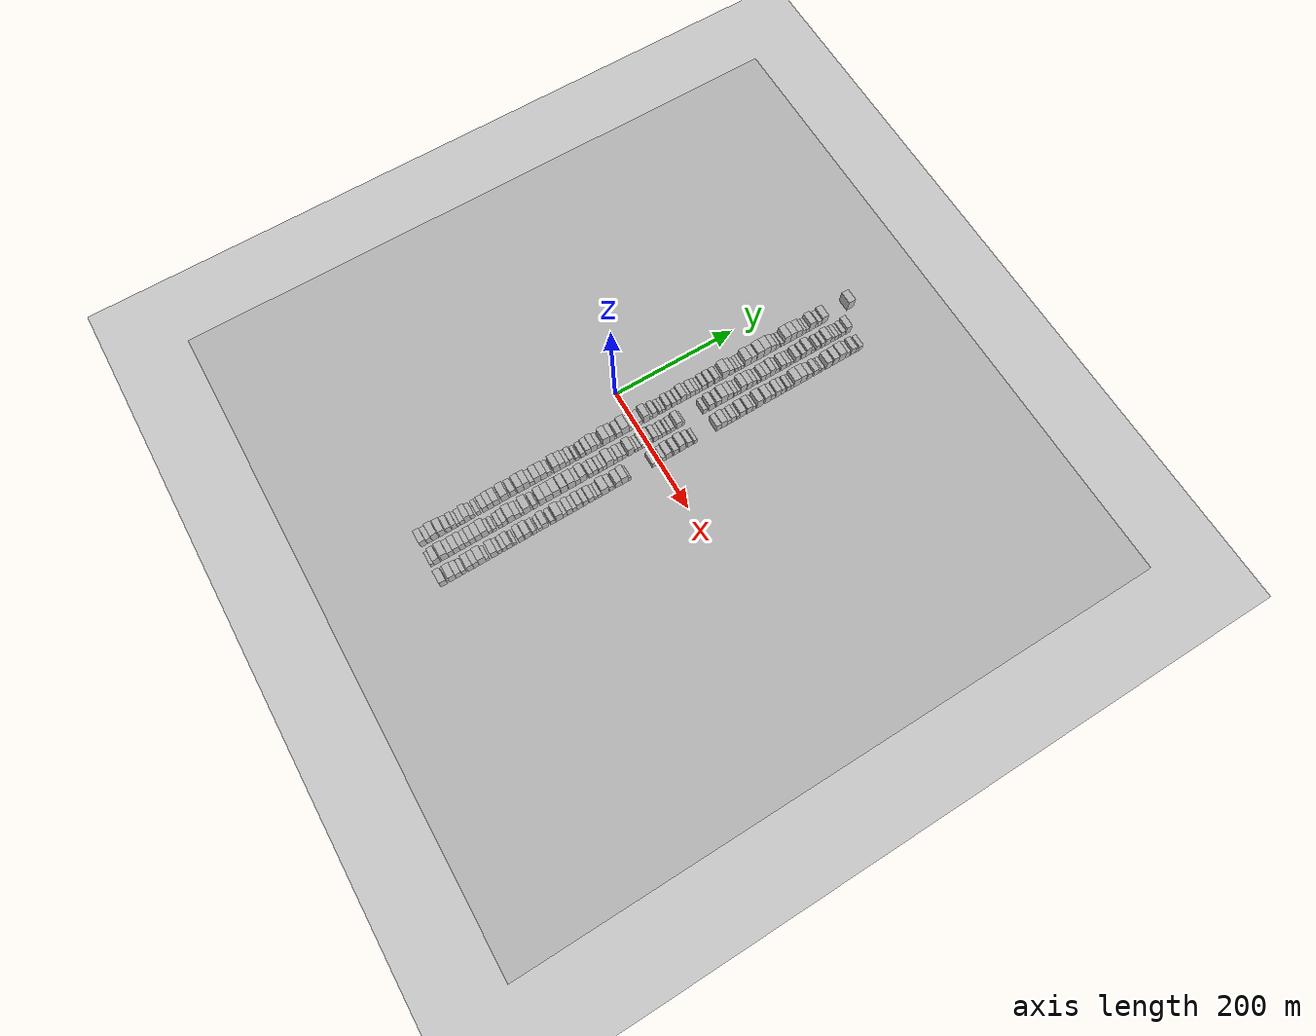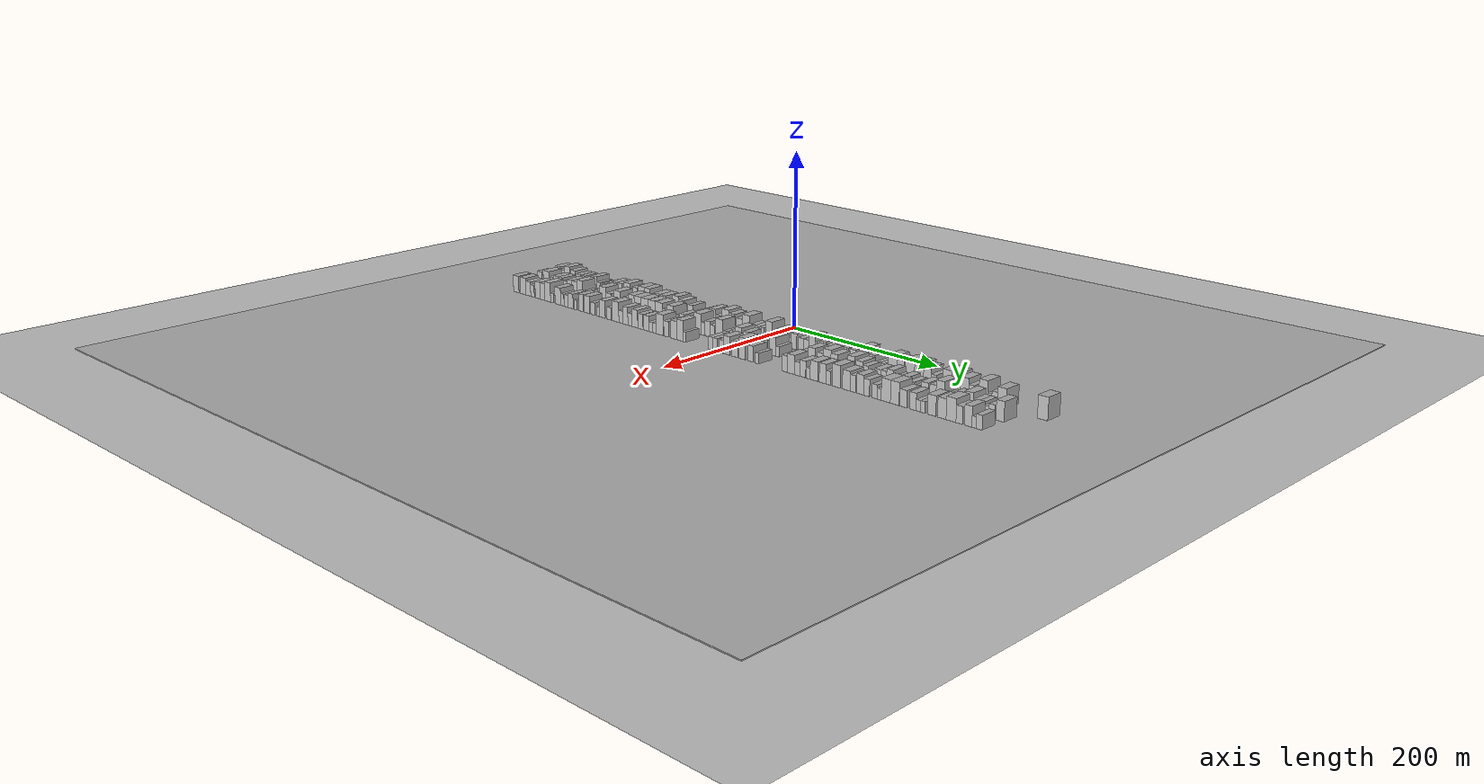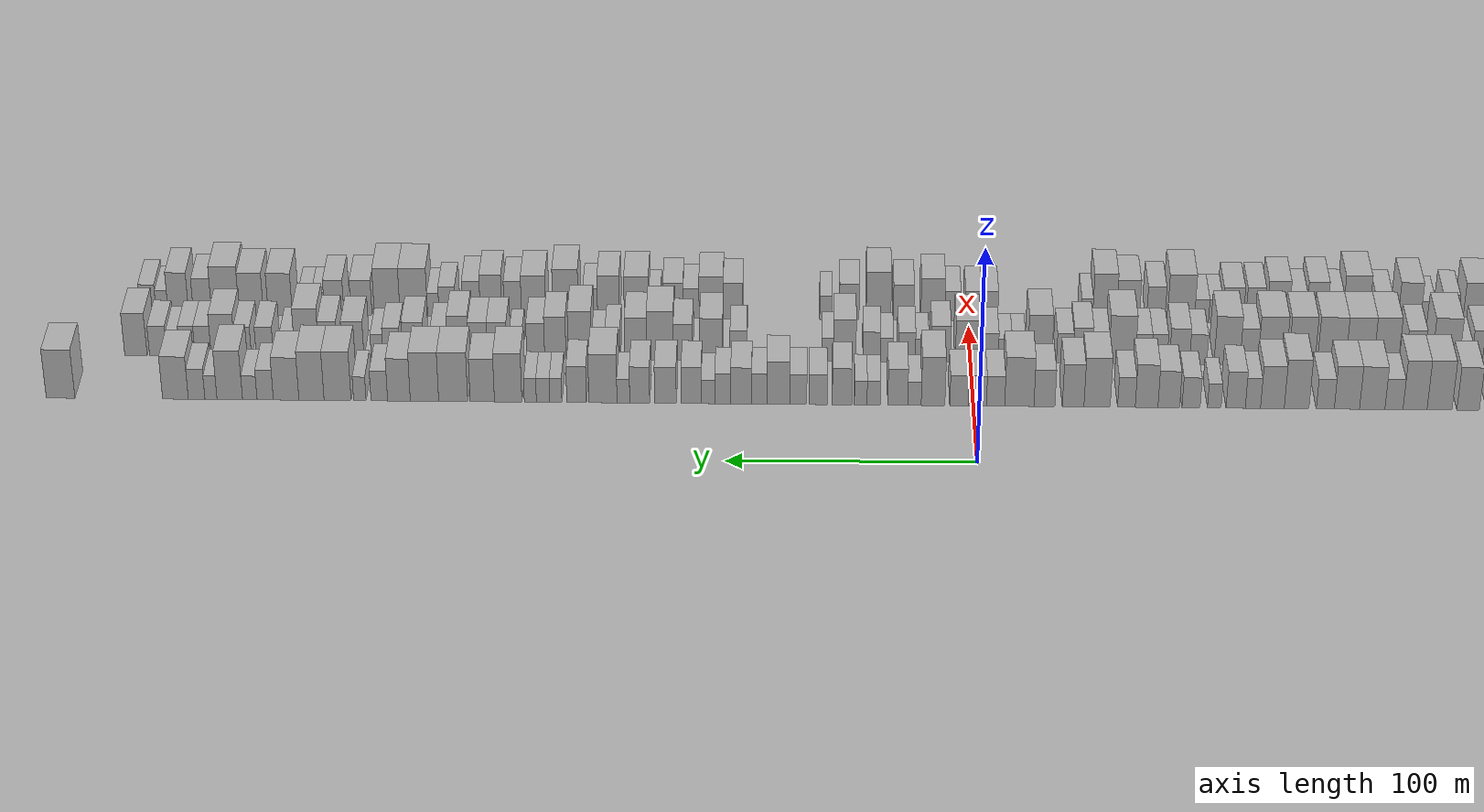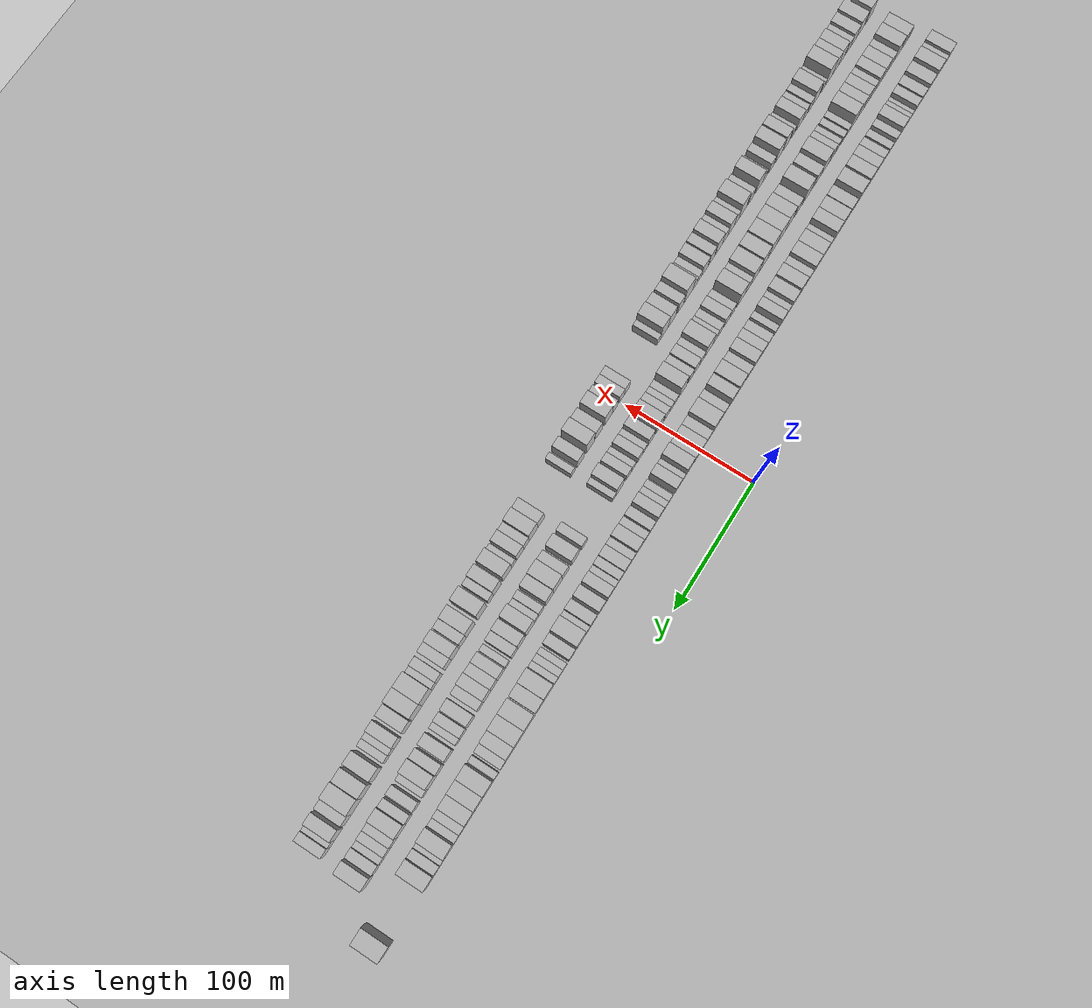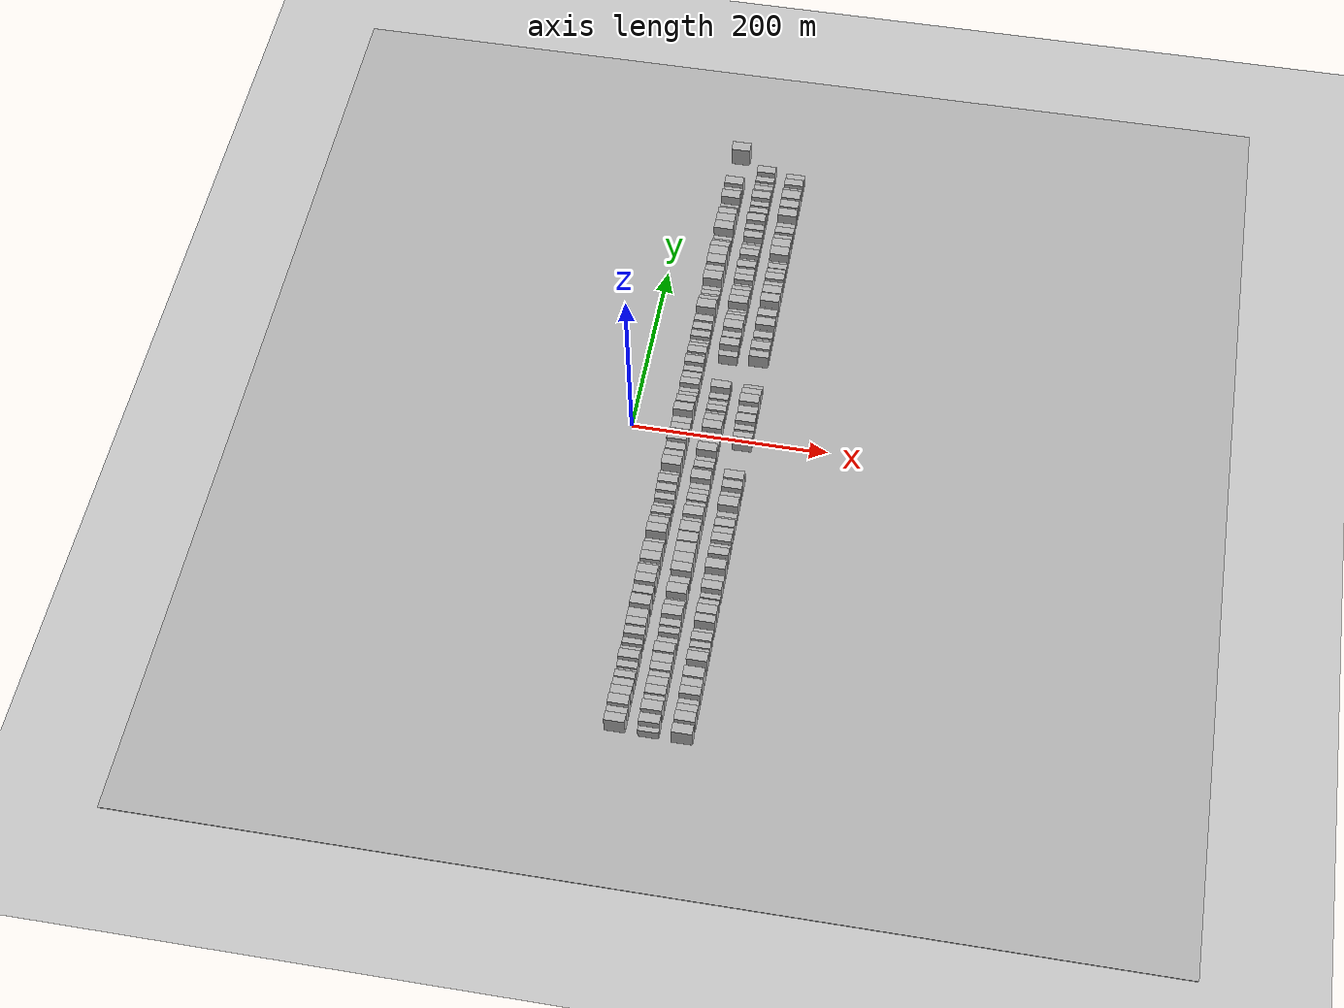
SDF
<?xml version="1.0" encoding="utf-8"?>

<sdf version="1.6">

   <world name="default">

      <gui fullscreen="0">

         <camera name="user_camera">

            <pose>-15 0 4.57585 0 0 0</pose>

            <view_controller>orbit</view_controller>

         </camera>

      </gui>

      <scene>

         <sky>

           <clouds>

             <speed>12</speed>

           </clouds>

         </sky>

         <ambient>0.4 0.4 0.4 1</ambient>

         <background>0.7 0.7 0.7 1</background>

         <shadows>1</shadows>

      </scene>

      <gravity>0 0 -9.8066</gravity>

      <magnetic_field>6e-06 2.3e-05 -4.2e-05</magnetic_field>

      <physics default="0" name="default_physics" type="ode">

         <ode>

            <solver>

               <type>quick</type>

               <iters>10</iters>

               <sor>1.0</sor>

               <use_dynamic_moi_rescaling>0</use_dynamic_moi_rescaling>

            </solver>

            <constraints>

               <cfm>0</cfm>

               <erp>0.2</erp>

               <contact_max_correcting_vel>100</contact_max_correcting_vel>

               <contact_surface_layer>0.001</contact_surface_layer>

            </constraints>

         </ode>

         <max_step_size>0.004</max_step_size>

         <real_time_factor>1</real_time_factor>

         <real_time_update_rate>250</real_time_update_rate>

      </physics>

      <light name="sun" type="directional">

         <cast_shadows>1</cast_shadows>

         <pose>0 0 10 0 0 0</pose>

         <diffuse>0.8 0.8 0.8 1</diffuse>

         <specular>0.2 0.2 0.2 1</specular>

         <attenuation>

            <range>1000</range>

            <constant>0.9</constant>

            <linear>0.01</linear>

            <quadratic>0.001</quadratic>

         </attenuation>

         <direction>-0.5 0.1 -0.9</direction>

      </light>

      <include>

         <name>ground_plane_1</name>

         <uri>model://HANNAS_ground_plane</uri>

         <pose>0 0 0  0 0 0</pose>

      </include>

      <include>

         <name>ground_plane_2</name>

         <uri>model://HANNAS_ground_plane</uri>

         <pose>100 0 0  0 0 0</pose>

      </include>

      <model name="building_1">

         <static>1</static>

         <pose frame="">50.0000 -340.2826 0 0.000000 0.000000 0.000000</pose>

         <link name="link">

            <pose frame="">0 0 10.50 0 0 0</pose>

            <collision name="collision">

               <geometry>

                  <box>

                     <size>20.0000 9.4347 21.0000</size>

                  </box>

               </geometry>

               <max_contacts>10</max_contacts>

               <surface>

                  <contact>

                     <ode/>

                  </contact>

                  <bounce/>

                  <friction>

                     <torsional>

                        <ode/>

                     </torsional>

                     <ode/>

                  </friction>

               </surface>

            </collision>

            <visual name="visual">

               <cast_shadows>0</cast_shadows>

               <geometry>

                  <box>

                     <size>20.0000 9.4347 21.0000</size>

                  </box>

               </geometry>

               <material>

                  <script>

                     <uri>model://HANNAS_wall/materials/scripts</uri>

                     <uri>model://HANNAS_wall/materials/textures</uri>

                     <name>vrc/HANNAS_wall</name>

                  </script>

               </material>

            </visual>

            <self_collide>0</self_collide>

            <enable_wind>0</enable_wind>

            <kinematic>0</kinematic>

         </link>

      </model>

      <model name="building_2">

         <static>1</static>

         <pose frame="">50.0000 -331.6003 0 0.000000 0.000000 0.000000</pose>

         <link name="link">

            <pose frame="">0 0 9.00 0 0 0</pose>

            <collision name="collision">

               <geometry>

                  <box>

                     <size>20.0000 7.9299 18.0000</size>

                  </box>

               </geometry>

               <max_contacts>10</max_contacts>

               <surface>

                  <contact>

                     <ode/>

                  </contact>

                  <bounce/>

                  <friction>

                     <torsional>

                        <ode/>

                     </torsional>

                     <ode/>

                  </friction>

               </surface>

            </collision>

            <visual name="visual">

               <cast_shadows>0</cast_shadows>

               <geometry>

                  <box>

                     <size>20.0000 7.9299 18.0000</size>

                  </box>

               </geometry>

               <material>

                  <script>

                     <uri>model://HANNAS_wall/materials/scripts</uri>

                     <uri>model://HANNAS_wall/materials/textures</uri>

                     <name>vrc/HANNAS_wall</name>

                  </script>

               </material>

            </visual>

            <self_collide>0</self_collide>

            <enable_wind>0</enable_wind>

            <kinematic>0</kinematic>

         </link>

      </model>

      <model name="building_3">

         <static>1</static>

         <pose frame="">50.0000 -322.5247 0 0.000000 0.000000 0.000000</pose>

         <link name="link">

            <pose frame="">0 0 12.00 0 0 0</pose>

            <collision name="collision">

               <geometry>

                  <box>

                     <size>20.0000 10.2214 24.0000</size>

                  </box>

               </geometry>

               <max_contacts>10</max_contacts>

               <surface>

                  <contact>

                     <ode/>

                  </contact>

                  <bounce/>

                  <friction>

                     <torsional>

                        <ode/>

                     </torsional>

                     <ode/>

                  </friction>

               </surface>

            </collision>

            <visual name="visual">

               <cast_shadows>0</cast_shadows>

               <geometry>

                  <box>

                     <size>20.0000 10.2214 24.0000</size>

                  </box>

               </geometry>

               <material>

                  <script>

                     <uri>model://HANNAS_wall/materials/scripts</uri>

                     <uri>model://HANNAS_wall/materials/textures</uri>

                     <name>vrc/HANNAS_wall</name>

                  </script>

               </material>

            </visual>

            <self_collide>0</self_collide>

            <enable_wind>0</enable_wind>

            <kinematic>0</kinematic>

         </link>

      </model>

      <model name="building_4">

         <static>1</static>

         <pose frame="">50.0000 -311.4862 0 0.000000 0.000000 0.000000</pose>

         <link name="link">

            <pose frame="">0 0 10.50 0 0 0</pose>

            <collision name="collision">

               <geometry>

                  <box>

                     <size>20.0000 9.8555 21.0000</size>

                  </box>

               </geometry>

               <max_contacts>10</max_contacts>

               <surface>

                  <contact>

                     <ode/>

                  </contact>

                  <bounce/>

                  <friction>

                     <torsional>

                        <ode/>

                     </torsional>

                     <ode/>

                  </friction>

               </surface>

            </collision>

            <visual name="visual">

               <cast_shadows>0</cast_shadows>

               <geometry>

                  <box>

                     <size>20.0000 9.8555 21.0000</size>

                  </box>

               </geometry>

               <material>

                  <script>

                     <uri>model://HANNAS_wall/materials/scripts</uri>

                     <uri>model://HANNAS_wall/materials/textures</uri>

                     <name>vrc/HANNAS_wall</name>

                  </script>

               </material>

            </visual>

            <self_collide>0</self_collide>

            <enable_wind>0</enable_wind>

            <kinematic>0</kinematic>

         </link>

      </model>

      <model name="building_5">

         <static>1</static>

         <pose frame="">50.0000 -301.4223 0 0.000000 0.000000 0.000000</pose>

         <link name="link">

            <pose frame="">0 0 9.00 0 0 0</pose>

            <collision name="collision">

               <geometry>

                  <box>

                     <size>20.0000 8.2723 18.0000</size>

                  </box>

               </geometry>

               <max_contacts>10</max_contacts>

               <surface>

                  <contact>

                     <ode/>

                  </contact>

                  <bounce/>

                  <friction>

                     <torsional>

                        <ode/>

                     </torsional>

                     <ode/>

                  </friction>

               </surface>

            </collision>

            <visual name="visual">

               <cast_shadows>0</cast_shadows>

               <geometry>

                  <box>

                     <size>20.0000 8.2723 18.0000</size>

                  </box>

               </geometry>

               <material>

                  <script>

                     <uri>model://HANNAS_wall/materials/scripts</uri>

                     <uri>model://HANNAS_wall/materials/textures</uri>

                     <name>vrc/HANNAS_wall</name>

                  </script>

               </material>

            </visual>

            <self_collide>0</self_collide>

            <enable_wind>0</enable_wind>

            <kinematic>0</kinematic>

         </link>

      </model>

      <model name="building_6">

         <static>1</static>

         <pose frame="">50.0000 -292.6091 0 0.000000 0.000000 0.000000</pose>

         <link name="link">

            <pose frame="">0 0 9.00 0 0 0</pose>

            <collision name="collision">

               <geometry>

                  <box>

                     <size>20.0000 7.3540 18.0000</size>

                  </box>

               </geometry>

               <max_contacts>10</max_contacts>

               <surface>

                  <contact>

                     <ode/>

                  </contact>

                  <bounce/>

                  <friction>

                     <torsional>

                        <ode/>

                     </torsional>

                     <ode/>

                  </friction>

               </surface>

            </collision>

            <visual name="visual">

               <cast_shadows>0</cast_shadows>

               <geometry>

                  <box>

                     <size>20.0000 7.3540 18.0000</size>

                  </box>

               </geometry>

               <material>

                  <script>

                     <uri>model://HANNAS_wall/materials/scripts</uri>

                     <uri>model://HANNAS_wall/materials/textures</uri>

                     <name>vrc/HANNAS_wall</name>

                  </script>

               </material>

            </visual>

            <self_collide>0</self_collide>

            <enable_wind>0</enable_wind>

            <kinematic>0</kinematic>

         </link>

      </model>

      <model name="building_7">

         <static>1</static>

         <pose frame="">50.0000 -286.3886 0 0.000000 0.000000 0.000000</pose>

         <link name="link">

            <pose frame="">0 0 6.00 0 0 0</pose>

            <collision name="collision">

               <geometry>

                  <box>

                     <size>20.0000 5.0870 12.0000</size>

                  </box>

               </geometry>

               <max_contacts>10</max_contacts>

               <surface>

                  <contact>

                     <ode/>

                  </contact>

                  <bounce/>

                  <friction>

                     <torsional>

                        <ode/>

                     </torsional>

                     <ode/>

                  </friction>

               </surface>

            </collision>

            <visual name="visual">

               <cast_shadows>0</cast_shadows>

               <geometry>

                  <box>

                     <size>20.0000 5.0870 12.0000</size>

                  </box>

               </geometry>

               <material>

                  <script>

                     <uri>model://HANNAS_wall/materials/scripts</uri>

                     <uri>model://HANNAS_wall/materials/textures</uri>

                     <name>vrc/HANNAS_wall</name>

                  </script>

               </material>

            </visual>

            <self_collide>0</self_collide>

            <enable_wind>0</enable_wind>

            <kinematic>0</kinematic>

         </link>

      </model>

      <model name="building_8">

         <static>1</static>

         <pose frame="">50.0000 -280.1901 0 0.000000 0.000000 0.000000</pose>

         <link name="link">

            <pose frame="">0 0 7.50 0 0 0</pose>

            <collision name="collision">

               <geometry>

                  <box>

                     <size>20.0000 7.3101 15.0000</size>

                  </box>

               </geometry>

               <max_contacts>10</max_contacts>

               <surface>

                  <contact>

                     <ode/>

                  </contact>

                  <bounce/>

                  <friction>

                     <torsional>

                        <ode/>

                     </torsional>

                     <ode/>

                  </friction>

               </surface>

            </collision>

            <visual name="visual">

               <cast_shadows>0</cast_shadows>

               <geometry>

                  <box>

                     <size>20.0000 7.3101 15.0000</size>

                  </box>

               </geometry>

               <material>

                  <script>

                     <uri>model://HANNAS_wall/materials/scripts</uri>

                     <uri>model://HANNAS_wall/materials/textures</uri>

                     <name>vrc/HANNAS_wall</name>

                  </script>

               </material>

            </visual>

            <self_collide>0</self_collide>

            <enable_wind>0</enable_wind>

            <kinematic>0</kinematic>

         </link>

      </model>

      <model name="building_9">

         <static>1</static>

         <pose frame="">50.0000 -272.0151 0 0.000000 0.000000 0.000000</pose>

         <link name="link">

            <pose frame="">0 0 10.50 0 0 0</pose>

            <collision name="collision">

               <geometry>

                  <box>

                     <size>20.0000 9.0398 21.0000</size>

                  </box>

               </geometry>

               <max_contacts>10</max_contacts>

               <surface>

                  <contact>

                     <ode/>

                  </contact>

                  <bounce/>

                  <friction>

                     <torsional>

                        <ode/>

                     </torsional>

                     <ode/>

                  </friction>

               </surface>

            </collision>

            <visual name="visual">

               <cast_shadows>0</cast_shadows>

               <geometry>

                  <box>

                     <size>20.0000 9.0398 21.0000</size>

                  </box>

               </geometry>

               <material>

                  <script>

                     <uri>model://HANNAS_wall/materials/scripts</uri>

                     <uri>model://HANNAS_wall/materials/textures</uri>

                     <name>vrc/HANNAS_wall</name>

                  </script>

               </material>

            </visual>

            <self_collide>0</self_collide>

            <enable_wind>0</enable_wind>

            <kinematic>0</kinematic>

         </link>

      </model>

      <model name="building_10">

         <static>1</static>

         <pose frame="">50.0000 -264.2155 0 0.000000 0.000000 0.000000</pose>

         <link name="link">

            <pose frame="">0 0 7.50 0 0 0</pose>

            <collision name="collision">

               <geometry>

                  <box>

                     <size>20.0000 6.5595 15.0000</size>

                  </box>

               </geometry>

               <max_contacts>10</max_contacts>

               <surface>

                  <contact>

                     <ode/>

                  </contact>

                  <bounce/>

                  <friction>

                     <torsional>

                        <ode/>

                     </torsional>

                     <ode/>

                  </friction>

               </surface>

            </collision>

            <visual name="visual">

               <cast_shadows>0</cast_shadows>

               <geometry>

                  <box>

                     <size>20.0000 6.5595 15.0000</size>

                  </box>

               </geometry>

               <material>

                  <script>

                     <uri>model://HANNAS_wall/materials/scripts</uri>

                     <uri>model://HANNAS_wall/materials/textures</uri>

                     <name>vrc/HANNAS_wall</name>

                  </script>

               </material>

            </visual>

            <self_collide>0</self_collide>

            <enable_wind>0</enable_wind>

            <kinematic>0</kinematic>

         </link>

      </model>

      <model name="building_11">

         <static>1</static>

         <pose frame="">50.0000 -254.8684 0 0.000000 0.000000 0.000000</pose>

         <link name="link">

            <pose frame="">0 0 7.50 0 0 0</pose>

            <collision name="collision">

               <geometry>

                  <box>

                     <size>20.0000 6.1347 15.0000</size>

                  </box>

               </geometry>

               <max_contacts>10</max_contacts>

               <surface>

                  <contact>

                     <ode/>

                  </contact>

                  <bounce/>

                  <friction>

                     <torsional>

                        <ode/>

                     </torsional>

                     <ode/>

                  </friction>

               </surface>

            </collision>

            <visual name="visual">

               <cast_shadows>0</cast_shadows>

               <geometry>

                  <box>

                     <size>20.0000 6.1347 15.0000</size>

                  </box>

               </geometry>

               <material>

                  <script>

                     <uri>model://HANNAS_wall/materials/scripts</uri>

                     <uri>model://HANNAS_wall/materials/textures</uri>

                     <name>vrc/HANNAS_wall</name>

                  </script>

               </material>

            </visual>

            <self_collide>0</self_collide>

            <enable_wind>0</enable_wind>

            <kinematic>0</kinematic>

         </link>

      </model>

      <model name="building_12">

         <static>1</static>

         <pose frame="">50.0000 -244.4860 0 0.000000 0.000000 0.000000</pose>

         <link name="link">

            <pose frame="">0 0 9.00 0 0 0</pose>

            <collision name="collision">

               <geometry>

                  <box>

                     <size>20.0000 8.6300 18.0000</size>

                  </box>

               </geometry>

               <max_contacts>10</max_contacts>

               <surface>

                  <contact>

                     <ode/>

                  </contact>

                  <bounce/>

                  <friction>

                     <torsional>

                        <ode/>

                     </torsional>

                     <ode/>

                  </friction>

               </surface>

            </collision>

            <visual name="visual">

               <cast_shadows>0</cast_shadows>

               <geometry>

                  <box>

                     <size>20.0000 8.6300 18.0000</size>

                  </box>

               </geometry>

               <material>

                  <script>

                     <uri>model://HANNAS_wall/materials/scripts</uri>

                     <uri>model://HANNAS_wall/materials/textures</uri>

                     <name>vrc/HANNAS_wall</name>

                  </script>

               </material>

            </visual>

            <self_collide>0</self_collide>

            <enable_wind>0</enable_wind>

            <kinematic>0</kinematic>

         </link>

      </model>

      <model name="building_13">

         <static>1</static>

         <pose frame="">50.0000 -235.8515 0 0.000000 0.000000 0.000000</pose>

         <link name="link">

            <pose frame="">0 0 10.50 0 0 0</pose>

            <collision name="collision">

               <geometry>

                  <box>

                     <size>20.0000 8.6390 21.0000</size>

                  </box>

               </geometry>

               <max_contacts>10</max_contacts>

               <surface>

                  <contact>

                     <ode/>

                  </contact>

                  <bounce/>

                  <friction>

                     <torsional>

                        <ode/>

                     </torsional>

                     <ode/>

                  </friction>

               </surface>

            </collision>

            <visual name="visual">

               <cast_shadows>0</cast_shadows>

               <geometry>

                  <box>

                     <size>20.0000 8.6390 21.0000</size>

                  </box>

               </geometry>

               <material>

                  <script>

                     <uri>model://HANNAS_wall/materials/scripts</uri>

                     <uri>model://HANNAS_wall/materials/textures</uri>

                     <name>vrc/HANNAS_wall</name>

                  </script>

               </material>

            </visual>

            <self_collide>0</self_collide>

            <enable_wind>0</enable_wind>

            <kinematic>0</kinematic>

         </link>

      </model>

      <model name="building_14">

         <static>1</static>

         <pose frame="">50.0000 -226.6366 0 0.000000 0.000000 0.000000</pose>

         <link name="link">

            <pose frame="">0 0 10.50 0 0 0</pose>

            <collision name="collision">

               <geometry>

                  <box>

                     <size>20.0000 9.7907 21.0000</size>

                  </box>

               </geometry>

               <max_contacts>10</max_contacts>

               <surface>

                  <contact>

                     <ode/>

                  </contact>

                  <bounce/>

                  <friction>

                     <torsional>

                        <ode/>

                     </torsional>

                     <ode/>

                  </friction>

               </surface>

            </collision>

            <visual name="visual">

               <cast_shadows>0</cast_shadows>

               <geometry>

                  <box>

                     <size>20.0000 9.7907 21.0000</size>

                  </box>

               </geometry>

               <material>

                  <script>

                     <uri>model://HANNAS_wall/materials/scripts</uri>

                     <uri>model://HANNAS_wall/materials/textures</uri>

                     <name>vrc/HANNAS_wall</name>

                  </script>

               </material>

            </visual>

            <self_collide>0</self_collide>

            <enable_wind>0</enable_wind>

            <kinematic>0</kinematic>

         </link>

      </model>

      <model name="building_15">

         <static>1</static>

         <pose frame="">50.0000 -213.1437 0 0.000000 0.000000 0.000000</pose>

         <link name="link">

            <pose frame="">0 0 12.00 0 0 0</pose>

            <collision name="collision">

               <geometry>

                  <box>

                     <size>20.0000 11.1949 24.0000</size>

                  </box>

               </geometry>

               <max_contacts>10</max_contacts>

               <surface>

                  <contact>

                     <ode/>

                  </contact>

                  <bounce/>

                  <friction>

                     <torsional>

                        <ode/>

                     </torsional>

                     <ode/>

                  </friction>

               </surface>

            </collision>

            <visual name="visual">

               <cast_shadows>0</cast_shadows>

               <geometry>

                  <box>

                     <size>20.0000 11.1949 24.0000</size>

                  </box>

               </geometry>

               <material>

                  <script>

                     <uri>model://HANNAS_wall/materials/scripts</uri>

                     <uri>model://HANNAS_wall/materials/textures</uri>

                     <name>vrc/HANNAS_wall</name>

                  </script>

               </material>

            </visual>

            <self_collide>0</self_collide>

            <enable_wind>0</enable_wind>

            <kinematic>0</kinematic>

         </link>

      </model>

      <model name="building_16">

         <static>1</static>

         <pose frame="">50.0000 -200.0086 0 0.000000 0.000000 0.000000</pose>

         <link name="link">

            <pose frame="">0 0 10.50 0 0 0</pose>

            <collision name="collision">

               <geometry>

                  <box>

                     <size>20.0000 9.0752 21.0000</size>

                  </box>

               </geometry>

               <max_contacts>10</max_contacts>

               <surface>

                  <contact>

                     <ode/>

                  </contact>

                  <bounce/>

                  <friction>

                     <torsional>

                        <ode/>

                     </torsional>

                     <ode/>

                  </friction>

               </surface>

            </collision>

            <visual name="visual">

               <cast_shadows>0</cast_shadows>

               <geometry>

                  <box>

                     <size>20.0000 9.0752 21.0000</size>

                  </box>

               </geometry>

               <material>

                  <script>

                     <uri>model://HANNAS_wall/materials/scripts</uri>

                     <uri>model://HANNAS_wall/materials/textures</uri>

                     <name>vrc/HANNAS_wall</name>

                  </script>

               </material>

            </visual>

            <self_collide>0</self_collide>

            <enable_wind>0</enable_wind>

            <kinematic>0</kinematic>

         </link>

      </model>

      <model name="building_17">

         <static>1</static>

         <pose frame="">50.0000 -188.4318 0 0.000000 0.000000 0.000000</pose>

         <link name="link">

            <pose frame="">0 0 12.00 0 0 0</pose>

            <collision name="collision">

               <geometry>

                  <box>

                     <size>20.0000 10.0784 24.0000</size>

                  </box>

               </geometry>

               <max_contacts>10</max_contacts>

               <surface>

                  <contact>

                     <ode/>

                  </contact>

                  <bounce/>

                  <friction>

                     <torsional>

                        <ode/>

                     </torsional>

                     <ode/>

                  </friction>

               </surface>

            </collision>

            <visual name="visual">

               <cast_shadows>0</cast_shadows>

               <geometry>

                  <box>

                     <size>20.0000 10.0784 24.0000</size>

                  </box>

               </geometry>

               <material>

                  <script>

                     <uri>model://HANNAS_wall/materials/scripts</uri>

                     <uri>model://HANNAS_wall/materials/textures</uri>

                     <name>vrc/HANNAS_wall</name>

                  </script>

               </material>

            </visual>

            <self_collide>0</self_collide>

            <enable_wind>0</enable_wind>

            <kinematic>0</kinematic>

         </link>

      </model>

      <model name="building_18">

         <static>1</static>

         <pose frame="">50.0000 -178.5305 0 0.000000 0.000000 0.000000</pose>

         <link name="link">

            <pose frame="">0 0 12.00 0 0 0</pose>

            <collision name="collision">

               <geometry>

                  <box>

                     <size>20.0000 9.7241 24.0000</size>

                  </box>

               </geometry>

               <max_contacts>10</max_contacts>

               <surface>

                  <contact>

                     <ode/>

                  </contact>

                  <bounce/>

                  <friction>

                     <torsional>

                        <ode/>

                     </torsional>

                     <ode/>

                  </friction>

               </surface>

            </collision>

            <visual name="visual">

               <cast_shadows>0</cast_shadows>

               <geometry>

                  <box>

                     <size>20.0000 9.7241 24.0000</size>

                  </box>

               </geometry>

               <material>

                  <script>

                     <uri>model://HANNAS_wall/materials/scripts</uri>

                     <uri>model://HANNAS_wall/materials/textures</uri>

                     <name>vrc/HANNAS_wall</name>

                  </script>

               </material>

            </visual>

            <self_collide>0</self_collide>

            <enable_wind>0</enable_wind>

            <kinematic>0</kinematic>

         </link>

      </model>

      <model name="building_19">

         <static>1</static>

         <pose frame="">50.0000 -170.0126 0 0.000000 0.000000 0.000000</pose>

         <link name="link">

            <pose frame="">0 0 7.50 0 0 0</pose>

            <collision name="collision">

               <geometry>

                  <box>

                     <size>20.0000 7.3117 15.0000</size>

                  </box>

               </geometry>

               <max_contacts>10</max_contacts>

               <surface>

                  <contact>

                     <ode/>

                  </contact>

                  <bounce/>

                  <friction>

                     <torsional>

                        <ode/>

                     </torsional>

                     <ode/>

                  </friction>

               </surface>

            </collision>

            <visual name="visual">

               <cast_shadows>0</cast_shadows>

               <geometry>

                  <box>

                     <size>20.0000 7.3117 15.0000</size>

                  </box>

               </geometry>

               <material>

                  <script>

                     <uri>model://HANNAS_wall/materials/scripts</uri>

                     <uri>model://HANNAS_wall/materials/textures</uri>

                     <name>vrc/HANNAS_wall</name>

                  </script>

               </material>

            </visual>

            <self_collide>0</self_collide>

            <enable_wind>0</enable_wind>

            <kinematic>0</kinematic>

         </link>

      </model>

      <model name="building_20">

         <static>1</static>

         <pose frame="">50.0000 -161.2173 0 0.000000 0.000000 0.000000</pose>

         <link name="link">

            <pose frame="">0 0 10.50 0 0 0</pose>

            <collision name="collision">

               <geometry>

                  <box>

                     <size>20.0000 10.2788 21.0000</size>

                  </box>

               </geometry>

               <max_contacts>10</max_contacts>

               <surface>

                  <contact>

                     <ode/>

                  </contact>

                  <bounce/>

                  <friction>

                     <torsional>

                        <ode/>

                     </torsional>

                     <ode/>

                  </friction>

               </surface>

            </collision>

            <visual name="visual">

               <cast_shadows>0</cast_shadows>

               <geometry>

                  <box>

                     <size>20.0000 10.2788 21.0000</size>

                  </box>

               </geometry>

               <material>

                  <script>

                     <uri>model://HANNAS_wall/materials/scripts</uri>

                     <uri>model://HANNAS_wall/materials/textures</uri>

                     <name>vrc/HANNAS_wall</name>

                  </script>

               </material>

            </visual>

            <self_collide>0</self_collide>

            <enable_wind>0</enable_wind>

            <kinematic>0</kinematic>

         </link>

      </model>

      <model name="building_21">

         <static>1</static>

         <pose frame="">50.0000 -150.9721 0 0.000000 0.000000 0.000000</pose>

         <link name="link">

            <pose frame="">0 0 10.50 0 0 0</pose>

            <collision name="collision">

               <geometry>

                  <box>

                     <size>20.0000 10.2117 21.0000</size>

                  </box>

               </geometry>

               <max_contacts>10</max_contacts>

               <surface>

                  <contact>

                     <ode/>

                  </contact>

                  <bounce/>

                  <friction>

                     <torsional>

                        <ode/>

                     </torsional>

                     <ode/>

                  </friction>

               </surface>

            </collision>

            <visual name="visual">

               <cast_shadows>0</cast_shadows>

               <geometry>

                  <box>

                     <size>20.0000 10.2117 21.0000</size>

                  </box>

               </geometry>

               <material>

                  <script>

                     <uri>model://HANNAS_wall/materials/scripts</uri>

                     <uri>model://HANNAS_wall/materials/textures</uri>

                     <name>vrc/HANNAS_wall</name>

                  </script>

               </material>

            </visual>

            <self_collide>0</self_collide>

            <enable_wind>0</enable_wind>

            <kinematic>0</kinematic>

         </link>

      </model>

      <model name="building_22">

         <static>1</static>

         <pose frame="">50.0000 -142.2356 0 0.000000 0.000000 0.000000</pose>

         <link name="link">

            <pose frame="">0 0 7.50 0 0 0</pose>

            <collision name="collision">

               <geometry>

                  <box>

                     <size>20.0000 7.2612 15.0000</size>

                  </box>

               </geometry>

               <max_contacts>10</max_contacts>

               <surface>

                  <contact>

                     <ode/>

                  </contact>

                  <bounce/>

                  <friction>

                     <torsional>

                        <ode/>

                     </torsional>

                     <ode/>

                  </friction>

               </surface>

            </collision>

            <visual name="visual">

               <cast_shadows>0</cast_shadows>

               <geometry>

                  <box>

                     <size>20.0000 7.2612 15.0000</size>

                  </box>

               </geometry>

               <material>

                  <script>

                     <uri>model://HANNAS_wall/materials/scripts</uri>

                     <uri>model://HANNAS_wall/materials/textures</uri>

                     <name>vrc/HANNAS_wall</name>

                  </script>

               </material>

            </visual>

            <self_collide>0</self_collide>

            <enable_wind>0</enable_wind>

            <kinematic>0</kinematic>

         </link>

      </model>

      <model name="building_23">

         <static>1</static>

         <pose frame="">50.0000 -130.6100 0 0.000000 0.000000 0.000000</pose>

         <link name="link">

            <pose frame="">0 0 12.00 0 0 0</pose>

            <collision name="collision">

               <geometry>

                  <box>

                     <size>20.0000 9.9899 24.0000</size>

                  </box>

               </geometry>

               <max_contacts>10</max_contacts>

               <surface>

                  <contact>

                     <ode/>

                  </contact>

                  <bounce/>

                  <friction>

                     <torsional>

                        <ode/>

                     </torsional>

                     <ode/>

                  </friction>

               </surface>

            </collision>

            <visual name="visual">

               <cast_shadows>0</cast_shadows>

               <geometry>

                  <box>

                     <size>20.0000 9.9899 24.0000</size>

                  </box>

               </geometry>

               <material>

                  <script>

                     <uri>model://HANNAS_wall/materials/scripts</uri>

                     <uri>model://HANNAS_wall/materials/textures</uri>

                     <name>vrc/HANNAS_wall</name>

                  </script>

               </material>

            </visual>

            <self_collide>0</self_collide>

            <enable_wind>0</enable_wind>

            <kinematic>0</kinematic>

         </link>

      </model>

      <model name="building_24">

         <static>1</static>

         <pose frame="">50.0000 -120.8215 0 0.000000 0.000000 0.000000</pose>

         <link name="link">

            <pose frame="">0 0 10.50 0 0 0</pose>

            <collision name="collision">

               <geometry>

                  <box>

                     <size>20.0000 9.5870 21.0000</size>

                  </box>

               </geometry>

               <max_contacts>10</max_contacts>

               <surface>

                  <contact>

                     <ode/>

                  </contact>

                  <bounce/>

                  <friction>

                     <torsional>

                        <ode/>

                     </torsional>

                     <ode/>

                  </friction>

               </surface>

            </collision>

            <visual name="visual">

               <cast_shadows>0</cast_shadows>

               <geometry>

                  <box>

                     <size>20.0000 9.5870 21.0000</size>

                  </box>

               </geometry>

               <material>

                  <script>

                     <uri>model://HANNAS_wall/materials/scripts</uri>

                     <uri>model://HANNAS_wall/materials/textures</uri>

                     <name>vrc/HANNAS_wall</name>

                  </script>

               </material>

            </visual>

            <self_collide>0</self_collide>

            <enable_wind>0</enable_wind>

            <kinematic>0</kinematic>

         </link>

      </model>

      <model name="building_25">

         <static>1</static>

         <pose frame="">50.0000 -112.9445 0 0.000000 0.000000 0.000000</pose>

         <link name="link">

            <pose frame="">0 0 7.50 0 0 0</pose>

            <collision name="collision">

               <geometry>

                  <box>

                     <size>20.0000 6.1671 15.0000</size>

                  </box>

               </geometry>

               <max_contacts>10</max_contacts>

               <surface>

                  <contact>

                     <ode/>

                  </contact>

                  <bounce/>

                  <friction>

                     <torsional>

                        <ode/>

                     </torsional>

                     <ode/>

                  </friction>

               </surface>

            </collision>

            <visual name="visual">

               <cast_shadows>0</cast_shadows>

               <geometry>

                  <box>

                     <size>20.0000 6.1671 15.0000</size>

                  </box>

               </geometry>

               <material>

                  <script>

                     <uri>model://HANNAS_wall/materials/scripts</uri>

                     <uri>model://HANNAS_wall/materials/textures</uri>

                     <name>vrc/HANNAS_wall</name>

                  </script>

               </material>

            </visual>

            <self_collide>0</self_collide>

            <enable_wind>0</enable_wind>

            <kinematic>0</kinematic>

         </link>

      </model>

      <model name="building_26">

         <static>1</static>

         <pose frame="">50.0000 -105.9658 0 0.000000 0.000000 0.000000</pose>

         <link name="link">

            <pose frame="">0 0 9.00 0 0 0</pose>

            <collision name="collision">

               <geometry>

                  <box>

                     <size>20.0000 7.7904 18.0000</size>

                  </box>

               </geometry>

               <max_contacts>10</max_contacts>

               <surface>

                  <contact>

                     <ode/>

                  </contact>

                  <bounce/>

                  <friction>

                     <torsional>

                        <ode/>

                     </torsional>

                     <ode/>

                  </friction>

               </surface>

            </collision>

            <visual name="visual">

               <cast_shadows>0</cast_shadows>

               <geometry>

                  <box>

                     <size>20.0000 7.7904 18.0000</size>

                  </box>

               </geometry>

               <material>

                  <script>

                     <uri>model://HANNAS_wall/materials/scripts</uri>

                     <uri>model://HANNAS_wall/materials/textures</uri>

                     <name>vrc/HANNAS_wall</name>

                  </script>

               </material>

            </visual>

            <self_collide>0</self_collide>

            <enable_wind>0</enable_wind>

            <kinematic>0</kinematic>

         </link>

      </model>

      <model name="building_27">

         <static>1</static>

         <pose frame="">50.0000 -97.3130 0 0.000000 0.000000 0.000000</pose>

         <link name="link">

            <pose frame="">0 0 6.00 0 0 0</pose>

            <collision name="collision">

               <geometry>

                  <box>

                     <size>20.0000 5.5154 12.0000</size>

                  </box>

               </geometry>

               <max_contacts>10</max_contacts>

               <surface>

                  <contact>

                     <ode/>

                  </contact>

                  <bounce/>

                  <friction>

                     <torsional>

                        <ode/>

                     </torsional>

                     <ode/>

                  </friction>

               </surface>

            </collision>

            <visual name="visual">

               <cast_shadows>0</cast_shadows>

               <geometry>

                  <box>

                     <size>20.0000 5.5154 12.0000</size>

                  </box>

               </geometry>

               <material>

                  <script>

                     <uri>model://HANNAS_wall/materials/scripts</uri>

                     <uri>model://HANNAS_wall/materials/textures</uri>

                     <name>vrc/HANNAS_wall</name>

                  </script>

               </material>

            </visual>

            <self_collide>0</self_collide>

            <enable_wind>0</enable_wind>

            <kinematic>0</kinematic>

         </link>

      </model>

      <model name="building_28">

         <static>1</static>

         <pose frame="">50.0000 -87.8930 0 0.000000 0.000000 0.000000</pose>

         <link name="link">

            <pose frame="">0 0 7.50 0 0 0</pose>

            <collision name="collision">

               <geometry>

                  <box>

                     <size>20.0000 7.3246 15.0000</size>

                  </box>

               </geometry>

               <max_contacts>10</max_contacts>

               <surface>

                  <contact>

                     <ode/>

                  </contact>

                  <bounce/>

                  <friction>

                     <torsional>

                        <ode/>

                     </torsional>

                     <ode/>

                  </friction>

               </surface>

            </collision>

            <visual name="visual">

               <cast_shadows>0</cast_shadows>

               <geometry>

                  <box>

                     <size>20.0000 7.3246 15.0000</size>

                  </box>

               </geometry>

               <material>

                  <script>

                     <uri>model://HANNAS_wall/materials/scripts</uri>

                     <uri>model://HANNAS_wall/materials/textures</uri>

                     <name>vrc/HANNAS_wall</name>

                  </script>

               </material>

            </visual>

            <self_collide>0</self_collide>

            <enable_wind>0</enable_wind>

            <kinematic>0</kinematic>

         </link>

      </model>

      <model name="building_29">

         <static>1</static>

         <pose frame="">50.0000 -78.8651 0 0.000000 0.000000 0.000000</pose>

         <link name="link">

            <pose frame="">0 0 9.00 0 0 0</pose>

            <collision name="collision">

               <geometry>

                  <box>

                     <size>20.0000 8.7313 18.0000</size>

                  </box>

               </geometry>

               <max_contacts>10</max_contacts>

               <surface>

                  <contact>

                     <ode/>

                  </contact>

                  <bounce/>

                  <friction>

                     <torsional>

                        <ode/>

                     </torsional>

                     <ode/>

                  </friction>

               </surface>

            </collision>

            <visual name="visual">

               <cast_shadows>0</cast_shadows>

               <geometry>

                  <box>

                     <size>20.0000 8.7313 18.0000</size>

                  </box>

               </geometry>

               <material>

                  <script>

                     <uri>model://HANNAS_wall/materials/scripts</uri>

                     <uri>model://HANNAS_wall/materials/textures</uri>

                     <name>vrc/HANNAS_wall</name>

                  </script>

               </material>

            </visual>

            <self_collide>0</self_collide>

            <enable_wind>0</enable_wind>

            <kinematic>0</kinematic>

         </link>

      </model>

      <model name="building_30">

         <static>1</static>

         <pose frame="">50.0000 -69.8941 0 0.000000 0.000000 0.000000</pose>

         <link name="link">

            <pose frame="">0 0 10.50 0 0 0</pose>

            <collision name="collision">

               <geometry>

                  <box>

                     <size>20.0000 9.2106 21.0000</size>

                  </box>

               </geometry>

               <max_contacts>10</max_contacts>

               <surface>

                  <contact>

                     <ode/>

                  </contact>

                  <bounce/>

                  <friction>

                     <torsional>

                        <ode/>

                     </torsional>

                     <ode/>

                  </friction>

               </surface>

            </collision>

            <visual name="visual">

               <cast_shadows>0</cast_shadows>

               <geometry>

                  <box>

                     <size>20.0000 9.2106 21.0000</size>

                  </box>

               </geometry>

               <material>

                  <script>

                     <uri>model://HANNAS_wall/materials/scripts</uri>

                     <uri>model://HANNAS_wall/materials/textures</uri>

                     <name>vrc/HANNAS_wall</name>

                  </script>

               </material>

            </visual>

            <self_collide>0</self_collide>

            <enable_wind>0</enable_wind>

            <kinematic>0</kinematic>

         </link>

      </model>

      <model name="building_31">

         <static>1</static>

         <pose frame="">50.0000 -61.7174 0 0.000000 0.000000 0.000000</pose>

         <link name="link">

            <pose frame="">0 0 7.50 0 0 0</pose>

            <collision name="collision">

               <geometry>

                  <box>

                     <size>20.0000 7.1428 15.0000</size>

                  </box>

               </geometry>

               <max_contacts>10</max_contacts>

               <surface>

                  <contact>

                     <ode/>

                  </contact>

                  <bounce/>

                  <friction>

                     <torsional>

                        <ode/>

                     </torsional>

                     <ode/>

                  </friction>

               </surface>

            </collision>

            <visual name="visual">

               <cast_shadows>0</cast_shadows>

               <geometry>

                  <box>

                     <size>20.0000 7.1428 15.0000</size>

                  </box>

               </geometry>

               <material>

                  <script>

                     <uri>model://HANNAS_wall/materials/scripts</uri>

                     <uri>model://HANNAS_wall/materials/textures</uri>

                     <name>vrc/HANNAS_wall</name>

                  </script>

               </material>

            </visual>

            <self_collide>0</self_collide>

            <enable_wind>0</enable_wind>

            <kinematic>0</kinematic>

         </link>

      </model>

      <model name="building_32">

         <static>1</static>

         <pose frame="">50.0000 -49.8279 0 0.000000 0.000000 0.000000</pose>

         <link name="link">

            <pose frame="">0 0 12.00 0 0 0</pose>

            <collision name="collision">

               <geometry>

                  <box>

                     <size>20.0000 10.6363 24.0000</size>

                  </box>

               </geometry>

               <max_contacts>10</max_contacts>

               <surface>

                  <contact>

                     <ode/>

                  </contact>

                  <bounce/>

                  <friction>

                     <torsional>

                        <ode/>

                     </torsional>

                     <ode/>

                  </friction>

               </surface>

            </collision>

            <visual name="visual">

               <cast_shadows>0</cast_shadows>

               <geometry>

                  <box>

                     <size>20.0000 10.6363 24.0000</size>

                  </box>

               </geometry>

               <material>

                  <script>

                     <uri>model://HANNAS_wall/materials/scripts</uri>

                     <uri>model://HANNAS_wall/materials/textures</uri>

                     <name>vrc/HANNAS_wall</name>

                  </script>

               </material>

            </visual>

            <self_collide>0</self_collide>

            <enable_wind>0</enable_wind>

            <kinematic>0</kinematic>

         </link>

      </model>

      <model name="building_33">

         <static>1</static>

         <pose frame="">50.0000 -40.1255 0 0.000000 0.000000 0.000000</pose>

         <link name="link">

            <pose frame="">0 0 10.50 0 0 0</pose>

            <collision name="collision">

               <geometry>

                  <box>

                     <size>20.0000 8.7684 21.0000</size>

                  </box>

               </geometry>

               <max_contacts>10</max_contacts>

               <surface>

                  <contact>

                     <ode/>

                  </contact>

                  <bounce/>

                  <friction>

                     <torsional>

                        <ode/>

                     </torsional>

                     <ode/>

                  </friction>

               </surface>

            </collision>

            <visual name="visual">

               <cast_shadows>0</cast_shadows>

               <geometry>

                  <box>

                     <size>20.0000 8.7684 21.0000</size>

                  </box>

               </geometry>

               <material>

                  <script>

                     <uri>model://HANNAS_wall/materials/scripts</uri>

                     <uri>model://HANNAS_wall/materials/textures</uri>

                     <name>vrc/HANNAS_wall</name>

                  </script>

               </material>

            </visual>

            <self_collide>0</self_collide>

            <enable_wind>0</enable_wind>

            <kinematic>0</kinematic>

         </link>

      </model>

      <model name="building_34">

         <static>1</static>

         <pose frame="">50.0000 -28.4858 0 0.000000 0.000000 0.000000</pose>

         <link name="link">

            <pose frame="">0 0 9.00 0 0 0</pose>

            <collision name="collision">

               <geometry>

                  <box>

                     <size>20.0000 8.5110 18.0000</size>

                  </box>

               </geometry>

               <max_contacts>10</max_contacts>

               <surface>

                  <contact>

                     <ode/>

                  </contact>

                  <bounce/>

                  <friction>

                     <torsional>

                        <ode/>

                     </torsional>

                     <ode/>

                  </friction>

               </surface>

            </collision>

            <visual name="visual">

               <cast_shadows>0</cast_shadows>

               <geometry>

                  <box>

                     <size>20.0000 8.5110 18.0000</size>

                  </box>

               </geometry>

               <material>

                  <script>

                     <uri>model://HANNAS_wall/materials/scripts</uri>

                     <uri>model://HANNAS_wall/materials/textures</uri>

                     <name>vrc/HANNAS_wall</name>

                  </script>

               </material>

            </visual>

            <self_collide>0</self_collide>

            <enable_wind>0</enable_wind>

            <kinematic>0</kinematic>

         </link>

      </model>

      <model name="building_35">

         <static>1</static>

         <pose frame="">50.0000 -18.3038 0 0.000000 0.000000 0.000000</pose>

         <link name="link">

            <pose frame="">0 0 12.00 0 0 0</pose>

            <collision name="collision">

               <geometry>

                  <box>

                     <size>20.0000 11.8528 24.0000</size>

                  </box>

               </geometry>

               <max_contacts>10</max_contacts>

               <surface>

                  <contact>

                     <ode/>

                  </contact>

                  <bounce/>

                  <friction>

                     <torsional>

                        <ode/>

                     </torsional>

                     <ode/>

                  </friction>

               </surface>

            </collision>

            <visual name="visual">

               <cast_shadows>0</cast_shadows>

               <geometry>

                  <box>

                     <size>20.0000 11.8528 24.0000</size>

                  </box>

               </geometry>

               <material>

                  <script>

                     <uri>model://HANNAS_wall/materials/scripts</uri>

                     <uri>model://HANNAS_wall/materials/textures</uri>

                     <name>vrc/HANNAS_wall</name>

                  </script>

               </material>

            </visual>

            <self_collide>0</self_collide>

            <enable_wind>0</enable_wind>

            <kinematic>0</kinematic>

         </link>

      </model>

      <model name="building_36">

         <static>1</static>

         <pose frame="">50.0000 -8.6696 0 0.000000 0.000000 0.000000</pose>

         <link name="link">

            <pose frame="">0 0 7.50 0 0 0</pose>

            <collision name="collision">

               <geometry>

                  <box>

                     <size>20.0000 7.4157 15.0000</size>

                  </box>

               </geometry>

               <max_contacts>10</max_contacts>

               <surface>

                  <contact>

                     <ode/>

                  </contact>

                  <bounce/>

                  <friction>

                     <torsional>

                        <ode/>

                     </torsional>

                     <ode/>

                  </friction>

               </surface>

            </collision>

            <visual name="visual">

               <cast_shadows>0</cast_shadows>

               <geometry>

                  <box>

                     <size>20.0000 7.4157 15.0000</size>

                  </box>

               </geometry>

               <material>

                  <script>

                     <uri>model://HANNAS_wall/materials/scripts</uri>

                     <uri>model://HANNAS_wall/materials/textures</uri>

                     <name>vrc/HANNAS_wall</name>

                  </script>

               </material>

            </visual>

            <self_collide>0</self_collide>

            <enable_wind>0</enable_wind>

            <kinematic>0</kinematic>

         </link>

      </model>

      <model name="building_37">

         <static>1</static>

         <pose frame="">50.0000 -1.2589 0 0.000000 0.000000 0.000000</pose>

         <link name="link">

            <pose frame="">0 0 7.50 0 0 0</pose>

            <collision name="collision">

               <geometry>

                  <box>

                     <size>20.0000 7.4055 15.0000</size>

                  </box>

               </geometry>

               <max_contacts>10</max_contacts>

               <surface>

                  <contact>

                     <ode/>

                  </contact>

                  <bounce/>

                  <friction>

                     <torsional>

                        <ode/>

                     </torsional>

                     <ode/>

                  </friction>

               </surface>

            </collision>

            <visual name="visual">

               <cast_shadows>0</cast_shadows>

               <geometry>

                  <box>

                     <size>20.0000 7.4055 15.0000</size>

                  </box>

               </geometry>

               <material>

                  <script>

                     <uri>model://HANNAS_wall/materials/scripts</uri>

                     <uri>model://HANNAS_wall/materials/textures</uri>

                     <name>vrc/HANNAS_wall</name>

                  </script>

               </material>

            </visual>

            <self_collide>0</self_collide>

            <enable_wind>0</enable_wind>

            <kinematic>0</kinematic>

         </link>

      </model>

      <model name="building_38">

         <static>1</static>

         <pose frame="">50.0000 6.1546 0 0.000000 0.000000 0.000000</pose>

         <link name="link">

            <pose frame="">0 0 7.50 0 0 0</pose>

            <collision name="collision">

               <geometry>

                  <box>

                     <size>20.0000 7.4217 15.0000</size>

                  </box>

               </geometry>

               <max_contacts>10</max_contacts>

               <surface>

                  <contact>

                     <ode/>

                  </contact>

                  <bounce/>

                  <friction>

                     <torsional>

                        <ode/>

                     </torsional>

                     <ode/>

                  </friction>

               </surface>

            </collision>

            <visual name="visual">

               <cast_shadows>0</cast_shadows>

               <geometry>

                  <box>

                     <size>20.0000 7.4217 15.0000</size>

                  </box>

               </geometry>

               <material>

                  <script>

                     <uri>model://HANNAS_wall/materials/scripts</uri>

                     <uri>model://HANNAS_wall/materials/textures</uri>

                     <name>vrc/HANNAS_wall</name>

                  </script>

               </material>

            </visual>

            <self_collide>0</self_collide>

            <enable_wind>0</enable_wind>

            <kinematic>0</kinematic>

         </link>

      </model>

      <model name="building_39">

         <static>1</static>

         <pose frame="">50.0000 16.6704 0 0.000000 0.000000 0.000000</pose>

         <link name="link">

            <pose frame="">0 0 12.00 0 0 0</pose>

            <collision name="collision">

               <geometry>

                  <box>

                     <size>20.0000 9.6098 24.0000</size>

                  </box>

               </geometry>

               <max_contacts>10</max_contacts>

               <surface>

                  <contact>

                     <ode/>

                  </contact>

                  <bounce/>

                  <friction>

                     <torsional>

                        <ode/>

                     </torsional>

                     <ode/>

                  </friction>

               </surface>

            </collision>

            <visual name="visual">

               <cast_shadows>0</cast_shadows>

               <geometry>

                  <box>

                     <size>20.0000 9.6098 24.0000</size>

                  </box>

               </geometry>

               <material>

                  <script>

                     <uri>model://HANNAS_wall/materials/scripts</uri>

                     <uri>model://HANNAS_wall/materials/textures</uri>

                     <name>vrc/HANNAS_wall</name>

                  </script>

               </material>

            </visual>

            <self_collide>0</self_collide>

            <enable_wind>0</enable_wind>

            <kinematic>0</kinematic>

         </link>

      </model>

      <model name="building_40">

         <static>1</static>

         <pose frame="">50.0000 24.2228 0 0.000000 0.000000 0.000000</pose>

         <link name="link">

            <pose frame="">0 0 6.00 0 0 0</pose>

            <collision name="collision">

               <geometry>

                  <box>

                     <size>20.0000 5.4951 12.0000</size>

                  </box>

               </geometry>

               <max_contacts>10</max_contacts>

               <surface>

                  <contact>

                     <ode/>

                  </contact>

                  <bounce/>

                  <friction>

                     <torsional>

                        <ode/>

                     </torsional>

                     <ode/>

                  </friction>

               </surface>

            </collision>

            <visual name="visual">

               <cast_shadows>0</cast_shadows>

               <geometry>

                  <box>

                     <size>20.0000 5.4951 12.0000</size>

                  </box>

               </geometry>

               <material>

                  <script>

                     <uri>model://HANNAS_wall/materials/scripts</uri>

                     <uri>model://HANNAS_wall/materials/textures</uri>

                     <name>vrc/HANNAS_wall</name>

                  </script>

               </material>

            </visual>

            <self_collide>0</self_collide>

            <enable_wind>0</enable_wind>

            <kinematic>0</kinematic>

         </link>

      </model>

      <model name="building_41">

         <static>1</static>

         <pose frame="">50.0000 30.9962 0 0.000000 0.000000 0.000000</pose>

         <link name="link">

            <pose frame="">0 0 9.00 0 0 0</pose>

            <collision name="collision">

               <geometry>

                  <box>

                     <size>20.0000 8.0516 18.0000</size>

                  </box>

               </geometry>

               <max_contacts>10</max_contacts>

               <surface>

                  <contact>

                     <ode/>

                  </contact>

                  <bounce/>

                  <friction>

                     <torsional>

                        <ode/>

                     </torsional>

                     <ode/>

                  </friction>

               </surface>

            </collision>

            <visual name="visual">

               <cast_shadows>0</cast_shadows>

               <geometry>

                  <box>

                     <size>20.0000 8.0516 18.0000</size>

                  </box>

               </geometry>

               <material>

                  <script>

                     <uri>model://HANNAS_wall/materials/scripts</uri>

                     <uri>model://HANNAS_wall/materials/textures</uri>

                     <name>vrc/HANNAS_wall</name>

                  </script>

               </material>

            </visual>

            <self_collide>0</self_collide>

            <enable_wind>0</enable_wind>

            <kinematic>0</kinematic>

         </link>

      </model>

      <model name="building_42">

         <static>1</static>

         <pose frame="">50.0000 40.7320 0 0.000000 0.000000 0.000000</pose>

         <link name="link">

            <pose frame="">0 0 6.00 0 0 0</pose>

            <collision name="collision">

               <geometry>

                  <box>

                     <size>20.0000 5.4200 12.0000</size>

                  </box>

               </geometry>

               <max_contacts>10</max_contacts>

               <surface>

                  <contact>

                     <ode/>

                  </contact>

                  <bounce/>

                  <friction>

                     <torsional>

                        <ode/>

                     </torsional>

                     <ode/>

                  </friction>

               </surface>

            </collision>

            <visual name="visual">

               <cast_shadows>0</cast_shadows>

               <geometry>

                  <box>

                     <size>20.0000 5.4200 12.0000</size>

                  </box>

               </geometry>

               <material>

                  <script>

                     <uri>model://HANNAS_wall/materials/scripts</uri>

                     <uri>model://HANNAS_wall/materials/textures</uri>

                     <name>vrc/HANNAS_wall</name>

                  </script>

               </material>

            </visual>

            <self_collide>0</self_collide>

            <enable_wind>0</enable_wind>

            <kinematic>0</kinematic>

         </link>

      </model>

      <model name="building_43">

         <static>1</static>

         <pose frame="">50.0000 46.0073 0 0.000000 0.000000 0.000000</pose>

         <link name="link">

            <pose frame="">0 0 6.00 0 0 0</pose>

            <collision name="collision">

               <geometry>

                  <box>

                     <size>20.0000 5.1305 12.0000</size>

                  </box>

               </geometry>

               <max_contacts>10</max_contacts>

               <surface>

                  <contact>

                     <ode/>

                  </contact>

                  <bounce/>

                  <friction>

                     <torsional>

                        <ode/>

                     </torsional>

                     <ode/>

                  </friction>

               </surface>

            </collision>

            <visual name="visual">

               <cast_shadows>0</cast_shadows>

               <geometry>

                  <box>

                     <size>20.0000 5.1305 12.0000</size>

                  </box>

               </geometry>

               <material>

                  <script>

                     <uri>model://HANNAS_wall/materials/scripts</uri>

                     <uri>model://HANNAS_wall/materials/textures</uri>

                     <name>vrc/HANNAS_wall</name>

                  </script>

               </material>

            </visual>

            <self_collide>0</self_collide>

            <enable_wind>0</enable_wind>

            <kinematic>0</kinematic>

         </link>

      </model>

      <model name="building_44">

         <static>1</static>

         <pose frame="">50.0000 53.5594 0 0.000000 0.000000 0.000000</pose>

         <link name="link">

            <pose frame="">0 0 9.00 0 0 0</pose>

            <collision name="collision">

               <geometry>

                  <box>

                     <size>20.0000 7.9737 18.0000</size>

                  </box>

               </geometry>

               <max_contacts>10</max_contacts>

               <surface>

                  <contact>

                     <ode/>

                  </contact>

                  <bounce/>

                  <friction>

                     <torsional>

                        <ode/>

                     </torsional>

                     <ode/>

                  </friction>

               </surface>

            </collision>

            <visual name="visual">

               <cast_shadows>0</cast_shadows>

               <geometry>

                  <box>

                     <size>20.0000 7.9737 18.0000</size>

                  </box>

               </geometry>

               <material>

                  <script>

                     <uri>model://HANNAS_wall/materials/scripts</uri>

                     <uri>model://HANNAS_wall/materials/textures</uri>

                     <name>vrc/HANNAS_wall</name>

                  </script>

               </material>

            </visual>

            <self_collide>0</self_collide>

            <enable_wind>0</enable_wind>

            <kinematic>0</kinematic>

         </link>

      </model>

      <model name="building_45">

         <static>1</static>

         <pose frame="">50.0000 63.2294 0 0.000000 0.000000 0.000000</pose>

         <link name="link">

            <pose frame="">0 0 7.50 0 0 0</pose>

            <collision name="collision">

               <geometry>

                  <box>

                     <size>20.0000 7.3664 15.0000</size>

                  </box>

               </geometry>

               <max_contacts>10</max_contacts>

               <surface>

                  <contact>

                     <ode/>

                  </contact>

                  <bounce/>

                  <friction>

                     <torsional>

                        <ode/>

                     </torsional>

                     <ode/>

                  </friction>

               </surface>

            </collision>

            <visual name="visual">

               <cast_shadows>0</cast_shadows>

               <geometry>

                  <box>

                     <size>20.0000 7.3664 15.0000</size>

                  </box>

               </geometry>

               <material>

                  <script>

                     <uri>model://HANNAS_wall/materials/scripts</uri>

                     <uri>model://HANNAS_wall/materials/textures</uri>

                     <name>vrc/HANNAS_wall</name>

                  </script>

               </material>

            </visual>

            <self_collide>0</self_collide>

            <enable_wind>0</enable_wind>

            <kinematic>0</kinematic>

         </link>

      </model>

      <model name="building_46">

         <static>1</static>

         <pose frame="">50.0000 71.3932 0 0.000000 0.000000 0.000000</pose>

         <link name="link">

            <pose frame="">0 0 7.50 0 0 0</pose>

            <collision name="collision">

               <geometry>

                  <box>

                     <size>20.0000 6.9611 15.0000</size>

                  </box>

               </geometry>

               <max_contacts>10</max_contacts>

               <surface>

                  <contact>

                     <ode/>

                  </contact>

                  <bounce/>

                  <friction>

                     <torsional>

                        <ode/>

                     </torsional>

                     <ode/>

                  </friction>

               </surface>

            </collision>

            <visual name="visual">

               <cast_shadows>0</cast_shadows>

               <geometry>

                  <box>

                     <size>20.0000 6.9611 15.0000</size>

                  </box>

               </geometry>

               <material>

                  <script>

                     <uri>model://HANNAS_wall/materials/scripts</uri>

                     <uri>model://HANNAS_wall/materials/textures</uri>

                     <name>vrc/HANNAS_wall</name>

                  </script>

               </material>

            </visual>

            <self_collide>0</self_collide>

            <enable_wind>0</enable_wind>

            <kinematic>0</kinematic>

         </link>

      </model>

      <model name="building_47">

         <static>1</static>

         <pose frame="">50.0000 79.4770 0 0.000000 0.000000 0.000000</pose>

         <link name="link">

            <pose frame="">0 0 10.50 0 0 0</pose>

            <collision name="collision">

               <geometry>

                  <box>

                     <size>20.0000 9.2066 21.0000</size>

                  </box>

               </geometry>

               <max_contacts>10</max_contacts>

               <surface>

                  <contact>

                     <ode/>

                  </contact>

                  <bounce/>

                  <friction>

                     <torsional>

                        <ode/>

                     </torsional>

                     <ode/>

                  </friction>

               </surface>

            </collision>

            <visual name="visual">

               <cast_shadows>0</cast_shadows>

               <geometry>

                  <box>

                     <size>20.0000 9.2066 21.0000</size>

                  </box>

               </geometry>

               <material>

                  <script>

                     <uri>model://HANNAS_wall/materials/scripts</uri>

                     <uri>model://HANNAS_wall/materials/textures</uri>

                     <name>vrc/HANNAS_wall</name>

                  </script>

               </material>

            </visual>

            <self_collide>0</self_collide>

            <enable_wind>0</enable_wind>

            <kinematic>0</kinematic>

         </link>

      </model>

      <model name="building_48">

         <static>1</static>

         <pose frame="">50.0000 87.1855 0 0.000000 0.000000 0.000000</pose>

         <link name="link">

            <pose frame="">0 0 7.50 0 0 0</pose>

            <collision name="collision">

               <geometry>

                  <box>

                     <size>20.0000 6.2103 15.0000</size>

                  </box>

               </geometry>

               <max_contacts>10</max_contacts>

               <surface>

                  <contact>

                     <ode/>

                  </contact>

                  <bounce/>

                  <friction>

                     <torsional>

                        <ode/>

                     </torsional>

                     <ode/>

                  </friction>

               </surface>

            </collision>

            <visual name="visual">

               <cast_shadows>0</cast_shadows>

               <geometry>

                  <box>

                     <size>20.0000 6.2103 15.0000</size>

                  </box>

               </geometry>

               <material>

                  <script>

                     <uri>model://HANNAS_wall/materials/scripts</uri>

                     <uri>model://HANNAS_wall/materials/textures</uri>

                     <name>vrc/HANNAS_wall</name>

                  </script>

               </material>

            </visual>

            <self_collide>0</self_collide>

            <enable_wind>0</enable_wind>

            <kinematic>0</kinematic>

         </link>

      </model>

      <model name="building_49">

         <static>1</static>

         <pose frame="">50.0000 94.5205 0 0.000000 0.000000 0.000000</pose>

         <link name="link">

            <pose frame="">0 0 9.00 0 0 0</pose>

            <collision name="collision">

               <geometry>

                  <box>

                     <size>20.0000 8.4597 18.0000</size>

                  </box>

               </geometry>

               <max_contacts>10</max_contacts>

               <surface>

                  <contact>

                     <ode/>

                  </contact>

                  <bounce/>

                  <friction>

                     <torsional>

                        <ode/>

                     </torsional>

                     <ode/>

                  </friction>

               </surface>

            </collision>

            <visual name="visual">

               <cast_shadows>0</cast_shadows>

               <geometry>

                  <box>

                     <size>20.0000 8.4597 18.0000</size>

                  </box>

               </geometry>

               <material>

                  <script>

                     <uri>model://HANNAS_wall/materials/scripts</uri>

                     <uri>model://HANNAS_wall/materials/textures</uri>

                     <name>vrc/HANNAS_wall</name>

                  </script>

               </material>

            </visual>

            <self_collide>0</self_collide>

            <enable_wind>0</enable_wind>

            <kinematic>0</kinematic>

         </link>

      </model>

      <model name="building_50">

         <static>1</static>

         <pose frame="">50.0000 101.9790 0 0.000000 0.000000 0.000000</pose>

         <link name="link">

            <pose frame="">0 0 7.50 0 0 0</pose>

            <collision name="collision">

               <geometry>

                  <box>

                     <size>20.0000 6.4573 15.0000</size>

                  </box>

               </geometry>

               <max_contacts>10</max_contacts>

               <surface>

                  <contact>

                     <ode/>

                  </contact>

                  <bounce/>

                  <friction>

                     <torsional>

                        <ode/>

                     </torsional>

                     <ode/>

                  </friction>

               </surface>

            </collision>

            <visual name="visual">

               <cast_shadows>0</cast_shadows>

               <geometry>

                  <box>

                     <size>20.0000 6.4573 15.0000</size>

                  </box>

               </geometry>

               <material>

                  <script>

                     <uri>model://HANNAS_wall/materials/scripts</uri>

                     <uri>model://HANNAS_wall/materials/textures</uri>

                     <name>vrc/HANNAS_wall</name>

                  </script>

               </material>

            </visual>

            <self_collide>0</self_collide>

            <enable_wind>0</enable_wind>

            <kinematic>0</kinematic>

         </link>

      </model>

      <model name="building_51">

         <static>1</static>

         <pose frame="">50.0000 107.9835 0 0.000000 0.000000 0.000000</pose>

         <link name="link">

            <pose frame="">0 0 6.00 0 0 0</pose>

            <collision name="collision">

               <geometry>

                  <box>

                     <size>20.0000 5.5517 12.0000</size>

                  </box>

               </geometry>

               <max_contacts>10</max_contacts>

               <surface>

                  <contact>

                     <ode/>

                  </contact>

                  <bounce/>

                  <friction>

                     <torsional>

                        <ode/>

                     </torsional>

                     <ode/>

                  </friction>

               </surface>

            </collision>

            <visual name="visual">

               <cast_shadows>0</cast_shadows>

               <geometry>

                  <box>

                     <size>20.0000 5.5517 12.0000</size>

                  </box>

               </geometry>

               <material>

                  <script>

                     <uri>model://HANNAS_wall/materials/scripts</uri>

                     <uri>model://HANNAS_wall/materials/textures</uri>

                     <name>vrc/HANNAS_wall</name>

                  </script>

               </material>

            </visual>

            <self_collide>0</self_collide>

            <enable_wind>0</enable_wind>

            <kinematic>0</kinematic>

         </link>

      </model>

      <model name="building_52">

         <static>1</static>

         <pose frame="">50.0000 114.8233 0 0.000000 0.000000 0.000000</pose>

         <link name="link">

            <pose frame="">0 0 9.00 0 0 0</pose>

            <collision name="collision">

               <geometry>

                  <box>

                     <size>20.0000 8.1278 18.0000</size>

                  </box>

               </geometry>

               <max_contacts>10</max_contacts>

               <surface>

                  <contact>

                     <ode/>

                  </contact>

                  <bounce/>

                  <friction>

                     <torsional>

                        <ode/>

                     </torsional>

                     <ode/>

                  </friction>

               </surface>

            </collision>

            <visual name="visual">

               <cast_shadows>0</cast_shadows>

               <geometry>

                  <box>

                     <size>20.0000 8.1278 18.0000</size>

                  </box>

               </geometry>

               <material>

                  <script>

                     <uri>model://HANNAS_wall/materials/scripts</uri>

                     <uri>model://HANNAS_wall/materials/textures</uri>

                     <name>vrc/HANNAS_wall</name>

                  </script>

               </material>

            </visual>

            <self_collide>0</self_collide>

            <enable_wind>0</enable_wind>

            <kinematic>0</kinematic>

         </link>

      </model>

      <model name="building_53">

         <static>1</static>

         <pose frame="">50.0000 125.2876 0 0.000000 0.000000 0.000000</pose>

         <link name="link">

            <pose frame="">0 0 9.00 0 0 0</pose>

            <collision name="collision">

               <geometry>

                  <box>

                     <size>20.0000 8.8008 18.0000</size>

                  </box>

               </geometry>

               <max_contacts>10</max_contacts>

               <surface>

                  <contact>

                     <ode/>

                  </contact>

                  <bounce/>

                  <friction>

                     <torsional>

                        <ode/>

                     </torsional>

                     <ode/>

                  </friction>

               </surface>

            </collision>

            <visual name="visual">

               <cast_shadows>0</cast_shadows>

               <geometry>

                  <box>

                     <size>20.0000 8.8008 18.0000</size>

                  </box>

               </geometry>

               <material>

                  <script>

                     <uri>model://HANNAS_wall/materials/scripts</uri>

                     <uri>model://HANNAS_wall/materials/textures</uri>

                     <name>vrc/HANNAS_wall</name>

                  </script>

               </material>

            </visual>

            <self_collide>0</self_collide>

            <enable_wind>0</enable_wind>

            <kinematic>0</kinematic>

         </link>

      </model>

      <model name="building_54">

         <static>1</static>

         <pose frame="">50.0000 135.7376 0 0.000000 0.000000 0.000000</pose>

         <link name="link">

            <pose frame="">0 0 9.00 0 0 0</pose>

            <collision name="collision">

               <geometry>

                  <box>

                     <size>20.0000 8.0993 18.0000</size>

                  </box>

               </geometry>

               <max_contacts>10</max_contacts>

               <surface>

                  <contact>

                     <ode/>

                  </contact>

                  <bounce/>

                  <friction>

                     <torsional>

                        <ode/>

                     </torsional>

                     <ode/>

                  </friction>

               </surface>

            </collision>

            <visual name="visual">

               <cast_shadows>0</cast_shadows>

               <geometry>

                  <box>

                     <size>20.0000 8.0993 18.0000</size>

                  </box>

               </geometry>

               <material>

                  <script>

                     <uri>model://HANNAS_wall/materials/scripts</uri>

                     <uri>model://HANNAS_wall/materials/textures</uri>

                     <name>vrc/HANNAS_wall</name>

                  </script>

               </material>

            </visual>

            <self_collide>0</self_collide>

            <enable_wind>0</enable_wind>

            <kinematic>0</kinematic>

         </link>

      </model>

      <model name="building_55">

         <static>1</static>

         <pose frame="">50.0000 142.3807 0 0.000000 0.000000 0.000000</pose>

         <link name="link">

            <pose frame="">0 0 6.00 0 0 0</pose>

            <collision name="collision">

               <geometry>

                  <box>

                     <size>20.0000 5.1868 12.0000</size>

                  </box>

               </geometry>

               <max_contacts>10</max_contacts>

               <surface>

                  <contact>

                     <ode/>

                  </contact>

                  <bounce/>

                  <friction>

                     <torsional>

                        <ode/>

                     </torsional>

                     <ode/>

                  </friction>

               </surface>

            </collision>

            <visual name="visual">

               <cast_shadows>0</cast_shadows>

               <geometry>

                  <box>

                     <size>20.0000 5.1868 12.0000</size>

                  </box>

               </geometry>

               <material>

                  <script>

                     <uri>model://HANNAS_wall/materials/scripts</uri>

                     <uri>model://HANNAS_wall/materials/textures</uri>

                     <name>vrc/HANNAS_wall</name>

                  </script>

               </material>

            </visual>

            <self_collide>0</self_collide>

            <enable_wind>0</enable_wind>

            <kinematic>0</kinematic>

         </link>

      </model>

      <model name="building_56">

         <static>1</static>

         <pose frame="">50.0000 150.6809 0 0.000000 0.000000 0.000000</pose>

         <link name="link">

            <pose frame="">0 0 12.00 0 0 0</pose>

            <collision name="collision">

               <geometry>

                  <box>

                     <size>20.0000 11.4138 24.0000</size>

                  </box>

               </geometry>

               <max_contacts>10</max_contacts>

               <surface>

                  <contact>

                     <ode/>

                  </contact>

                  <bounce/>

                  <friction>

                     <torsional>

                        <ode/>

                     </torsional>

                     <ode/>

                  </friction>

               </surface>

            </collision>

            <visual name="visual">

               <cast_shadows>0</cast_shadows>

               <geometry>

                  <box>

                     <size>20.0000 11.4138 24.0000</size>

                  </box>

               </geometry>

               <material>

                  <script>

                     <uri>model://HANNAS_wall/materials/scripts</uri>

                     <uri>model://HANNAS_wall/materials/textures</uri>

                     <name>vrc/HANNAS_wall</name>

                  </script>

               </material>

            </visual>

            <self_collide>0</self_collide>

            <enable_wind>0</enable_wind>

            <kinematic>0</kinematic>

         </link>

      </model>

      <model name="building_57">

         <static>1</static>

         <pose frame="">50.0000 161.3846 0 0.000000 0.000000 0.000000</pose>

         <link name="link">

            <pose frame="">0 0 9.00 0 0 0</pose>

            <collision name="collision">

               <geometry>

                  <box>

                     <size>20.0000 7.9936 18.0000</size>

                  </box>

               </geometry>

               <max_contacts>10</max_contacts>

               <surface>

                  <contact>

                     <ode/>

                  </contact>

                  <bounce/>

                  <friction>

                     <torsional>

                        <ode/>

                     </torsional>

                     <ode/>

                  </friction>

               </surface>

            </collision>

            <visual name="visual">

               <cast_shadows>0</cast_shadows>

               <geometry>

                  <box>

                     <size>20.0000 7.9936 18.0000</size>

                  </box>

               </geometry>

               <material>

                  <script>

                     <uri>model://HANNAS_wall/materials/scripts</uri>

                     <uri>model://HANNAS_wall/materials/textures</uri>

                     <name>vrc/HANNAS_wall</name>

                  </script>

               </material>

            </visual>

            <self_collide>0</self_collide>

            <enable_wind>0</enable_wind>

            <kinematic>0</kinematic>

         </link>

      </model>

      <model name="building_58">

         <static>1</static>

         <pose frame="">50.0000 169.8554 0 0.000000 0.000000 0.000000</pose>

         <link name="link">

            <pose frame="">0 0 6.00 0 0 0</pose>

            <collision name="collision">

               <geometry>

                  <box>

                     <size>20.0000 4.9480 12.0000</size>

                  </box>

               </geometry>

               <max_contacts>10</max_contacts>

               <surface>

                  <contact>

                     <ode/>

                  </contact>

                  <bounce/>

                  <friction>

                     <torsional>

                        <ode/>

                     </torsional>

                     <ode/>

                  </friction>

               </surface>

            </collision>

            <visual name="visual">

               <cast_shadows>0</cast_shadows>

               <geometry>

                  <box>

                     <size>20.0000 4.9480 12.0000</size>

                  </box>

               </geometry>

               <material>

                  <script>

                     <uri>model://HANNAS_wall/materials/scripts</uri>

                     <uri>model://HANNAS_wall/materials/textures</uri>

                     <name>vrc/HANNAS_wall</name>

                  </script>

               </material>

            </visual>

            <self_collide>0</self_collide>

            <enable_wind>0</enable_wind>

            <kinematic>0</kinematic>

         </link>

      </model>

      <model name="building_59">

         <static>1</static>

         <pose frame="">50.0000 175.0355 0 0.000000 0.000000 0.000000</pose>

         <link name="link">

            <pose frame="">0 0 6.00 0 0 0</pose>

            <collision name="collision">

               <geometry>

                  <box>

                     <size>20.0000 5.4122 12.0000</size>

                  </box>

               </geometry>

               <max_contacts>10</max_contacts>

               <surface>

                  <contact>

                     <ode/>

                  </contact>

                  <bounce/>

                  <friction>

                     <torsional>

                        <ode/>

                     </torsional>

                     <ode/>

                  </friction>

               </surface>

            </collision>

            <visual name="visual">

               <cast_shadows>0</cast_shadows>

               <geometry>

                  <box>

                     <size>20.0000 5.4122 12.0000</size>

                  </box>

               </geometry>

               <material>

                  <script>

                     <uri>model://HANNAS_wall/materials/scripts</uri>

                     <uri>model://HANNAS_wall/materials/textures</uri>

                     <name>vrc/HANNAS_wall</name>

                  </script>

               </material>

            </visual>

            <self_collide>0</self_collide>

            <enable_wind>0</enable_wind>

            <kinematic>0</kinematic>

         </link>

      </model>

      <model name="building_60">

         <static>1</static>

         <pose frame="">50.0000 180.1963 0 0.000000 0.000000 0.000000</pose>

         <link name="link">

            <pose frame="">0 0 6.00 0 0 0</pose>

            <collision name="collision">

               <geometry>

                  <box>

                     <size>20.0000 4.9094 12.0000</size>

                  </box>

               </geometry>

               <max_contacts>10</max_contacts>

               <surface>

                  <contact>

                     <ode/>

                  </contact>

                  <bounce/>

                  <friction>

                     <torsional>

                        <ode/>

                     </torsional>

                     <ode/>

                  </friction>

               </surface>

            </collision>

            <visual name="visual">

               <cast_shadows>0</cast_shadows>

               <geometry>

                  <box>

                     <size>20.0000 4.9094 12.0000</size>

                  </box>

               </geometry>

               <material>

                  <script>

                     <uri>model://HANNAS_wall/materials/scripts</uri>

                     <uri>model://HANNAS_wall/materials/textures</uri>

                     <name>vrc/HANNAS_wall</name>

                  </script>

               </material>

            </visual>

            <self_collide>0</self_collide>

            <enable_wind>0</enable_wind>

            <kinematic>0</kinematic>

         </link>

      </model>

      <model name="building_61">

         <static>1</static>

         <pose frame="">50.0000 189.2256 0 0.000000 0.000000 0.000000</pose>

         <link name="link">

            <pose frame="">0 0 12.00 0 0 0</pose>

            <collision name="collision">

               <geometry>

                  <box>

                     <size>20.0000 11.1491 24.0000</size>

                  </box>

               </geometry>

               <max_contacts>10</max_contacts>

               <surface>

                  <contact>

                     <ode/>

                  </contact>

                  <bounce/>

                  <friction>

                     <torsional>

                        <ode/>

                     </torsional>

                     <ode/>

                  </friction>

               </surface>

            </collision>

            <visual name="visual">

               <cast_shadows>0</cast_shadows>

               <geometry>

                  <box>

                     <size>20.0000 11.1491 24.0000</size>

                  </box>

               </geometry>

               <material>

                  <script>

                     <uri>model://HANNAS_wall/materials/scripts</uri>

                     <uri>model://HANNAS_wall/materials/textures</uri>

                     <name>vrc/HANNAS_wall</name>

                  </script>

               </material>

            </visual>

            <self_collide>0</self_collide>

            <enable_wind>0</enable_wind>

            <kinematic>0</kinematic>

         </link>

      </model>

      <model name="building_62">

         <static>1</static>

         <pose frame="">50.0000 199.7369 0 0.000000 0.000000 0.000000</pose>

         <link name="link">

            <pose frame="">0 0 10.50 0 0 0</pose>

            <collision name="collision">

               <geometry>

                  <box>

                     <size>20.0000 9.8735 21.0000</size>

                  </box>

               </geometry>

               <max_contacts>10</max_contacts>

               <surface>

                  <contact>

                     <ode/>

                  </contact>

                  <bounce/>

                  <friction>

                     <torsional>

                        <ode/>

                     </torsional>

                     <ode/>

                  </friction>

               </surface>

            </collision>

            <visual name="visual">

               <cast_shadows>0</cast_shadows>

               <geometry>

                  <box>

                     <size>20.0000 9.8735 21.0000</size>

                  </box>

               </geometry>

               <material>

                  <script>

                     <uri>model://HANNAS_wall/materials/scripts</uri>

                     <uri>model://HANNAS_wall/materials/textures</uri>

                     <name>vrc/HANNAS_wall</name>

                  </script>

               </material>

            </visual>

            <self_collide>0</self_collide>

            <enable_wind>0</enable_wind>

            <kinematic>0</kinematic>

         </link>

      </model>

      <model name="building_63">

         <static>1</static>

         <pose frame="">50.0000 211.5797 0 0.000000 0.000000 0.000000</pose>

         <link name="link">

            <pose frame="">0 0 12.00 0 0 0</pose>

            <collision name="collision">

               <geometry>

                  <box>

                     <size>20.0000 11.8122 24.0000</size>

                  </box>

               </geometry>

               <max_contacts>10</max_contacts>

               <surface>

                  <contact>

                     <ode/>

                  </contact>

                  <bounce/>

                  <friction>

                     <torsional>

                        <ode/>

                     </torsional>

                     <ode/>

                  </friction>

               </surface>

            </collision>

            <visual name="visual">

               <cast_shadows>0</cast_shadows>

               <geometry>

                  <box>

                     <size>20.0000 11.8122 24.0000</size>

                  </box>

               </geometry>

               <material>

                  <script>

                     <uri>model://HANNAS_wall/materials/scripts</uri>

                     <uri>model://HANNAS_wall/materials/textures</uri>

                     <name>vrc/HANNAS_wall</name>

                  </script>

               </material>

            </visual>

            <self_collide>0</self_collide>

            <enable_wind>0</enable_wind>

            <kinematic>0</kinematic>

         </link>

      </model>

      <model name="building_64">

         <static>1</static>

         <pose frame="">50.0000 223.2693 0 0.000000 0.000000 0.000000</pose>

         <link name="link">

            <pose frame="">0 0 12.00 0 0 0</pose>

            <collision name="collision">

               <geometry>

                  <box>

                     <size>20.0000 11.5669 24.0000</size>

                  </box>

               </geometry>

               <max_contacts>10</max_contacts>

               <surface>

                  <contact>

                     <ode/>

                  </contact>

                  <bounce/>

                  <friction>

                     <torsional>

                        <ode/>

                     </torsional>

                     <ode/>

                  </friction>

               </surface>

            </collision>

            <visual name="visual">

               <cast_shadows>0</cast_shadows>

               <geometry>

                  <box>

                     <size>20.0000 11.5669 24.0000</size>

                  </box>

               </geometry>

               <material>

                  <script>

                     <uri>model://HANNAS_wall/materials/scripts</uri>

                     <uri>model://HANNAS_wall/materials/textures</uri>

                     <name>vrc/HANNAS_wall</name>

                  </script>

               </material>

            </visual>

            <self_collide>0</self_collide>

            <enable_wind>0</enable_wind>

            <kinematic>0</kinematic>

         </link>

      </model>

      <model name="building_65">

         <static>1</static>

         <pose frame="">50.0000 233.6656 0 0.000000 0.000000 0.000000</pose>

         <link name="link">

            <pose frame="">0 0 10.50 0 0 0</pose>

            <collision name="collision">

               <geometry>

                  <box>

                     <size>20.0000 9.2259 21.0000</size>

                  </box>

               </geometry>

               <max_contacts>10</max_contacts>

               <surface>

                  <contact>

                     <ode/>

                  </contact>

                  <bounce/>

                  <friction>

                     <torsional>

                        <ode/>

                     </torsional>

                     <ode/>

                  </friction>

               </surface>

            </collision>

            <visual name="visual">

               <cast_shadows>0</cast_shadows>

               <geometry>

                  <box>

                     <size>20.0000 9.2259 21.0000</size>

                  </box>

               </geometry>

               <material>

                  <script>

                     <uri>model://HANNAS_wall/materials/scripts</uri>

                     <uri>model://HANNAS_wall/materials/textures</uri>

                     <name>vrc/HANNAS_wall</name>

                  </script>

               </material>

            </visual>

            <self_collide>0</self_collide>

            <enable_wind>0</enable_wind>

            <kinematic>0</kinematic>

         </link>

      </model>

      <model name="building_66">

         <static>1</static>

         <pose frame="">50.0000 241.6552 0 0.000000 0.000000 0.000000</pose>

         <link name="link">

            <pose frame="">0 0 7.50 0 0 0</pose>

            <collision name="collision">

               <geometry>

                  <box>

                     <size>20.0000 6.7533 15.0000</size>

                  </box>

               </geometry>

               <max_contacts>10</max_contacts>

               <surface>

                  <contact>

                     <ode/>

                  </contact>

                  <bounce/>

                  <friction>

                     <torsional>

                        <ode/>

                     </torsional>

                     <ode/>

                  </friction>

               </surface>

            </collision>

            <visual name="visual">

               <cast_shadows>0</cast_shadows>

               <geometry>

                  <box>

                     <size>20.0000 6.7533 15.0000</size>

                  </box>

               </geometry>

               <material>

                  <script>

                     <uri>model://HANNAS_wall/materials/scripts</uri>

                     <uri>model://HANNAS_wall/materials/textures</uri>

                     <name>vrc/HANNAS_wall</name>

                  </script>

               </material>

            </visual>

            <self_collide>0</self_collide>

            <enable_wind>0</enable_wind>

            <kinematic>0</kinematic>

         </link>

      </model>

      <model name="building_67">

         <static>1</static>

         <pose frame="">50.0000 249.5808 0 0.000000 0.000000 0.000000</pose>

         <link name="link">

            <pose frame="">0 0 6.00 0 0 0</pose>

            <collision name="collision">

               <geometry>

                  <box>

                     <size>20.0000 5.0978 12.0000</size>

                  </box>

               </geometry>

               <max_contacts>10</max_contacts>

               <surface>

                  <contact>

                     <ode/>

                  </contact>

                  <bounce/>

                  <friction>

                     <torsional>

                        <ode/>

                     </torsional>

                     <ode/>

                  </friction>

               </surface>

            </collision>

            <visual name="visual">

               <cast_shadows>0</cast_shadows>

               <geometry>

                  <box>

                     <size>20.0000 5.0978 12.0000</size>

                  </box>

               </geometry>

               <material>

                  <script>

                     <uri>model://HANNAS_wall/materials/scripts</uri>

                     <uri>model://HANNAS_wall/materials/textures</uri>

                     <name>vrc/HANNAS_wall</name>

                  </script>

               </material>

            </visual>

            <self_collide>0</self_collide>

            <enable_wind>0</enable_wind>

            <kinematic>0</kinematic>

         </link>

      </model>

      <model name="building_68">

         <static>1</static>

         <pose frame="">50.0000 258.6403 0 0.000000 0.000000 0.000000</pose>

         <link name="link">

            <pose frame="">0 0 12.00 0 0 0</pose>

            <collision name="collision">

               <geometry>

                  <box>

                     <size>20.0000 11.0211 24.0000</size>

                  </box>

               </geometry>

               <max_contacts>10</max_contacts>

               <surface>

                  <contact>

                     <ode/>

                  </contact>

                  <bounce/>

                  <friction>

                     <torsional>

                        <ode/>

                     </torsional>

                     <ode/>

                  </friction>

               </surface>

            </collision>

            <visual name="visual">

               <cast_shadows>0</cast_shadows>

               <geometry>

                  <box>

                     <size>20.0000 11.0211 24.0000</size>

                  </box>

               </geometry>

               <material>

                  <script>

                     <uri>model://HANNAS_wall/materials/scripts</uri>

                     <uri>model://HANNAS_wall/materials/textures</uri>

                     <name>vrc/HANNAS_wall</name>

                  </script>

               </material>

            </visual>

            <self_collide>0</self_collide>

            <enable_wind>0</enable_wind>

            <kinematic>0</kinematic>

         </link>

      </model>

      <model name="building_69">

         <static>1</static>

         <pose frame="">50.0000 269.2612 0 0.000000 0.000000 0.000000</pose>

         <link name="link">

            <pose frame="">0 0 12.00 0 0 0</pose>

            <collision name="collision">

               <geometry>

                  <box>

                     <size>20.0000 10.2207 24.0000</size>

                  </box>

               </geometry>

               <max_contacts>10</max_contacts>

               <surface>

                  <contact>

                     <ode/>

                  </contact>

                  <bounce/>

                  <friction>

                     <torsional>

                        <ode/>

                     </torsional>

                     <ode/>

                  </friction>

               </surface>

            </collision>

            <visual name="visual">

               <cast_shadows>0</cast_shadows>

               <geometry>

                  <box>

                     <size>20.0000 10.2207 24.0000</size>

                  </box>

               </geometry>

               <material>

                  <script>

                     <uri>model://HANNAS_wall/materials/scripts</uri>

                     <uri>model://HANNAS_wall/materials/textures</uri>

                     <name>vrc/HANNAS_wall</name>

                  </script>

               </material>

            </visual>

            <self_collide>0</self_collide>

            <enable_wind>0</enable_wind>

            <kinematic>0</kinematic>

         </link>

      </model>

      <model name="building_70">

         <static>1</static>

         <pose frame="">50.0000 279.5826 0 0.000000 0.000000 0.000000</pose>

         <link name="link">

            <pose frame="">0 0 10.50 0 0 0</pose>

            <collision name="collision">

               <geometry>

                  <box>

                     <size>20.0000 10.4221 21.0000</size>

                  </box>

               </geometry>

               <max_contacts>10</max_contacts>

               <surface>

                  <contact>

                     <ode/>

                  </contact>

                  <bounce/>

                  <friction>

                     <torsional>

                        <ode/>

                     </torsional>

                     <ode/>

                  </friction>

               </surface>

            </collision>

            <visual name="visual">

               <cast_shadows>0</cast_shadows>

               <geometry>

                  <box>

                     <size>20.0000 10.4221 21.0000</size>

                  </box>

               </geometry>

               <material>

                  <script>

                     <uri>model://HANNAS_wall/materials/scripts</uri>

                     <uri>model://HANNAS_wall/materials/textures</uri>

                     <name>vrc/HANNAS_wall</name>

                  </script>

               </material>

            </visual>

            <self_collide>0</self_collide>

            <enable_wind>0</enable_wind>

            <kinematic>0</kinematic>

         </link>

      </model>

      <model name="building_71">

         <static>1</static>

         <pose frame="">50.0000 288.1135 0 0.000000 0.000000 0.000000</pose>

         <link name="link">

            <pose frame="">0 0 7.50 0 0 0</pose>

            <collision name="collision">

               <geometry>

                  <box>

                     <size>20.0000 6.6397 15.0000</size>

                  </box>

               </geometry>

               <max_contacts>10</max_contacts>

               <surface>

                  <contact>

                     <ode/>

                  </contact>

                  <bounce/>

                  <friction>

                     <torsional>

                        <ode/>

                     </torsional>

                     <ode/>

                  </friction>

               </surface>

            </collision>

            <visual name="visual">

               <cast_shadows>0</cast_shadows>

               <geometry>

                  <box>

                     <size>20.0000 6.6397 15.0000</size>

                  </box>

               </geometry>

               <material>

                  <script>

                     <uri>model://HANNAS_wall/materials/scripts</uri>

                     <uri>model://HANNAS_wall/materials/textures</uri>

                     <name>vrc/HANNAS_wall</name>

                  </script>

               </material>

            </visual>

            <self_collide>0</self_collide>

            <enable_wind>0</enable_wind>

            <kinematic>0</kinematic>

         </link>

      </model>

      <model name="building_72">

         <static>1</static>

         <pose frame="">50.0000 294.3930 0 0.000000 0.000000 0.000000</pose>

         <link name="link">

            <pose frame="">0 0 6.00 0 0 0</pose>

            <collision name="collision">

               <geometry>

                  <box>

                     <size>20.0000 5.9195 12.0000</size>

                  </box>

               </geometry>

               <max_contacts>10</max_contacts>

               <surface>

                  <contact>

                     <ode/>

                  </contact>

                  <bounce/>

                  <friction>

                     <torsional>

                        <ode/>

                     </torsional>

                     <ode/>

                  </friction>

               </surface>

            </collision>

            <visual name="visual">

               <cast_shadows>0</cast_shadows>

               <geometry>

                  <box>

                     <size>20.0000 5.9195 12.0000</size>

                  </box>

               </geometry>

               <material>

                  <script>

                     <uri>model://HANNAS_wall/materials/scripts</uri>

                     <uri>model://HANNAS_wall/materials/textures</uri>

                     <name>vrc/HANNAS_wall</name>

                  </script>

               </material>

            </visual>

            <self_collide>0</self_collide>

            <enable_wind>0</enable_wind>

            <kinematic>0</kinematic>

         </link>

      </model>

      <model name="building_73">

         <static>1</static>

         <pose frame="">50.0000 302.5616 0 0.000000 0.000000 0.000000</pose>

         <link name="link">

            <pose frame="">0 0 12.00 0 0 0</pose>

            <collision name="collision">

               <geometry>

                  <box>

                     <size>20.0000 10.4178 24.0000</size>

                  </box>

               </geometry>

               <max_contacts>10</max_contacts>

               <surface>

                  <contact>

                     <ode/>

                  </contact>

                  <bounce/>

                  <friction>

                     <torsional>

                        <ode/>

                     </torsional>

                     <ode/>

                  </friction>

               </surface>

            </collision>

            <visual name="visual">

               <cast_shadows>0</cast_shadows>

               <geometry>

                  <box>

                     <size>20.0000 10.4178 24.0000</size>

                  </box>

               </geometry>

               <material>

                  <script>

                     <uri>model://HANNAS_wall/materials/scripts</uri>

                     <uri>model://HANNAS_wall/materials/textures</uri>

                     <name>vrc/HANNAS_wall</name>

                  </script>

               </material>

            </visual>

            <self_collide>0</self_collide>

            <enable_wind>0</enable_wind>

            <kinematic>0</kinematic>

         </link>

      </model>

      <model name="building_74">

         <static>1</static>

         <pose frame="">50.0000 310.2300 0 0.000000 0.000000 0.000000</pose>

         <link name="link">

            <pose frame="">0 0 6.00 0 0 0</pose>

            <collision name="collision">

               <geometry>

                  <box>

                     <size>20.0000 4.9190 12.0000</size>

                  </box>

               </geometry>

               <max_contacts>10</max_contacts>

               <surface>

                  <contact>

                     <ode/>

                  </contact>

                  <bounce/>

                  <friction>

                     <torsional>

                        <ode/>

                     </torsional>

                     <ode/>

                  </friction>

               </surface>

            </collision>

            <visual name="visual">

               <cast_shadows>0</cast_shadows>

               <geometry>

                  <box>

                     <size>20.0000 4.9190 12.0000</size>

                  </box>

               </geometry>

               <material>

                  <script>

                     <uri>model://HANNAS_wall/materials/scripts</uri>

                     <uri>model://HANNAS_wall/materials/textures</uri>

                     <name>vrc/HANNAS_wall</name>

                  </script>

               </material>

            </visual>

            <self_collide>0</self_collide>

            <enable_wind>0</enable_wind>

            <kinematic>0</kinematic>

         </link>

      </model>

      <model name="building_75">

         <static>1</static>

         <pose frame="">50.0000 316.0661 0 0.000000 0.000000 0.000000</pose>

         <link name="link">

            <pose frame="">0 0 7.50 0 0 0</pose>

            <collision name="collision">

               <geometry>

                  <box>

                     <size>20.0000 6.7531 15.0000</size>

                  </box>

               </geometry>

               <max_contacts>10</max_contacts>

               <surface>

                  <contact>

                     <ode/>

                  </contact>

                  <bounce/>

                  <friction>

                     <torsional>

                        <ode/>

                     </torsional>

                     <ode/>

                  </friction>

               </surface>

            </collision>

            <visual name="visual">

               <cast_shadows>0</cast_shadows>

               <geometry>

                  <box>

                     <size>20.0000 6.7531 15.0000</size>

                  </box>

               </geometry>

               <material>

                  <script>

                     <uri>model://HANNAS_wall/materials/scripts</uri>

                     <uri>model://HANNAS_wall/materials/textures</uri>

                     <name>vrc/HANNAS_wall</name>

                  </script>

               </material>

            </visual>

            <self_collide>0</self_collide>

            <enable_wind>0</enable_wind>

            <kinematic>0</kinematic>

         </link>

      </model>

      <model name="building_76">

         <static>1</static>

         <pose frame="">50.0000 324.6897 0 0.000000 0.000000 0.000000</pose>

         <link name="link">

            <pose frame="">0 0 10.50 0 0 0</pose>

            <collision name="collision">

               <geometry>

                  <box>

                     <size>20.0000 10.4943 21.0000</size>

                  </box>

               </geometry>

               <max_contacts>10</max_contacts>

               <surface>

                  <contact>

                     <ode/>

                  </contact>

                  <bounce/>

                  <friction>

                     <torsional>

                        <ode/>

                     </torsional>

                     <ode/>

                  </friction>

               </surface>

            </collision>

            <visual name="visual">

               <cast_shadows>0</cast_shadows>

               <geometry>

                  <box>

                     <size>20.0000 10.4943 21.0000</size>

                  </box>

               </geometry>

               <material>

                  <script>

                     <uri>model://HANNAS_wall/materials/scripts</uri>

                     <uri>model://HANNAS_wall/materials/textures</uri>

                     <name>vrc/HANNAS_wall</name>

                  </script>

               </material>

            </visual>

            <self_collide>0</self_collide>

            <enable_wind>0</enable_wind>

            <kinematic>0</kinematic>

         </link>

      </model>

      <model name="building_77">

         <static>1</static>

         <pose frame="">50.0000 371.5125 0 0.000000 0.000000 0.000000</pose>

         <link name="link">

            <pose frame="">0 0 12.00 0 0 0</pose>

            <collision name="collision">

               <geometry>

                  <box>

                     <size>20.0000 11.7171 24.0000</size>

                  </box>

               </geometry>

               <max_contacts>10</max_contacts>

               <surface>

                  <contact>

                     <ode/>

                  </contact>

                  <bounce/>

                  <friction>

                     <torsional>

                        <ode/>

                     </torsional>

                     <ode/>

                  </friction>

               </surface>

            </collision>

            <visual name="visual">

               <cast_shadows>0</cast_shadows>

               <geometry>

                  <box>

                     <size>20.0000 11.7171 24.0000</size>

                  </box>

               </geometry>

               <material>

                  <script>

                     <uri>model://HANNAS_wall/materials/scripts</uri>

                     <uri>model://HANNAS_wall/materials/textures</uri>

                     <name>vrc/HANNAS_wall</name>

                  </script>

               </material>

            </visual>

            <self_collide>0</self_collide>

            <enable_wind>0</enable_wind>

            <kinematic>0</kinematic>

         </link>

      </model>

      <model name="building_78">

         <static>1</static>

         <pose frame="">82.0000 -343.4094 0 0.000000 0.000000 0.000000</pose>

         <link name="link">

            <pose frame="">0 0 6.00 0 0 0</pose>

            <collision name="collision">

               <geometry>

                  <box>

                     <size>20.0000 5.1812 12.0000</size>

                  </box>

               </geometry>

               <max_contacts>10</max_contacts>

               <surface>

                  <contact>

                     <ode/>

                  </contact>

                  <bounce/>

                  <friction>

                     <torsional>

                        <ode/>

                     </torsional>

                     <ode/>

                  </friction>

               </surface>

            </collision>

            <visual name="visual">

               <cast_shadows>0</cast_shadows>

               <geometry>

                  <box>

                     <size>20.0000 5.1812 12.0000</size>

                  </box>

               </geometry>

               <material>

                  <script>

                     <uri>model://HANNAS_wall/materials/scripts</uri>

                     <uri>model://HANNAS_wall/materials/textures</uri>

                     <name>vrc/HANNAS_wall</name>

                  </script>

               </material>

            </visual>

            <self_collide>0</self_collide>

            <enable_wind>0</enable_wind>

            <kinematic>0</kinematic>

         </link>

      </model>

      <model name="building_79">

         <static>1</static>

         <pose frame="">82.0000 -335.9947 0 0.000000 0.000000 0.000000</pose>

         <link name="link">

            <pose frame="">0 0 10.50 0 0 0</pose>

            <collision name="collision">

               <geometry>

                  <box>

                     <size>20.0000 9.6481 21.0000</size>

                  </box>

               </geometry>

               <max_contacts>10</max_contacts>

               <surface>

                  <contact>

                     <ode/>

                  </contact>

                  <bounce/>

                  <friction>

                     <torsional>

                        <ode/>

                     </torsional>

                     <ode/>

                  </friction>

               </surface>

            </collision>

            <visual name="visual">

               <cast_shadows>0</cast_shadows>

               <geometry>

                  <box>

                     <size>20.0000 9.6481 21.0000</size>

                  </box>

               </geometry>

               <material>

                  <script>

                     <uri>model://HANNAS_wall/materials/scripts</uri>

                     <uri>model://HANNAS_wall/materials/textures</uri>

                     <name>vrc/HANNAS_wall</name>

                  </script>

               </material>

            </visual>

            <self_collide>0</self_collide>

            <enable_wind>0</enable_wind>

            <kinematic>0</kinematic>

         </link>

      </model>

      <model name="building_80">

         <static>1</static>

         <pose frame="">82.0000 -323.8255 0 0.000000 0.000000 0.000000</pose>

         <link name="link">

            <pose frame="">0 0 12.00 0 0 0</pose>

            <collision name="collision">

               <geometry>

                  <box>

                     <size>20.0000 10.6903 24.0000</size>

                  </box>

               </geometry>

               <max_contacts>10</max_contacts>

               <surface>

                  <contact>

                     <ode/>

                  </contact>

                  <bounce/>

                  <friction>

                     <torsional>

                        <ode/>

                     </torsional>

                     <ode/>

                  </friction>

               </surface>

            </collision>

            <visual name="visual">

               <cast_shadows>0</cast_shadows>

               <geometry>

                  <box>

                     <size>20.0000 10.6903 24.0000</size>

                  </box>

               </geometry>

               <material>

                  <script>

                     <uri>model://HANNAS_wall/materials/scripts</uri>

                     <uri>model://HANNAS_wall/materials/textures</uri>

                     <name>vrc/HANNAS_wall</name>

                  </script>

               </material>

            </visual>

            <self_collide>0</self_collide>

            <enable_wind>0</enable_wind>

            <kinematic>0</kinematic>

         </link>

      </model>

      <model name="building_81">

         <static>1</static>

         <pose frame="">82.0000 -314.3916 0 0.000000 0.000000 0.000000</pose>

         <link name="link">

            <pose frame="">0 0 9.00 0 0 0</pose>

            <collision name="collision">

               <geometry>

                  <box>

                     <size>20.0000 8.1776 18.0000</size>

                  </box>

               </geometry>

               <max_contacts>10</max_contacts>

               <surface>

                  <contact>

                     <ode/>

                  </contact>

                  <bounce/>

                  <friction>

                     <torsional>

                        <ode/>

                     </torsional>

                     <ode/>

                  </friction>

               </surface>

            </collision>

            <visual name="visual">

               <cast_shadows>0</cast_shadows>

               <geometry>

                  <box>

                     <size>20.0000 8.1776 18.0000</size>

                  </box>

               </geometry>

               <material>

                  <script>

                     <uri>model://HANNAS_wall/materials/scripts</uri>

                     <uri>model://HANNAS_wall/materials/textures</uri>

                     <name>vrc/HANNAS_wall</name>

                  </script>

               </material>

            </visual>

            <self_collide>0</self_collide>

            <enable_wind>0</enable_wind>

            <kinematic>0</kinematic>

         </link>

      </model>

      <model name="building_82">

         <static>1</static>

         <pose frame="">82.0000 -305.5105 0 0.000000 0.000000 0.000000</pose>

         <link name="link">

            <pose frame="">0 0 10.50 0 0 0</pose>

            <collision name="collision">

               <geometry>

                  <box>

                     <size>20.0000 9.5847 21.0000</size>

                  </box>

               </geometry>

               <max_contacts>10</max_contacts>

               <surface>

                  <contact>

                     <ode/>

                  </contact>

                  <bounce/>

                  <friction>

                     <torsional>

                        <ode/>

                     </torsional>

                     <ode/>

                  </friction>

               </surface>

            </collision>

            <visual name="visual">

               <cast_shadows>0</cast_shadows>

               <geometry>

                  <box>

                     <size>20.0000 9.5847 21.0000</size>

                  </box>

               </geometry>

               <material>

                  <script>

                     <uri>model://HANNAS_wall/materials/scripts</uri>

                     <uri>model://HANNAS_wall/materials/textures</uri>

                     <name>vrc/HANNAS_wall</name>

                  </script>

               </material>

            </visual>

            <self_collide>0</self_collide>

            <enable_wind>0</enable_wind>

            <kinematic>0</kinematic>

         </link>

      </model>

      <model name="building_83">

         <static>1</static>

         <pose frame="">82.0000 -296.3707 0 0.000000 0.000000 0.000000</pose>

         <link name="link">

            <pose frame="">0 0 10.50 0 0 0</pose>

            <collision name="collision">

               <geometry>

                  <box>

                     <size>20.0000 8.6948 21.0000</size>

                  </box>

               </geometry>

               <max_contacts>10</max_contacts>

               <surface>

                  <contact>

                     <ode/>

                  </contact>

                  <bounce/>

                  <friction>

                     <torsional>

                        <ode/>

                     </torsional>

                     <ode/>

                  </friction>

               </surface>

            </collision>

            <visual name="visual">

               <cast_shadows>0</cast_shadows>

               <geometry>

                  <box>

                     <size>20.0000 8.6948 21.0000</size>

                  </box>

               </geometry>

               <material>

                  <script>

                     <uri>model://HANNAS_wall/materials/scripts</uri>

                     <uri>model://HANNAS_wall/materials/textures</uri>

                     <name>vrc/HANNAS_wall</name>

                  </script>

               </material>

            </visual>

            <self_collide>0</self_collide>

            <enable_wind>0</enable_wind>

            <kinematic>0</kinematic>

         </link>

      </model>

      <model name="building_84">

         <static>1</static>

         <pose frame="">82.0000 -288.3122 0 0.000000 0.000000 0.000000</pose>

         <link name="link">

            <pose frame="">0 0 9.00 0 0 0</pose>

            <collision name="collision">

               <geometry>

                  <box>

                     <size>20.0000 7.4221 18.0000</size>

                  </box>

               </geometry>

               <max_contacts>10</max_contacts>

               <surface>

                  <contact>

                     <ode/>

                  </contact>

                  <bounce/>

                  <friction>

                     <torsional>

                        <ode/>

                     </torsional>

                     <ode/>

                  </friction>

               </surface>

            </collision>

            <visual name="visual">

               <cast_shadows>0</cast_shadows>

               <geometry>

                  <box>

                     <size>20.0000 7.4221 18.0000</size>

                  </box>

               </geometry>

               <material>

                  <script>

                     <uri>model://HANNAS_wall/materials/scripts</uri>

                     <uri>model://HANNAS_wall/materials/textures</uri>

                     <name>vrc/HANNAS_wall</name>

                  </script>

               </material>

            </visual>

            <self_collide>0</self_collide>

            <enable_wind>0</enable_wind>

            <kinematic>0</kinematic>

         </link>

      </model>

      <model name="building_85">

         <static>1</static>

         <pose frame="">82.0000 -280.3371 0 0.000000 0.000000 0.000000</pose>

         <link name="link">

            <pose frame="">0 0 10.50 0 0 0</pose>

            <collision name="collision">

               <geometry>

                  <box>

                     <size>20.0000 8.5281 21.0000</size>

                  </box>

               </geometry>

               <max_contacts>10</max_contacts>

               <surface>

                  <contact>

                     <ode/>

                  </contact>

                  <bounce/>

                  <friction>

                     <torsional>

                        <ode/>

                     </torsional>

                     <ode/>

                  </friction>

               </surface>

            </collision>

            <visual name="visual">

               <cast_shadows>0</cast_shadows>

               <geometry>

                  <box>

                     <size>20.0000 8.5281 21.0000</size>

                  </box>

               </geometry>

               <material>

                  <script>

                     <uri>model://HANNAS_wall/materials/scripts</uri>

                     <uri>model://HANNAS_wall/materials/textures</uri>

                     <name>vrc/HANNAS_wall</name>

                  </script>

               </material>

            </visual>

            <self_collide>0</self_collide>

            <enable_wind>0</enable_wind>

            <kinematic>0</kinematic>

         </link>

      </model>

      <model name="building_86">

         <static>1</static>

         <pose frame="">82.0000 -271.1911 0 0.000000 0.000000 0.000000</pose>

         <link name="link">

            <pose frame="">0 0 10.50 0 0 0</pose>

            <collision name="collision">

               <geometry>

                  <box>

                     <size>20.0000 9.7640 21.0000</size>

                  </box>

               </geometry>

               <max_contacts>10</max_contacts>

               <surface>

                  <contact>

                     <ode/>

                  </contact>

                  <bounce/>

                  <friction>

                     <torsional>

                        <ode/>

                     </torsional>

                     <ode/>

                  </friction>

               </surface>

            </collision>

            <visual name="visual">

               <cast_shadows>0</cast_shadows>

               <geometry>

                  <box>

                     <size>20.0000 9.7640 21.0000</size>

                  </box>

               </geometry>

               <material>

                  <script>

                     <uri>model://HANNAS_wall/materials/scripts</uri>

                     <uri>model://HANNAS_wall/materials/textures</uri>

                     <name>vrc/HANNAS_wall</name>

                  </script>

               </material>

            </visual>

            <self_collide>0</self_collide>

            <enable_wind>0</enable_wind>

            <kinematic>0</kinematic>

         </link>

      </model>

      <model name="building_87">

         <static>1</static>

         <pose frame="">82.0000 -261.2095 0 0.000000 0.000000 0.000000</pose>

         <link name="link">

            <pose frame="">0 0 12.00 0 0 0</pose>

            <collision name="collision">

               <geometry>

                  <box>

                     <size>20.0000 10.1993 24.0000</size>

                  </box>

               </geometry>

               <max_contacts>10</max_contacts>

               <surface>

                  <contact>

                     <ode/>

                  </contact>

                  <bounce/>

                  <friction>

                     <torsional>

                        <ode/>

                     </torsional>

                     <ode/>

                  </friction>

               </surface>

            </collision>

            <visual name="visual">

               <cast_shadows>0</cast_shadows>

               <geometry>

                  <box>

                     <size>20.0000 10.1993 24.0000</size>

                  </box>

               </geometry>

               <material>

                  <script>

                     <uri>model://HANNAS_wall/materials/scripts</uri>

                     <uri>model://HANNAS_wall/materials/textures</uri>

                     <name>vrc/HANNAS_wall</name>

                  </script>

               </material>

            </visual>

            <self_collide>0</self_collide>

            <enable_wind>0</enable_wind>

            <kinematic>0</kinematic>

         </link>

      </model>

      <model name="building_88">

         <static>1</static>

         <pose frame="">82.0000 -253.3691 0 0.000000 0.000000 0.000000</pose>

         <link name="link">

            <pose frame="">0 0 6.00 0 0 0</pose>

            <collision name="collision">

               <geometry>

                  <box>

                     <size>20.0000 5.4813 12.0000</size>

                  </box>

               </geometry>

               <max_contacts>10</max_contacts>

               <surface>

                  <contact>

                     <ode/>

                  </contact>

                  <bounce/>

                  <friction>

                     <torsional>

                        <ode/>

                     </torsional>

                     <ode/>

                  </friction>

               </surface>

            </collision>

            <visual name="visual">

               <cast_shadows>0</cast_shadows>

               <geometry>

                  <box>

                     <size>20.0000 5.4813 12.0000</size>

                  </box>

               </geometry>

               <material>

                  <script>

                     <uri>model://HANNAS_wall/materials/scripts</uri>

                     <uri>model://HANNAS_wall/materials/textures</uri>

                     <name>vrc/HANNAS_wall</name>

                  </script>

               </material>

            </visual>

            <self_collide>0</self_collide>

            <enable_wind>0</enable_wind>

            <kinematic>0</kinematic>

         </link>

      </model>

      <model name="building_89">

         <static>1</static>

         <pose frame="">82.0000 -246.7317 0 0.000000 0.000000 0.000000</pose>

         <link name="link">

            <pose frame="">0 0 6.00 0 0 0</pose>

            <collision name="collision">

               <geometry>

                  <box>

                     <size>20.0000 5.7935 12.0000</size>

                  </box>

               </geometry>

               <max_contacts>10</max_contacts>

               <surface>

                  <contact>

                     <ode/>

                  </contact>

                  <bounce/>

                  <friction>

                     <torsional>

                        <ode/>

                     </torsional>

                     <ode/>

                  </friction>

               </surface>

            </collision>

            <visual name="visual">

               <cast_shadows>0</cast_shadows>

               <geometry>

                  <box>

                     <size>20.0000 5.7935 12.0000</size>

                  </box>

               </geometry>

               <material>

                  <script>

                     <uri>model://HANNAS_wall/materials/scripts</uri>

                     <uri>model://HANNAS_wall/materials/textures</uri>

                     <name>vrc/HANNAS_wall</name>

                  </script>

               </material>

            </visual>

            <self_collide>0</self_collide>

            <enable_wind>0</enable_wind>

            <kinematic>0</kinematic>

         </link>

      </model>

      <model name="building_90">

         <static>1</static>

         <pose frame="">82.0000 -237.5173 0 0.000000 0.000000 0.000000</pose>

         <link name="link">

            <pose frame="">0 0 7.50 0 0 0</pose>

            <collision name="collision">

               <geometry>

                  <box>

                     <size>20.0000 6.6353 15.0000</size>

                  </box>

               </geometry>

               <max_contacts>10</max_contacts>

               <surface>

                  <contact>

                     <ode/>

                  </contact>

                  <bounce/>

                  <friction>

                     <torsional>

                        <ode/>

                     </torsional>

                     <ode/>

                  </friction>

               </surface>

            </collision>

            <visual name="visual">

               <cast_shadows>0</cast_shadows>

               <geometry>

                  <box>

                     <size>20.0000 6.6353 15.0000</size>

                  </box>

               </geometry>

               <material>

                  <script>

                     <uri>model://HANNAS_wall/materials/scripts</uri>

                     <uri>model://HANNAS_wall/materials/textures</uri>

                     <name>vrc/HANNAS_wall</name>

                  </script>

               </material>

            </visual>

            <self_collide>0</self_collide>

            <enable_wind>0</enable_wind>

            <kinematic>0</kinematic>

         </link>

      </model>

      <model name="building_91">

         <static>1</static>

         <pose frame="">82.0000 -230.3420 0 0.000000 0.000000 0.000000</pose>

         <link name="link">

            <pose frame="">0 0 9.00 0 0 0</pose>

            <collision name="collision">

               <geometry>

                  <box>

                     <size>20.0000 7.7153 18.0000</size>

                  </box>

               </geometry>

               <max_contacts>10</max_contacts>

               <surface>

                  <contact>

                     <ode/>

                  </contact>

                  <bounce/>

                  <friction>

                     <torsional>

                        <ode/>

                     </torsional>

                     <ode/>

                  </friction>

               </surface>

            </collision>

            <visual name="visual">

               <cast_shadows>0</cast_shadows>

               <geometry>

                  <box>

                     <size>20.0000 7.7153 18.0000</size>

                  </box>

               </geometry>

               <material>

                  <script>

                     <uri>model://HANNAS_wall/materials/scripts</uri>

                     <uri>model://HANNAS_wall/materials/textures</uri>

                     <name>vrc/HANNAS_wall</name>

                  </script>

               </material>

            </visual>

            <self_collide>0</self_collide>

            <enable_wind>0</enable_wind>

            <kinematic>0</kinematic>

         </link>

      </model>

      <model name="building_92">

         <static>1</static>

         <pose frame="">82.0000 -220.0157 0 0.000000 0.000000 0.000000</pose>

         <link name="link">

            <pose frame="">0 0 12.00 0 0 0</pose>

            <collision name="collision">

               <geometry>

                  <box>

                     <size>20.0000 10.9374 24.0000</size>

                  </box>

               </geometry>

               <max_contacts>10</max_contacts>

               <surface>

                  <contact>

                     <ode/>

                  </contact>

                  <bounce/>

                  <friction>

                     <torsional>

                        <ode/>

                     </torsional>

                     <ode/>

                  </friction>

               </surface>

            </collision>

            <visual name="visual">

               <cast_shadows>0</cast_shadows>

               <geometry>

                  <box>

                     <size>20.0000 10.9374 24.0000</size>

                  </box>

               </geometry>

               <material>

                  <script>

                     <uri>model://HANNAS_wall/materials/scripts</uri>

                     <uri>model://HANNAS_wall/materials/textures</uri>

                     <name>vrc/HANNAS_wall</name>

                  </script>

               </material>

            </visual>

            <self_collide>0</self_collide>

            <enable_wind>0</enable_wind>

            <kinematic>0</kinematic>

         </link>

      </model>

      <model name="building_93">

         <static>1</static>

         <pose frame="">82.0000 -210.0838 0 0.000000 0.000000 0.000000</pose>

         <link name="link">

            <pose frame="">0 0 9.00 0 0 0</pose>

            <collision name="collision">

               <geometry>

                  <box>

                     <size>20.0000 8.9265 18.0000</size>

                  </box>

               </geometry>

               <max_contacts>10</max_contacts>

               <surface>

                  <contact>

                     <ode/>

                  </contact>

                  <bounce/>

                  <friction>

                     <torsional>

                        <ode/>

                     </torsional>

                     <ode/>

                  </friction>

               </surface>

            </collision>

            <visual name="visual">

               <cast_shadows>0</cast_shadows>

               <geometry>

                  <box>

                     <size>20.0000 8.9265 18.0000</size>

                  </box>

               </geometry>

               <material>

                  <script>

                     <uri>model://HANNAS_wall/materials/scripts</uri>

                     <uri>model://HANNAS_wall/materials/textures</uri>

                     <name>vrc/HANNAS_wall</name>

                  </script>

               </material>

            </visual>

            <self_collide>0</self_collide>

            <enable_wind>0</enable_wind>

            <kinematic>0</kinematic>

         </link>

      </model>

      <model name="building_94">

         <static>1</static>

         <pose frame="">82.0000 -203.1480 0 0.000000 0.000000 0.000000</pose>

         <link name="link">

            <pose frame="">0 0 6.00 0 0 0</pose>

            <collision name="collision">

               <geometry>

                  <box>

                     <size>20.0000 4.9450 12.0000</size>

                  </box>

               </geometry>

               <max_contacts>10</max_contacts>

               <surface>

                  <contact>

                     <ode/>

                  </contact>

                  <bounce/>

                  <friction>

                     <torsional>

                        <ode/>

                     </torsional>

                     <ode/>

                  </friction>

               </surface>

            </collision>

            <visual name="visual">

               <cast_shadows>0</cast_shadows>

               <geometry>

                  <box>

                     <size>20.0000 4.9450 12.0000</size>

                  </box>

               </geometry>

               <material>

                  <script>

                     <uri>model://HANNAS_wall/materials/scripts</uri>

                     <uri>model://HANNAS_wall/materials/textures</uri>

                     <name>vrc/HANNAS_wall</name>

                  </script>

               </material>

            </visual>

            <self_collide>0</self_collide>

            <enable_wind>0</enable_wind>

            <kinematic>0</kinematic>

         </link>

      </model>

      <model name="building_95">

         <static>1</static>

         <pose frame="">82.0000 -195.0651 0 0.000000 0.000000 0.000000</pose>

         <link name="link">

            <pose frame="">0 0 12.00 0 0 0</pose>

            <collision name="collision">

               <geometry>

                  <box>

                     <size>20.0000 11.2209 24.0000</size>

                  </box>

               </geometry>

               <max_contacts>10</max_contacts>

               <surface>

                  <contact>

                     <ode/>

                  </contact>

                  <bounce/>

                  <friction>

                     <torsional>

                        <ode/>

                     </torsional>

                     <ode/>

                  </friction>

               </surface>

            </collision>

            <visual name="visual">

               <cast_shadows>0</cast_shadows>

               <geometry>

                  <box>

                     <size>20.0000 11.2209 24.0000</size>

                  </box>

               </geometry>

               <material>

                  <script>

                     <uri>model://HANNAS_wall/materials/scripts</uri>

                     <uri>model://HANNAS_wall/materials/textures</uri>

                     <name>vrc/HANNAS_wall</name>

                  </script>

               </material>

            </visual>

            <self_collide>0</self_collide>

            <enable_wind>0</enable_wind>

            <kinematic>0</kinematic>

         </link>

      </model>

      <model name="building_96">

         <static>1</static>

         <pose frame="">82.0000 -182.5820 0 0.000000 0.000000 0.000000</pose>

         <link name="link">

            <pose frame="">0 0 9.00 0 0 0</pose>

            <collision name="collision">

               <geometry>

                  <box>

                     <size>20.0000 7.7453 18.0000</size>

                  </box>

               </geometry>

               <max_contacts>10</max_contacts>

               <surface>

                  <contact>

                     <ode/>

                  </contact>

                  <bounce/>

                  <friction>

                     <torsional>

                        <ode/>

                     </torsional>

                     <ode/>

                  </friction>

               </surface>

            </collision>

            <visual name="visual">

               <cast_shadows>0</cast_shadows>

               <geometry>

                  <box>

                     <size>20.0000 7.7453 18.0000</size>

                  </box>

               </geometry>

               <material>

                  <script>

                     <uri>model://HANNAS_wall/materials/scripts</uri>

                     <uri>model://HANNAS_wall/materials/textures</uri>

                     <name>vrc/HANNAS_wall</name>

                  </script>

               </material>

            </visual>

            <self_collide>0</self_collide>

            <enable_wind>0</enable_wind>

            <kinematic>0</kinematic>

         </link>

      </model>

      <model name="building_97">

         <static>1</static>

         <pose frame="">82.0000 -170.6393 0 0.000000 0.000000 0.000000</pose>

         <link name="link">

            <pose frame="">0 0 12.00 0 0 0</pose>

            <collision name="collision">

               <geometry>

                  <box>

                     <size>20.0000 10.1400 24.0000</size>

                  </box>

               </geometry>

               <max_contacts>10</max_contacts>

               <surface>

                  <contact>

                     <ode/>

                  </contact>

                  <bounce/>

                  <friction>

                     <torsional>

                        <ode/>

                     </torsional>

                     <ode/>

                  </friction>

               </surface>

            </collision>

            <visual name="visual">

               <cast_shadows>0</cast_shadows>

               <geometry>

                  <box>

                     <size>20.0000 10.1400 24.0000</size>

                  </box>

               </geometry>

               <material>

                  <script>

                     <uri>model://HANNAS_wall/materials/scripts</uri>

                     <uri>model://HANNAS_wall/materials/textures</uri>

                     <name>vrc/HANNAS_wall</name>

                  </script>

               </material>

            </visual>

            <self_collide>0</self_collide>

            <enable_wind>0</enable_wind>

            <kinematic>0</kinematic>

         </link>

      </model>

      <model name="building_98">

         <static>1</static>

         <pose frame="">82.0000 -159.8133 0 0.000000 0.000000 0.000000</pose>

         <link name="link">

            <pose frame="">0 0 12.00 0 0 0</pose>

            <collision name="collision">

               <geometry>

                  <box>

                     <size>20.0000 11.5119 24.0000</size>

                  </box>

               </geometry>

               <max_contacts>10</max_contacts>

               <surface>

                  <contact>

                     <ode/>

                  </contact>

                  <bounce/>

                  <friction>

                     <torsional>

                        <ode/>

                     </torsional>

                     <ode/>

                  </friction>

               </surface>

            </collision>

            <visual name="visual">

               <cast_shadows>0</cast_shadows>

               <geometry>

                  <box>

                     <size>20.0000 11.5119 24.0000</size>

                  </box>

               </geometry>

               <material>

                  <script>

                     <uri>model://HANNAS_wall/materials/scripts</uri>

                     <uri>model://HANNAS_wall/materials/textures</uri>

                     <name>vrc/HANNAS_wall</name>

                  </script>

               </material>

            </visual>

            <self_collide>0</self_collide>

            <enable_wind>0</enable_wind>

            <kinematic>0</kinematic>

         </link>

      </model>

      <model name="building_99">

         <static>1</static>

         <pose frame="">82.0000 -148.2312 0 0.000000 0.000000 0.000000</pose>

         <link name="link">

            <pose frame="">0 0 12.00 0 0 0</pose>

            <collision name="collision">

               <geometry>

                  <box>

                     <size>20.0000 11.6523 24.0000</size>

                  </box>

               </geometry>

               <max_contacts>10</max_contacts>

               <surface>

                  <contact>

                     <ode/>

                  </contact>

                  <bounce/>

                  <friction>

                     <torsional>

                        <ode/>

                     </torsional>

                     <ode/>

                  </friction>

               </surface>

            </collision>

            <visual name="visual">

               <cast_shadows>0</cast_shadows>

               <geometry>

                  <box>

                     <size>20.0000 11.6523 24.0000</size>

                  </box>

               </geometry>

               <material>

                  <script>

                     <uri>model://HANNAS_wall/materials/scripts</uri>

                     <uri>model://HANNAS_wall/materials/textures</uri>

                     <name>vrc/HANNAS_wall</name>

                  </script>

               </material>

            </visual>

            <self_collide>0</self_collide>

            <enable_wind>0</enable_wind>

            <kinematic>0</kinematic>

         </link>

      </model>

      <model name="building_100">

         <static>1</static>

         <pose frame="">82.0000 -135.9717 0 0.000000 0.000000 0.000000</pose>

         <link name="link">

            <pose frame="">0 0 12.00 0 0 0</pose>

            <collision name="collision">

               <geometry>

                  <box>

                     <size>20.0000 10.8668 24.0000</size>

                  </box>

               </geometry>

               <max_contacts>10</max_contacts>

               <surface>

                  <contact>

                     <ode/>

                  </contact>

                  <bounce/>

                  <friction>

                     <torsional>

                        <ode/>

                     </torsional>

                     <ode/>

                  </friction>

               </surface>

            </collision>

            <visual name="visual">

               <cast_shadows>0</cast_shadows>

               <geometry>

                  <box>

                     <size>20.0000 10.8668 24.0000</size>

                  </box>

               </geometry>

               <material>

                  <script>

                     <uri>model://HANNAS_wall/materials/scripts</uri>

                     <uri>model://HANNAS_wall/materials/textures</uri>

                     <name>vrc/HANNAS_wall</name>

                  </script>

               </material>

            </visual>

            <self_collide>0</self_collide>

            <enable_wind>0</enable_wind>

            <kinematic>0</kinematic>

         </link>

      </model>

      <model name="building_101">

         <static>1</static>

         <pose frame="">82.0000 -123.7868 0 0.000000 0.000000 0.000000</pose>

         <link name="link">

            <pose frame="">0 0 12.00 0 0 0</pose>

            <collision name="collision">

               <geometry>

                  <box>

                     <size>20.0000 11.5030 24.0000</size>

                  </box>

               </geometry>

               <max_contacts>10</max_contacts>

               <surface>

                  <contact>

                     <ode/>

                  </contact>

                  <bounce/>

                  <friction>

                     <torsional>

                        <ode/>

                     </torsional>

                     <ode/>

                  </friction>

               </surface>

            </collision>

            <visual name="visual">

               <cast_shadows>0</cast_shadows>

               <geometry>

                  <box>

                     <size>20.0000 11.5030 24.0000</size>

                  </box>

               </geometry>

               <material>

                  <script>

                     <uri>model://HANNAS_wall/materials/scripts</uri>

                     <uri>model://HANNAS_wall/materials/textures</uri>

                     <name>vrc/HANNAS_wall</name>

                  </script>

               </material>

            </visual>

            <self_collide>0</self_collide>

            <enable_wind>0</enable_wind>

            <kinematic>0</kinematic>

         </link>

      </model>

      <model name="building_102">

         <static>1</static>

         <pose frame="">82.0000 -114.3145 0 0.000000 0.000000 0.000000</pose>

         <link name="link">

            <pose frame="">0 0 9.00 0 0 0</pose>

            <collision name="collision">

               <geometry>

                  <box>

                     <size>20.0000 7.4416 18.0000</size>

                  </box>

               </geometry>

               <max_contacts>10</max_contacts>

               <surface>

                  <contact>

                     <ode/>

                  </contact>

                  <bounce/>

                  <friction>

                     <torsional>

                        <ode/>

                     </torsional>

                     <ode/>

                  </friction>

               </surface>

            </collision>

            <visual name="visual">

               <cast_shadows>0</cast_shadows>

               <geometry>

                  <box>

                     <size>20.0000 7.4416 18.0000</size>

                  </box>

               </geometry>

               <material>

                  <script>

                     <uri>model://HANNAS_wall/materials/scripts</uri>

                     <uri>model://HANNAS_wall/materials/textures</uri>

                     <name>vrc/HANNAS_wall</name>

                  </script>

               </material>

            </visual>

            <self_collide>0</self_collide>

            <enable_wind>0</enable_wind>

            <kinematic>0</kinematic>

         </link>

      </model>

      <model name="building_103">

         <static>1</static>

         <pose frame="">82.0000 -105.2706 0 0.000000 0.000000 0.000000</pose>

         <link name="link">

            <pose frame="">0 0 12.00 0 0 0</pose>

            <collision name="collision">

               <geometry>

                  <box>

                     <size>20.0000 10.6462 24.0000</size>

                  </box>

               </geometry>

               <max_contacts>10</max_contacts>

               <surface>

                  <contact>

                     <ode/>

                  </contact>

                  <bounce/>

                  <friction>

                     <torsional>

                        <ode/>

                     </torsional>

                     <ode/>

                  </friction>

               </surface>

            </collision>

            <visual name="visual">

               <cast_shadows>0</cast_shadows>

               <geometry>

                  <box>

                     <size>20.0000 10.6462 24.0000</size>

                  </box>

               </geometry>

               <material>

                  <script>

                     <uri>model://HANNAS_wall/materials/scripts</uri>

                     <uri>model://HANNAS_wall/materials/textures</uri>

                     <name>vrc/HANNAS_wall</name>

                  </script>

               </material>

            </visual>

            <self_collide>0</self_collide>

            <enable_wind>0</enable_wind>

            <kinematic>0</kinematic>

         </link>

      </model>

      <model name="building_104">

         <static>1</static>

         <pose frame="">82.0000 -93.3860 0 0.000000 0.000000 0.000000</pose>

         <link name="link">

            <pose frame="">0 0 7.50 0 0 0</pose>

            <collision name="collision">

               <geometry>

                  <box>

                     <size>20.0000 7.1229 15.0000</size>

                  </box>

               </geometry>

               <max_contacts>10</max_contacts>

               <surface>

                  <contact>

                     <ode/>

                  </contact>

                  <bounce/>

                  <friction>

                     <torsional>

                        <ode/>

                     </torsional>

                     <ode/>

                  </friction>

               </surface>

            </collision>

            <visual name="visual">

               <cast_shadows>0</cast_shadows>

               <geometry>

                  <box>

                     <size>20.0000 7.1229 15.0000</size>

                  </box>

               </geometry>

               <material>

                  <script>

                     <uri>model://HANNAS_wall/materials/scripts</uri>

                     <uri>model://HANNAS_wall/materials/textures</uri>

                     <name>vrc/HANNAS_wall</name>

                  </script>

               </material>

            </visual>

            <self_collide>0</self_collide>

            <enable_wind>0</enable_wind>

            <kinematic>0</kinematic>

         </link>

      </model>

      <model name="building_105">

         <static>1</static>

         <pose frame="">82.0000 -85.6844 0 0.000000 0.000000 0.000000</pose>

         <link name="link">

            <pose frame="">0 0 9.00 0 0 0</pose>

            <collision name="collision">

               <geometry>

                  <box>

                     <size>20.0000 8.2803 18.0000</size>

                  </box>

               </geometry>

               <max_contacts>10</max_contacts>

               <surface>

                  <contact>

                     <ode/>

                  </contact>

                  <bounce/>

                  <friction>

                     <torsional>

                        <ode/>

                     </torsional>

                     <ode/>

                  </friction>

               </surface>

            </collision>

            <visual name="visual">

               <cast_shadows>0</cast_shadows>

               <geometry>

                  <box>

                     <size>20.0000 8.2803 18.0000</size>

                  </box>

               </geometry>

               <material>

                  <script>

                     <uri>model://HANNAS_wall/materials/scripts</uri>

                     <uri>model://HANNAS_wall/materials/textures</uri>

                     <name>vrc/HANNAS_wall</name>

                  </script>

               </material>

            </visual>

            <self_collide>0</self_collide>

            <enable_wind>0</enable_wind>

            <kinematic>0</kinematic>

         </link>

      </model>

      <model name="building_106">

         <static>1</static>

         <pose frame="">82.0000 -77.3197 0 0.000000 0.000000 0.000000</pose>

         <link name="link">

            <pose frame="">0 0 7.50 0 0 0</pose>

            <collision name="collision">

               <geometry>

                  <box>

                     <size>20.0000 6.4492 15.0000</size>

                  </box>

               </geometry>

               <max_contacts>10</max_contacts>

               <surface>

                  <contact>

                     <ode/>

                  </contact>

                  <bounce/>

                  <friction>

                     <torsional>

                        <ode/>

                     </torsional>

                     <ode/>

                  </friction>

               </surface>

            </collision>

            <visual name="visual">

               <cast_shadows>0</cast_shadows>

               <geometry>

                  <box>

                     <size>20.0000 6.4492 15.0000</size>

                  </box>

               </geometry>

               <material>

                  <script>

                     <uri>model://HANNAS_wall/materials/scripts</uri>

                     <uri>model://HANNAS_wall/materials/textures</uri>

                     <name>vrc/HANNAS_wall</name>

                  </script>

               </material>

            </visual>

            <self_collide>0</self_collide>

            <enable_wind>0</enable_wind>

            <kinematic>0</kinematic>

         </link>

      </model>

      <model name="building_107">

         <static>1</static>

         <pose frame="">82.0000 -70.7892 0 0.000000 0.000000 0.000000</pose>

         <link name="link">

            <pose frame="">0 0 7.50 0 0 0</pose>

            <collision name="collision">

               <geometry>

                  <box>

                     <size>20.0000 6.6118 15.0000</size>

                  </box>

               </geometry>

               <max_contacts>10</max_contacts>

               <surface>

                  <contact>

                     <ode/>

                  </contact>

                  <bounce/>

                  <friction>

                     <torsional>

                        <ode/>

                     </torsional>

                     <ode/>

                  </friction>

               </surface>

            </collision>

            <visual name="visual">

               <cast_shadows>0</cast_shadows>

               <geometry>

                  <box>

                     <size>20.0000 6.6118 15.0000</size>

                  </box>

               </geometry>

               <material>

                  <script>

                     <uri>model://HANNAS_wall/materials/scripts</uri>

                     <uri>model://HANNAS_wall/materials/textures</uri>

                     <name>vrc/HANNAS_wall</name>

                  </script>

               </material>

            </visual>

            <self_collide>0</self_collide>

            <enable_wind>0</enable_wind>

            <kinematic>0</kinematic>

         </link>

      </model>

      <model name="building_108">

         <static>1</static>

         <pose frame="">82.0000 -62.0053 0 0.000000 0.000000 0.000000</pose>

         <link name="link">

            <pose frame="">0 0 12.00 0 0 0</pose>

            <collision name="collision">

               <geometry>

                  <box>

                     <size>20.0000 10.9559 24.0000</size>

                  </box>

               </geometry>

               <max_contacts>10</max_contacts>

               <surface>

                  <contact>

                     <ode/>

                  </contact>

                  <bounce/>

                  <friction>

                     <torsional>

                        <ode/>

                     </torsional>

                     <ode/>

                  </friction>

               </surface>

            </collision>

            <visual name="visual">

               <cast_shadows>0</cast_shadows>

               <geometry>

                  <box>

                     <size>20.0000 10.9559 24.0000</size>

                  </box>

               </geometry>

               <material>

                  <script>

                     <uri>model://HANNAS_wall/materials/scripts</uri>

                     <uri>model://HANNAS_wall/materials/textures</uri>

                     <name>vrc/HANNAS_wall</name>

                  </script>

               </material>

            </visual>

            <self_collide>0</self_collide>

            <enable_wind>0</enable_wind>

            <kinematic>0</kinematic>

         </link>

      </model>

      <model name="building_109">

         <static>1</static>

         <pose frame="">82.0000 -53.1599 0 0.000000 0.000000 0.000000</pose>

         <link name="link">

            <pose frame="">0 0 7.50 0 0 0</pose>

            <collision name="collision">

               <geometry>

                  <box>

                     <size>20.0000 6.7348 15.0000</size>

                  </box>

               </geometry>

               <max_contacts>10</max_contacts>

               <surface>

                  <contact>

                     <ode/>

                  </contact>

                  <bounce/>

                  <friction>

                     <torsional>

                        <ode/>

                     </torsional>

                     <ode/>

                  </friction>

               </surface>

            </collision>

            <visual name="visual">

               <cast_shadows>0</cast_shadows>

               <geometry>

                  <box>

                     <size>20.0000 6.7348 15.0000</size>

                  </box>

               </geometry>

               <material>

                  <script>

                     <uri>model://HANNAS_wall/materials/scripts</uri>

                     <uri>model://HANNAS_wall/materials/textures</uri>

                     <name>vrc/HANNAS_wall</name>

                  </script>

               </material>

            </visual>

            <self_collide>0</self_collide>

            <enable_wind>0</enable_wind>

            <kinematic>0</kinematic>

         </link>

      </model>

      <model name="building_110">

         <static>1</static>

         <pose frame="">82.0000 -45.8063 0 0.000000 0.000000 0.000000</pose>

         <link name="link">

            <pose frame="">0 0 9.00 0 0 0</pose>

            <collision name="collision">

               <geometry>

                  <box>

                     <size>20.0000 7.9724 18.0000</size>

                  </box>

               </geometry>

               <max_contacts>10</max_contacts>

               <surface>

                  <contact>

                     <ode/>

                  </contact>

                  <bounce/>

                  <friction>

                     <torsional>

                        <ode/>

                     </torsional>

                     <ode/>

                  </friction>

               </surface>

            </collision>

            <visual name="visual">

               <cast_shadows>0</cast_shadows>

               <geometry>

                  <box>

                     <size>20.0000 7.9724 18.0000</size>

                  </box>

               </geometry>

               <material>

                  <script>

                     <uri>model://HANNAS_wall/materials/scripts</uri>

                     <uri>model://HANNAS_wall/materials/textures</uri>

                     <name>vrc/HANNAS_wall</name>

                  </script>

               </material>

            </visual>

            <self_collide>0</self_collide>

            <enable_wind>0</enable_wind>

            <kinematic>0</kinematic>

         </link>

      </model>

      <model name="building_111">

         <static>1</static>

         <pose frame="">82.0000 -38.4213 0 0.000000 0.000000 0.000000</pose>

         <link name="link">

            <pose frame="">0 0 7.50 0 0 0</pose>

            <collision name="collision">

               <geometry>

                  <box>

                     <size>20.0000 6.7975 15.0000</size>

                  </box>

               </geometry>

               <max_contacts>10</max_contacts>

               <surface>

                  <contact>

                     <ode/>

                  </contact>

                  <bounce/>

                  <friction>

                     <torsional>

                        <ode/>

                     </torsional>

                     <ode/>

                  </friction>

               </surface>

            </collision>

            <visual name="visual">

               <cast_shadows>0</cast_shadows>

               <geometry>

                  <box>

                     <size>20.0000 6.7975 15.0000</size>

                  </box>

               </geometry>

               <material>

                  <script>

                     <uri>model://HANNAS_wall/materials/scripts</uri>

                     <uri>model://HANNAS_wall/materials/textures</uri>

                     <name>vrc/HANNAS_wall</name>

                  </script>

               </material>

            </visual>

            <self_collide>0</self_collide>

            <enable_wind>0</enable_wind>

            <kinematic>0</kinematic>

         </link>

      </model>

      <model name="building_112">

         <static>1</static>

         <pose frame="">82.0000 -28.0802 0 0.000000 0.000000 0.000000</pose>

         <link name="link">

            <pose frame="">0 0 12.00 0 0 0</pose>

            <collision name="collision">

               <geometry>

                  <box>

                     <size>20.0000 9.8848 24.0000</size>

                  </box>

               </geometry>

               <max_contacts>10</max_contacts>

               <surface>

                  <contact>

                     <ode/>

                  </contact>

                  <bounce/>

                  <friction>

                     <torsional>

                        <ode/>

                     </torsional>

                     <ode/>

                  </friction>

               </surface>

            </collision>

            <visual name="visual">

               <cast_shadows>0</cast_shadows>

               <geometry>

                  <box>

                     <size>20.0000 9.8848 24.0000</size>

                  </box>

               </geometry>

               <material>

                  <script>

                     <uri>model://HANNAS_wall/materials/scripts</uri>

                     <uri>model://HANNAS_wall/materials/textures</uri>

                     <name>vrc/HANNAS_wall</name>

                  </script>

               </material>

            </visual>

            <self_collide>0</self_collide>

            <enable_wind>0</enable_wind>

            <kinematic>0</kinematic>

         </link>

      </model>

      <model name="building_113">

         <static>1</static>

         <pose frame="">82.0000 -19.3575 0 0.000000 0.000000 0.000000</pose>

         <link name="link">

            <pose frame="">0 0 6.00 0 0 0</pose>

            <collision name="collision">

               <geometry>

                  <box>

                     <size>20.0000 5.5605 12.0000</size>

                  </box>

               </geometry>

               <max_contacts>10</max_contacts>

               <surface>

                  <contact>

                     <ode/>

                  </contact>

                  <bounce/>

                  <friction>

                     <torsional>

                        <ode/>

                     </torsional>

                     <ode/>

                  </friction>

               </surface>

            </collision>

            <visual name="visual">

               <cast_shadows>0</cast_shadows>

               <geometry>

                  <box>

                     <size>20.0000 5.5605 12.0000</size>

                  </box>

               </geometry>

               <material>

                  <script>

                     <uri>model://HANNAS_wall/materials/scripts</uri>

                     <uri>model://HANNAS_wall/materials/textures</uri>

                     <name>vrc/HANNAS_wall</name>

                  </script>

               </material>

            </visual>

            <self_collide>0</self_collide>

            <enable_wind>0</enable_wind>

            <kinematic>0</kinematic>

         </link>

      </model>

      <model name="building_114">

         <static>1</static>

         <pose frame="">82.0000 -13.7772 0 0.000000 0.000000 0.000000</pose>

         <link name="link">

            <pose frame="">0 0 6.00 0 0 0</pose>

            <collision name="collision">

               <geometry>

                  <box>

                     <size>20.0000 5.6001 12.0000</size>

                  </box>

               </geometry>

               <max_contacts>10</max_contacts>

               <surface>

                  <contact>

                     <ode/>

                  </contact>

                  <bounce/>

                  <friction>

                     <torsional>

                        <ode/>

                     </torsional>

                     <ode/>

                  </friction>

               </surface>

            </collision>

            <visual name="visual">

               <cast_shadows>0</cast_shadows>

               <geometry>

                  <box>

                     <size>20.0000 5.6001 12.0000</size>

                  </box>

               </geometry>

               <material>

                  <script>

                     <uri>model://HANNAS_wall/materials/scripts</uri>

                     <uri>model://HANNAS_wall/materials/textures</uri>

                     <name>vrc/HANNAS_wall</name>

                  </script>

               </material>

            </visual>

            <self_collide>0</self_collide>

            <enable_wind>0</enable_wind>

            <kinematic>0</kinematic>

         </link>

      </model>

      <model name="building_115">

         <static>1</static>

         <pose frame="">82.0000 -7.6614 0 0.000000 0.000000 0.000000</pose>

         <link name="link">

            <pose frame="">0 0 7.50 0 0 0</pose>

            <collision name="collision">

               <geometry>

                  <box>

                     <size>20.0000 6.6314 15.0000</size>

                  </box>

               </geometry>

               <max_contacts>10</max_contacts>

               <surface>

                  <contact>

                     <ode/>

                  </contact>

                  <bounce/>

                  <friction>

                     <torsional>

                        <ode/>

                     </torsional>

                     <ode/>

                  </friction>

               </surface>

            </collision>

            <visual name="visual">

               <cast_shadows>0</cast_shadows>

               <geometry>

                  <box>

                     <size>20.0000 6.6314 15.0000</size>

                  </box>

               </geometry>

               <material>

                  <script>

                     <uri>model://HANNAS_wall/materials/scripts</uri>

                     <uri>model://HANNAS_wall/materials/textures</uri>

                     <name>vrc/HANNAS_wall</name>

                  </script>

               </material>

            </visual>

            <self_collide>0</self_collide>

            <enable_wind>0</enable_wind>

            <kinematic>0</kinematic>

         </link>

      </model>

      <model name="building_116">

         <static>1</static>

         <pose frame="">82.0000 1.6792 0 0.000000 0.000000 0.000000</pose>

         <link name="link">

            <pose frame="">0 0 10.50 0 0 0</pose>

            <collision name="collision">

               <geometry>

                  <box>

                     <size>20.0000 10.0498 21.0000</size>

                  </box>

               </geometry>

               <max_contacts>10</max_contacts>

               <surface>

                  <contact>

                     <ode/>

                  </contact>

                  <bounce/>

                  <friction>

                     <torsional>

                        <ode/>

                     </torsional>

                     <ode/>

                  </friction>

               </surface>

            </collision>

            <visual name="visual">

               <cast_shadows>0</cast_shadows>

               <geometry>

                  <box>

                     <size>20.0000 10.0498 21.0000</size>

                  </box>

               </geometry>

               <material>

                  <script>

                     <uri>model://HANNAS_wall/materials/scripts</uri>

                     <uri>model://HANNAS_wall/materials/textures</uri>

                     <name>vrc/HANNAS_wall</name>

                  </script>

               </material>

            </visual>

            <self_collide>0</self_collide>

            <enable_wind>0</enable_wind>

            <kinematic>0</kinematic>

         </link>

      </model>

      <model name="building_117">

         <static>1</static>

         <pose frame="">82.0000 12.6899 0 0.000000 0.000000 0.000000</pose>

         <link name="link">

            <pose frame="">0 0 9.00 0 0 0</pose>

            <collision name="collision">

               <geometry>

                  <box>

                     <size>20.0000 7.9717 18.0000</size>

                  </box>

               </geometry>

               <max_contacts>10</max_contacts>

               <surface>

                  <contact>

                     <ode/>

                  </contact>

                  <bounce/>

                  <friction>

                     <torsional>

                        <ode/>

                     </torsional>

                     <ode/>

                  </friction>

               </surface>

            </collision>

            <visual name="visual">

               <cast_shadows>0</cast_shadows>

               <geometry>

                  <box>

                     <size>20.0000 7.9717 18.0000</size>

                  </box>

               </geometry>

               <material>

                  <script>

                     <uri>model://HANNAS_wall/materials/scripts</uri>

                     <uri>model://HANNAS_wall/materials/textures</uri>

                     <name>vrc/HANNAS_wall</name>

                  </script>

               </material>

            </visual>

            <self_collide>0</self_collide>

            <enable_wind>0</enable_wind>

            <kinematic>0</kinematic>

         </link>

      </model>

      <model name="building_118">

         <static>1</static>

         <pose frame="">82.0000 20.4394 0 0.000000 0.000000 0.000000</pose>

         <link name="link">

            <pose frame="">0 0 6.00 0 0 0</pose>

            <collision name="collision">

               <geometry>

                  <box>

                     <size>20.0000 5.5274 12.0000</size>

                  </box>

               </geometry>

               <max_contacts>10</max_contacts>

               <surface>

                  <contact>

                     <ode/>

                  </contact>

                  <bounce/>

                  <friction>

                     <torsional>

                        <ode/>

                     </torsional>

                     <ode/>

                  </friction>

               </surface>

            </collision>

            <visual name="visual">

               <cast_shadows>0</cast_shadows>

               <geometry>

                  <box>

                     <size>20.0000 5.5274 12.0000</size>

                  </box>

               </geometry>

               <material>

                  <script>

                     <uri>model://HANNAS_wall/materials/scripts</uri>

                     <uri>model://HANNAS_wall/materials/textures</uri>

                     <name>vrc/HANNAS_wall</name>

                  </script>

               </material>

            </visual>

            <self_collide>0</self_collide>

            <enable_wind>0</enable_wind>

            <kinematic>0</kinematic>

         </link>

      </model>

      <model name="building_119">

         <static>1</static>

         <pose frame="">82.0000 26.7462 0 0.000000 0.000000 0.000000</pose>

         <link name="link">

            <pose frame="">0 0 7.50 0 0 0</pose>

            <collision name="collision">

               <geometry>

                  <box>

                     <size>20.0000 7.0862 15.0000</size>

                  </box>

               </geometry>

               <max_contacts>10</max_contacts>

               <surface>

                  <contact>

                     <ode/>

                  </contact>

                  <bounce/>

                  <friction>

                     <torsional>

                        <ode/>

                     </torsional>

                     <ode/>

                  </friction>

               </surface>

            </collision>

            <visual name="visual">

               <cast_shadows>0</cast_shadows>

               <geometry>

                  <box>

                     <size>20.0000 7.0862 15.0000</size>

                  </box>

               </geometry>

               <material>

                  <script>

                     <uri>model://HANNAS_wall/materials/scripts</uri>

                     <uri>model://HANNAS_wall/materials/textures</uri>

                     <name>vrc/HANNAS_wall</name>

                  </script>

               </material>

            </visual>

            <self_collide>0</self_collide>

            <enable_wind>0</enable_wind>

            <kinematic>0</kinematic>

         </link>

      </model>

      <model name="building_120">

         <static>1</static>

         <pose frame="">82.0000 34.9307 0 0.000000 0.000000 0.000000</pose>

         <link name="link">

            <pose frame="">0 0 6.00 0 0 0</pose>

            <collision name="collision">

               <geometry>

                  <box>

                     <size>20.0000 5.2828 12.0000</size>

                  </box>

               </geometry>

               <max_contacts>10</max_contacts>

               <surface>

                  <contact>

                     <ode/>

                  </contact>

                  <bounce/>

                  <friction>

                     <torsional>

                        <ode/>

                     </torsional>

                     <ode/>

                  </friction>

               </surface>

            </collision>

            <visual name="visual">

               <cast_shadows>0</cast_shadows>

               <geometry>

                  <box>

                     <size>20.0000 5.2828 12.0000</size>

                  </box>

               </geometry>

               <material>

                  <script>

                     <uri>model://HANNAS_wall/materials/scripts</uri>

                     <uri>model://HANNAS_wall/materials/textures</uri>

                     <name>vrc/HANNAS_wall</name>

                  </script>

               </material>

            </visual>

            <self_collide>0</self_collide>

            <enable_wind>0</enable_wind>

            <kinematic>0</kinematic>

         </link>

      </model>

      <model name="building_121">

         <static>1</static>

         <pose frame="">82.0000 41.1323 0 0.000000 0.000000 0.000000</pose>

         <link name="link">

            <pose frame="">0 0 7.50 0 0 0</pose>

            <collision name="collision">

               <geometry>

                  <box>

                     <size>20.0000 7.1203 15.0000</size>

                  </box>

               </geometry>

               <max_contacts>10</max_contacts>

               <surface>

                  <contact>

                     <ode/>

                  </contact>

                  <bounce/>

                  <friction>

                     <torsional>

                        <ode/>

                     </torsional>

                     <ode/>

                  </friction>

               </surface>

            </collision>

            <visual name="visual">

               <cast_shadows>0</cast_shadows>

               <geometry>

                  <box>

                     <size>20.0000 7.1203 15.0000</size>

                  </box>

               </geometry>

               <material>

                  <script>

                     <uri>model://HANNAS_wall/materials/scripts</uri>

                     <uri>model://HANNAS_wall/materials/textures</uri>

                     <name>vrc/HANNAS_wall</name>

                  </script>

               </material>

            </visual>

            <self_collide>0</self_collide>

            <enable_wind>0</enable_wind>

            <kinematic>0</kinematic>

         </link>

      </model>

      <model name="building_122">

         <static>1</static>

         <pose frame="">82.0000 52.3234 0 0.000000 0.000000 0.000000</pose>

         <link name="link">

            <pose frame="">0 0 10.50 0 0 0</pose>

            <collision name="collision">

               <geometry>

                  <box>

                     <size>20.0000 9.2619 21.0000</size>

                  </box>

               </geometry>

               <max_contacts>10</max_contacts>

               <surface>

                  <contact>

                     <ode/>

                  </contact>

                  <bounce/>

                  <friction>

                     <torsional>

                        <ode/>

                     </torsional>

                     <ode/>

                  </friction>

               </surface>

            </collision>

            <visual name="visual">

               <cast_shadows>0</cast_shadows>

               <geometry>

                  <box>

                     <size>20.0000 9.2619 21.0000</size>

                  </box>

               </geometry>

               <material>

                  <script>

                     <uri>model://HANNAS_wall/materials/scripts</uri>

                     <uri>model://HANNAS_wall/materials/textures</uri>

                     <name>vrc/HANNAS_wall</name>

                  </script>

               </material>

            </visual>

            <self_collide>0</self_collide>

            <enable_wind>0</enable_wind>

            <kinematic>0</kinematic>

         </link>

      </model>

      <model name="building_123">

         <static>1</static>

         <pose frame="">82.0000 59.3601 0 0.000000 0.000000 0.000000</pose>

         <link name="link">

            <pose frame="">0 0 6.00 0 0 0</pose>

            <collision name="collision">

               <geometry>

                  <box>

                     <size>20.0000 4.8115 12.0000</size>

                  </box>

               </geometry>

               <max_contacts>10</max_contacts>

               <surface>

                  <contact>

                     <ode/>

                  </contact>

                  <bounce/>

                  <friction>

                     <torsional>

                        <ode/>

                     </torsional>

                     <ode/>

                  </friction>

               </surface>

            </collision>

            <visual name="visual">

               <cast_shadows>0</cast_shadows>

               <geometry>

                  <box>

                     <size>20.0000 4.8115 12.0000</size>

                  </box>

               </geometry>

               <material>

                  <script>

                     <uri>model://HANNAS_wall/materials/scripts</uri>

                     <uri>model://HANNAS_wall/materials/textures</uri>

                     <name>vrc/HANNAS_wall</name>

                  </script>

               </material>

            </visual>

            <self_collide>0</self_collide>

            <enable_wind>0</enable_wind>

            <kinematic>0</kinematic>

         </link>

      </model>

      <model name="building_124">

         <static>1</static>

         <pose frame="">82.0000 96.1634 0 0.000000 0.000000 0.000000</pose>

         <link name="link">

            <pose frame="">0 0 7.50 0 0 0</pose>

            <collision name="collision">

               <geometry>

                  <box>

                     <size>20.0000 6.9318 15.0000</size>

                  </box>

               </geometry>

               <max_contacts>10</max_contacts>

               <surface>

                  <contact>

                     <ode/>

                  </contact>

                  <bounce/>

                  <friction>

                     <torsional>

                        <ode/>

                     </torsional>

                     <ode/>

                  </friction>

               </surface>

            </collision>

            <visual name="visual">

               <cast_shadows>0</cast_shadows>

               <geometry>

                  <box>

                     <size>20.0000 6.9318 15.0000</size>

                  </box>

               </geometry>

               <material>

                  <script>

                     <uri>model://HANNAS_wall/materials/scripts</uri>

                     <uri>model://HANNAS_wall/materials/textures</uri>

                     <name>vrc/HANNAS_wall</name>

                  </script>

               </material>

            </visual>

            <self_collide>0</self_collide>

            <enable_wind>0</enable_wind>

            <kinematic>0</kinematic>

         </link>

      </model>

      <model name="building_125">

         <static>1</static>

         <pose frame="">82.0000 107.3939 0 0.000000 0.000000 0.000000</pose>

         <link name="link">

            <pose frame="">0 0 10.50 0 0 0</pose>

            <collision name="collision">

               <geometry>

                  <box>

                     <size>20.0000 9.5292 21.0000</size>

                  </box>

               </geometry>

               <max_contacts>10</max_contacts>

               <surface>

                  <contact>

                     <ode/>

                  </contact>

                  <bounce/>

                  <friction>

                     <torsional>

                        <ode/>

                     </torsional>

                     <ode/>

                  </friction>

               </surface>

            </collision>

            <visual name="visual">

               <cast_shadows>0</cast_shadows>

               <geometry>

                  <box>

                     <size>20.0000 9.5292 21.0000</size>

                  </box>

               </geometry>

               <material>

                  <script>

                     <uri>model://HANNAS_wall/materials/scripts</uri>

                     <uri>model://HANNAS_wall/materials/textures</uri>

                     <name>vrc/HANNAS_wall</name>

                  </script>

               </material>

            </visual>

            <self_collide>0</self_collide>

            <enable_wind>0</enable_wind>

            <kinematic>0</kinematic>

         </link>

      </model>

      <model name="building_126">

         <static>1</static>

         <pose frame="">82.0000 119.0932 0 0.000000 0.000000 0.000000</pose>

         <link name="link">

            <pose frame="">0 0 9.00 0 0 0</pose>

            <collision name="collision">

               <geometry>

                  <box>

                     <size>20.0000 7.8694 18.0000</size>

                  </box>

               </geometry>

               <max_contacts>10</max_contacts>

               <surface>

                  <contact>

                     <ode/>

                  </contact>

                  <bounce/>

                  <friction>

                     <torsional>

                        <ode/>

                     </torsional>

                     <ode/>

                  </friction>

               </surface>

            </collision>

            <visual name="visual">

               <cast_shadows>0</cast_shadows>

               <geometry>

                  <box>

                     <size>20.0000 7.8694 18.0000</size>

                  </box>

               </geometry>

               <material>

                  <script>

                     <uri>model://HANNAS_wall/materials/scripts</uri>

                     <uri>model://HANNAS_wall/materials/textures</uri>

                     <name>vrc/HANNAS_wall</name>

                  </script>

               </material>

            </visual>

            <self_collide>0</self_collide>

            <enable_wind>0</enable_wind>

            <kinematic>0</kinematic>

         </link>

      </model>

      <model name="building_127">

         <static>1</static>

         <pose frame="">82.0000 128.5124 0 0.000000 0.000000 0.000000</pose>

         <link name="link">

            <pose frame="">0 0 12.00 0 0 0</pose>

            <collision name="collision">

               <geometry>

                  <box>

                     <size>20.0000 10.9690 24.0000</size>

                  </box>

               </geometry>

               <max_contacts>10</max_contacts>

               <surface>

                  <contact>

                     <ode/>

                  </contact>

                  <bounce/>

                  <friction>

                     <torsional>

                        <ode/>

                     </torsional>

                     <ode/>

                  </friction>

               </surface>

            </collision>

            <visual name="visual">

               <cast_shadows>0</cast_shadows>

               <geometry>

                  <box>

                     <size>20.0000 10.9690 24.0000</size>

                  </box>

               </geometry>

               <material>

                  <script>

                     <uri>model://HANNAS_wall/materials/scripts</uri>

                     <uri>model://HANNAS_wall/materials/textures</uri>

                     <name>vrc/HANNAS_wall</name>

                  </script>

               </material>

            </visual>

            <self_collide>0</self_collide>

            <enable_wind>0</enable_wind>

            <kinematic>0</kinematic>

         </link>

      </model>

      <model name="building_128">

         <static>1</static>

         <pose frame="">82.0000 138.5199 0 0.000000 0.000000 0.000000</pose>

         <link name="link">

            <pose frame="">0 0 10.50 0 0 0</pose>

            <collision name="collision">

               <geometry>

                  <box>

                     <size>20.0000 9.0458 21.0000</size>

                  </box>

               </geometry>

               <max_contacts>10</max_contacts>

               <surface>

                  <contact>

                     <ode/>

                  </contact>

                  <bounce/>

                  <friction>

                     <torsional>

                        <ode/>

                     </torsional>

                     <ode/>

                  </friction>

               </surface>

            </collision>

            <visual name="visual">

               <cast_shadows>0</cast_shadows>

               <geometry>

                  <box>

                     <size>20.0000 9.0458 21.0000</size>

                  </box>

               </geometry>

               <material>

                  <script>

                     <uri>model://HANNAS_wall/materials/scripts</uri>

                     <uri>model://HANNAS_wall/materials/textures</uri>

                     <name>vrc/HANNAS_wall</name>

                  </script>

               </material>

            </visual>

            <self_collide>0</self_collide>

            <enable_wind>0</enable_wind>

            <kinematic>0</kinematic>

         </link>

      </model>

      <model name="building_129">

         <static>1</static>

         <pose frame="">82.0000 148.0989 0 0.000000 0.000000 0.000000</pose>

         <link name="link">

            <pose frame="">0 0 7.50 0 0 0</pose>

            <collision name="collision">

               <geometry>

                  <box>

                     <size>20.0000 6.1123 15.0000</size>

                  </box>

               </geometry>

               <max_contacts>10</max_contacts>

               <surface>

                  <contact>

                     <ode/>

                  </contact>

                  <bounce/>

                  <friction>

                     <torsional>

                        <ode/>

                     </torsional>

                     <ode/>

                  </friction>

               </surface>

            </collision>

            <visual name="visual">

               <cast_shadows>0</cast_shadows>

               <geometry>

                  <box>

                     <size>20.0000 6.1123 15.0000</size>

                  </box>

               </geometry>

               <material>

                  <script>

                     <uri>model://HANNAS_wall/materials/scripts</uri>

                     <uri>model://HANNAS_wall/materials/textures</uri>

                     <name>vrc/HANNAS_wall</name>

                  </script>

               </material>

            </visual>

            <self_collide>0</self_collide>

            <enable_wind>0</enable_wind>

            <kinematic>0</kinematic>

         </link>

      </model>

      <model name="building_130">

         <static>1</static>

         <pose frame="">82.0000 153.9497 0 0.000000 0.000000 0.000000</pose>

         <link name="link">

            <pose frame="">0 0 6.00 0 0 0</pose>

            <collision name="collision">

               <geometry>

                  <box>

                     <size>20.0000 5.5893 12.0000</size>

                  </box>

               </geometry>

               <max_contacts>10</max_contacts>

               <surface>

                  <contact>

                     <ode/>

                  </contact>

                  <bounce/>

                  <friction>

                     <torsional>

                        <ode/>

                     </torsional>

                     <ode/>

                  </friction>

               </surface>

            </collision>

            <visual name="visual">

               <cast_shadows>0</cast_shadows>

               <geometry>

                  <box>

                     <size>20.0000 5.5893 12.0000</size>

                  </box>

               </geometry>

               <material>

                  <script>

                     <uri>model://HANNAS_wall/materials/scripts</uri>

                     <uri>model://HANNAS_wall/materials/textures</uri>

                     <name>vrc/HANNAS_wall</name>

                  </script>

               </material>

            </visual>

            <self_collide>0</self_collide>

            <enable_wind>0</enable_wind>

            <kinematic>0</kinematic>

         </link>

      </model>

      <model name="building_131">

         <static>1</static>

         <pose frame="">82.0000 161.5656 0 0.000000 0.000000 0.000000</pose>

         <link name="link">

            <pose frame="">0 0 12.00 0 0 0</pose>

            <collision name="collision">

               <geometry>

                  <box>

                     <size>20.0000 9.6425 24.0000</size>

                  </box>

               </geometry>

               <max_contacts>10</max_contacts>

               <surface>

                  <contact>

                     <ode/>

                  </contact>

                  <bounce/>

                  <friction>

                     <torsional>

                        <ode/>

                     </torsional>

                     <ode/>

                  </friction>

               </surface>

            </collision>

            <visual name="visual">

               <cast_shadows>0</cast_shadows>

               <geometry>

                  <box>

                     <size>20.0000 9.6425 24.0000</size>

                  </box>

               </geometry>

               <material>

                  <script>

                     <uri>model://HANNAS_wall/materials/scripts</uri>

                     <uri>model://HANNAS_wall/materials/textures</uri>

                     <name>vrc/HANNAS_wall</name>

                  </script>

               </material>

            </visual>

            <self_collide>0</self_collide>

            <enable_wind>0</enable_wind>

            <kinematic>0</kinematic>

         </link>

      </model>

      <model name="building_132">

         <static>1</static>

         <pose frame="">82.0000 171.7931 0 0.000000 0.000000 0.000000</pose>

         <link name="link">

            <pose frame="">0 0 10.50 0 0 0</pose>

            <collision name="collision">

               <geometry>

                  <box>

                     <size>20.0000 8.8125 21.0000</size>

                  </box>

               </geometry>

               <max_contacts>10</max_contacts>

               <surface>

                  <contact>

                     <ode/>

                  </contact>

                  <bounce/>

                  <friction>

                     <torsional>

                        <ode/>

                     </torsional>

                     <ode/>

                  </friction>

               </surface>

            </collision>

            <visual name="visual">

               <cast_shadows>0</cast_shadows>

               <geometry>

                  <box>

                     <size>20.0000 8.8125 21.0000</size>

                  </box>

               </geometry>

               <material>

                  <script>

                     <uri>model://HANNAS_wall/materials/scripts</uri>

                     <uri>model://HANNAS_wall/materials/textures</uri>

                     <name>vrc/HANNAS_wall</name>

                  </script>

               </material>

            </visual>

            <self_collide>0</self_collide>

            <enable_wind>0</enable_wind>

            <kinematic>0</kinematic>

         </link>

      </model>

      <model name="building_133">

         <static>1</static>

         <pose frame="">82.0000 179.9020 0 0.000000 0.000000 0.000000</pose>

         <link name="link">

            <pose frame="">0 0 9.00 0 0 0</pose>

            <collision name="collision">

               <geometry>

                  <box>

                     <size>20.0000 7.4052 18.0000</size>

                  </box>

               </geometry>

               <max_contacts>10</max_contacts>

               <surface>

                  <contact>

                     <ode/>

                  </contact>

                  <bounce/>

                  <friction>

                     <torsional>

                        <ode/>

                     </torsional>

                     <ode/>

                  </friction>

               </surface>

            </collision>

            <visual name="visual">

               <cast_shadows>0</cast_shadows>

               <geometry>

                  <box>

                     <size>20.0000 7.4052 18.0000</size>

                  </box>

               </geometry>

               <material>

                  <script>

                     <uri>model://HANNAS_wall/materials/scripts</uri>

                     <uri>model://HANNAS_wall/materials/textures</uri>

                     <name>vrc/HANNAS_wall</name>

                  </script>

               </material>

            </visual>

            <self_collide>0</self_collide>

            <enable_wind>0</enable_wind>

            <kinematic>0</kinematic>

         </link>

      </model>

      <model name="building_134">

         <static>1</static>

         <pose frame="">82.0000 188.2013 0 0.000000 0.000000 0.000000</pose>

         <link name="link">

            <pose frame="">0 0 6.00 0 0 0</pose>

            <collision name="collision">

               <geometry>

                  <box>

                     <size>20.0000 5.1934 12.0000</size>

                  </box>

               </geometry>

               <max_contacts>10</max_contacts>

               <surface>

                  <contact>

                     <ode/>

                  </contact>

                  <bounce/>

                  <friction>

                     <torsional>

                        <ode/>

                     </torsional>

                     <ode/>

                  </friction>

               </surface>

            </collision>

            <visual name="visual">

               <cast_shadows>0</cast_shadows>

               <geometry>

                  <box>

                     <size>20.0000 5.1934 12.0000</size>

                  </box>

               </geometry>

               <material>

                  <script>

                     <uri>model://HANNAS_wall/materials/scripts</uri>

                     <uri>model://HANNAS_wall/materials/textures</uri>

                     <name>vrc/HANNAS_wall</name>

                  </script>

               </material>

            </visual>

            <self_collide>0</self_collide>

            <enable_wind>0</enable_wind>

            <kinematic>0</kinematic>

         </link>

      </model>

      <model name="building_135">

         <static>1</static>

         <pose frame="">82.0000 195.8727 0 0.000000 0.000000 0.000000</pose>

         <link name="link">

            <pose frame="">0 0 9.00 0 0 0</pose>

            <collision name="collision">

               <geometry>

                  <box>

                     <size>20.0000 8.1493 18.0000</size>

                  </box>

               </geometry>

               <max_contacts>10</max_contacts>

               <surface>

                  <contact>

                     <ode/>

                  </contact>

                  <bounce/>

                  <friction>

                     <torsional>

                        <ode/>

                     </torsional>

                     <ode/>

                  </friction>

               </surface>

            </collision>

            <visual name="visual">

               <cast_shadows>0</cast_shadows>

               <geometry>

                  <box>

                     <size>20.0000 8.1493 18.0000</size>

                  </box>

               </geometry>

               <material>

                  <script>

                     <uri>model://HANNAS_wall/materials/scripts</uri>

                     <uri>model://HANNAS_wall/materials/textures</uri>

                     <name>vrc/HANNAS_wall</name>

                  </script>

               </material>

            </visual>

            <self_collide>0</self_collide>

            <enable_wind>0</enable_wind>

            <kinematic>0</kinematic>

         </link>

      </model>

      <model name="building_136">

         <static>1</static>

         <pose frame="">82.0000 203.8156 0 0.000000 0.000000 0.000000</pose>

         <link name="link">

            <pose frame="">0 0 9.00 0 0 0</pose>

            <collision name="collision">

               <geometry>

                  <box>

                     <size>20.0000 7.7365 18.0000</size>

                  </box>

               </geometry>

               <max_contacts>10</max_contacts>

               <surface>

                  <contact>

                     <ode/>

                  </contact>

                  <bounce/>

                  <friction>

                     <torsional>

                        <ode/>

                     </torsional>

                     <ode/>

                  </friction>

               </surface>

            </collision>

            <visual name="visual">

               <cast_shadows>0</cast_shadows>

               <geometry>

                  <box>

                     <size>20.0000 7.7365 18.0000</size>

                  </box>

               </geometry>

               <material>

                  <script>

                     <uri>model://HANNAS_wall/materials/scripts</uri>

                     <uri>model://HANNAS_wall/materials/textures</uri>

                     <name>vrc/HANNAS_wall</name>

                  </script>

               </material>

            </visual>

            <self_collide>0</self_collide>

            <enable_wind>0</enable_wind>

            <kinematic>0</kinematic>

         </link>

      </model>

      <model name="building_137">

         <static>1</static>

         <pose frame="">82.0000 211.9540 0 0.000000 0.000000 0.000000</pose>

         <link name="link">

            <pose frame="">0 0 10.50 0 0 0</pose>

            <collision name="collision">

               <geometry>

                  <box>

                     <size>20.0000 8.5403 21.0000</size>

                  </box>

               </geometry>

               <max_contacts>10</max_contacts>

               <surface>

                  <contact>

                     <ode/>

                  </contact>

                  <bounce/>

                  <friction>

                     <torsional>

                        <ode/>

                     </torsional>

                     <ode/>

                  </friction>

               </surface>

            </collision>

            <visual name="visual">

               <cast_shadows>0</cast_shadows>

               <geometry>

                  <box>

                     <size>20.0000 8.5403 21.0000</size>

                  </box>

               </geometry>

               <material>

                  <script>

                     <uri>model://HANNAS_wall/materials/scripts</uri>

                     <uri>model://HANNAS_wall/materials/textures</uri>

                     <name>vrc/HANNAS_wall</name>

                  </script>

               </material>

            </visual>

            <self_collide>0</self_collide>

            <enable_wind>0</enable_wind>

            <kinematic>0</kinematic>

         </link>

      </model>

      <model name="building_138">

         <static>1</static>

         <pose frame="">82.0000 219.7043 0 0.000000 0.000000 0.000000</pose>

         <link name="link">

            <pose frame="">0 0 7.50 0 0 0</pose>

            <collision name="collision">

               <geometry>

                  <box>

                     <size>20.0000 6.9603 15.0000</size>

                  </box>

               </geometry>

               <max_contacts>10</max_contacts>

               <surface>

                  <contact>

                     <ode/>

                  </contact>

                  <bounce/>

                  <friction>

                     <torsional>

                        <ode/>

                     </torsional>

                     <ode/>

                  </friction>

               </surface>

            </collision>

            <visual name="visual">

               <cast_shadows>0</cast_shadows>

               <geometry>

                  <box>

                     <size>20.0000 6.9603 15.0000</size>

                  </box>

               </geometry>

               <material>

                  <script>

                     <uri>model://HANNAS_wall/materials/scripts</uri>

                     <uri>model://HANNAS_wall/materials/textures</uri>

                     <name>vrc/HANNAS_wall</name>

                  </script>

               </material>

            </visual>

            <self_collide>0</self_collide>

            <enable_wind>0</enable_wind>

            <kinematic>0</kinematic>

         </link>

      </model>

      <model name="building_139">

         <static>1</static>

         <pose frame="">82.0000 230.5792 0 0.000000 0.000000 0.000000</pose>

         <link name="link">

            <pose frame="">0 0 9.00 0 0 0</pose>

            <collision name="collision">

               <geometry>

                  <box>

                     <size>20.0000 8.7895 18.0000</size>

                  </box>

               </geometry>

               <max_contacts>10</max_contacts>

               <surface>

                  <contact>

                     <ode/>

                  </contact>

                  <bounce/>

                  <friction>

                     <torsional>

                        <ode/>

                     </torsional>

                     <ode/>

                  </friction>

               </surface>

            </collision>

            <visual name="visual">

               <cast_shadows>0</cast_shadows>

               <geometry>

                  <box>

                     <size>20.0000 8.7895 18.0000</size>

                  </box>

               </geometry>

               <material>

                  <script>

                     <uri>model://HANNAS_wall/materials/scripts</uri>

                     <uri>model://HANNAS_wall/materials/textures</uri>

                     <name>vrc/HANNAS_wall</name>

                  </script>

               </material>

            </visual>

            <self_collide>0</self_collide>

            <enable_wind>0</enable_wind>

            <kinematic>0</kinematic>

         </link>

      </model>

      <model name="building_140">

         <static>1</static>

         <pose frame="">82.0000 239.5101 0 0.000000 0.000000 0.000000</pose>

         <link name="link">

            <pose frame="">0 0 7.50 0 0 0</pose>

            <collision name="collision">

               <geometry>

                  <box>

                     <size>20.0000 7.0722 15.0000</size>

                  </box>

               </geometry>

               <max_contacts>10</max_contacts>

               <surface>

                  <contact>

                     <ode/>

                  </contact>

                  <bounce/>

                  <friction>

                     <torsional>

                        <ode/>

                     </torsional>

                     <ode/>

                  </friction>

               </surface>

            </collision>

            <visual name="visual">

               <cast_shadows>0</cast_shadows>

               <geometry>

                  <box>

                     <size>20.0000 7.0722 15.0000</size>

                  </box>

               </geometry>

               <material>

                  <script>

                     <uri>model://HANNAS_wall/materials/scripts</uri>

                     <uri>model://HANNAS_wall/materials/textures</uri>

                     <name>vrc/HANNAS_wall</name>

                  </script>

               </material>

            </visual>

            <self_collide>0</self_collide>

            <enable_wind>0</enable_wind>

            <kinematic>0</kinematic>

         </link>

      </model>

      <model name="building_141">

         <static>1</static>

         <pose frame="">82.0000 245.5180 0 0.000000 0.000000 0.000000</pose>

         <link name="link">

            <pose frame="">0 0 6.00 0 0 0</pose>

            <collision name="collision">

               <geometry>

                  <box>

                     <size>20.0000 4.9435 12.0000</size>

                  </box>

               </geometry>

               <max_contacts>10</max_contacts>

               <surface>

                  <contact>

                     <ode/>

                  </contact>

                  <bounce/>

                  <friction>

                     <torsional>

                        <ode/>

                     </torsional>

                     <ode/>

                  </friction>

               </surface>

            </collision>

            <visual name="visual">

               <cast_shadows>0</cast_shadows>

               <geometry>

                  <box>

                     <size>20.0000 4.9435 12.0000</size>

                  </box>

               </geometry>

               <material>

                  <script>

                     <uri>model://HANNAS_wall/materials/scripts</uri>

                     <uri>model://HANNAS_wall/materials/textures</uri>

                     <name>vrc/HANNAS_wall</name>

                  </script>

               </material>

            </visual>

            <self_collide>0</self_collide>

            <enable_wind>0</enable_wind>

            <kinematic>0</kinematic>

         </link>

      </model>

      <model name="building_142">

         <static>1</static>

         <pose frame="">82.0000 255.4361 0 0.000000 0.000000 0.000000</pose>

         <link name="link">

            <pose frame="">0 0 9.00 0 0 0</pose>

            <collision name="collision">

               <geometry>

                  <box>

                     <size>20.0000 8.8928 18.0000</size>

                  </box>

               </geometry>

               <max_contacts>10</max_contacts>

               <surface>

                  <contact>

                     <ode/>

                  </contact>

                  <bounce/>

                  <friction>

                     <torsional>

                        <ode/>

                     </torsional>

                     <ode/>

                  </friction>

               </surface>

            </collision>

            <visual name="visual">

               <cast_shadows>0</cast_shadows>

               <geometry>

                  <box>

                     <size>20.0000 8.8928 18.0000</size>

                  </box>

               </geometry>

               <material>

                  <script>

                     <uri>model://HANNAS_wall/materials/scripts</uri>

                     <uri>model://HANNAS_wall/materials/textures</uri>

                     <name>vrc/HANNAS_wall</name>

                  </script>

               </material>

            </visual>

            <self_collide>0</self_collide>

            <enable_wind>0</enable_wind>

            <kinematic>0</kinematic>

         </link>

      </model>

      <model name="building_143">

         <static>1</static>

         <pose frame="">82.0000 265.7482 0 0.000000 0.000000 0.000000</pose>

         <link name="link">

            <pose frame="">0 0 9.00 0 0 0</pose>

            <collision name="collision">

               <geometry>

                  <box>

                     <size>20.0000 7.7314 18.0000</size>

                  </box>

               </geometry>

               <max_contacts>10</max_contacts>

               <surface>

                  <contact>

                     <ode/>

                  </contact>

                  <bounce/>

                  <friction>

                     <torsional>

                        <ode/>

                     </torsional>

                     <ode/>

                  </friction>

               </surface>

            </collision>

            <visual name="visual">

               <cast_shadows>0</cast_shadows>

               <geometry>

                  <box>

                     <size>20.0000 7.7314 18.0000</size>

                  </box>

               </geometry>

               <material>

                  <script>

                     <uri>model://HANNAS_wall/materials/scripts</uri>

                     <uri>model://HANNAS_wall/materials/textures</uri>

                     <name>vrc/HANNAS_wall</name>

                  </script>

               </material>

            </visual>

            <self_collide>0</self_collide>

            <enable_wind>0</enable_wind>

            <kinematic>0</kinematic>

         </link>

      </model>

      <model name="building_144">

         <static>1</static>

         <pose frame="">82.0000 274.6100 0 0.000000 0.000000 0.000000</pose>

         <link name="link">

            <pose frame="">0 0 12.00 0 0 0</pose>

            <collision name="collision">

               <geometry>

                  <box>

                     <size>20.0000 9.9922 24.0000</size>

                  </box>

               </geometry>

               <max_contacts>10</max_contacts>

               <surface>

                  <contact>

                     <ode/>

                  </contact>

                  <bounce/>

                  <friction>

                     <torsional>

                        <ode/>

                     </torsional>

                     <ode/>

                  </friction>

               </surface>

            </collision>

            <visual name="visual">

               <cast_shadows>0</cast_shadows>

               <geometry>

                  <box>

                     <size>20.0000 9.9922 24.0000</size>

                  </box>

               </geometry>

               <material>

                  <script>

                     <uri>model://HANNAS_wall/materials/scripts</uri>

                     <uri>model://HANNAS_wall/materials/textures</uri>

                     <name>vrc/HANNAS_wall</name>

                  </script>

               </material>

            </visual>

            <self_collide>0</self_collide>

            <enable_wind>0</enable_wind>

            <kinematic>0</kinematic>

         </link>

      </model>

      <model name="building_145">

         <static>1</static>

         <pose frame="">82.0000 282.5368 0 0.000000 0.000000 0.000000</pose>

         <link name="link">

            <pose frame="">0 0 6.00 0 0 0</pose>

            <collision name="collision">

               <geometry>

                  <box>

                     <size>20.0000 5.8615 12.0000</size>

                  </box>

               </geometry>

               <max_contacts>10</max_contacts>

               <surface>

                  <contact>

                     <ode/>

                  </contact>

                  <bounce/>

                  <friction>

                     <torsional>

                        <ode/>

                     </torsional>

                     <ode/>

                  </friction>

               </surface>

            </collision>

            <visual name="visual">

               <cast_shadows>0</cast_shadows>

               <geometry>

                  <box>

                     <size>20.0000 5.8615 12.0000</size>

                  </box>

               </geometry>

               <material>

                  <script>

                     <uri>model://HANNAS_wall/materials/scripts</uri>

                     <uri>model://HANNAS_wall/materials/textures</uri>

                     <name>vrc/HANNAS_wall</name>

                  </script>

               </material>

            </visual>

            <self_collide>0</self_collide>

            <enable_wind>0</enable_wind>

            <kinematic>0</kinematic>

         </link>

      </model>

      <model name="building_146">

         <static>1</static>

         <pose frame="">82.0000 292.0342 0 0.000000 0.000000 0.000000</pose>

         <link name="link">

            <pose frame="">0 0 7.50 0 0 0</pose>

            <collision name="collision">

               <geometry>

                  <box>

                     <size>20.0000 7.1332 15.0000</size>

                  </box>

               </geometry>

               <max_contacts>10</max_contacts>

               <surface>

                  <contact>

                     <ode/>

                  </contact>

                  <bounce/>

                  <friction>

                     <torsional>

                        <ode/>

                     </torsional>

                     <ode/>

                  </friction>

               </surface>

            </collision>

            <visual name="visual">

               <cast_shadows>0</cast_shadows>

               <geometry>

                  <box>

                     <size>20.0000 7.1332 15.0000</size>

                  </box>

               </geometry>

               <material>

                  <script>

                     <uri>model://HANNAS_wall/materials/scripts</uri>

                     <uri>model://HANNAS_wall/materials/textures</uri>

                     <name>vrc/HANNAS_wall</name>

                  </script>

               </material>

            </visual>

            <self_collide>0</self_collide>

            <enable_wind>0</enable_wind>

            <kinematic>0</kinematic>

         </link>

      </model>

      <model name="building_147">

         <static>1</static>

         <pose frame="">82.0000 300.9629 0 0.000000 0.000000 0.000000</pose>

         <link name="link">

            <pose frame="">0 0 7.50 0 0 0</pose>

            <collision name="collision">

               <geometry>

                  <box>

                     <size>20.0000 6.7242 15.0000</size>

                  </box>

               </geometry>

               <max_contacts>10</max_contacts>

               <surface>

                  <contact>

                     <ode/>

                  </contact>

                  <bounce/>

                  <friction>

                     <torsional>

                        <ode/>

                     </torsional>

                     <ode/>

                  </friction>

               </surface>

            </collision>

            <visual name="visual">

               <cast_shadows>0</cast_shadows>

               <geometry>

                  <box>

                     <size>20.0000 6.7242 15.0000</size>

                  </box>

               </geometry>

               <material>

                  <script>

                     <uri>model://HANNAS_wall/materials/scripts</uri>

                     <uri>model://HANNAS_wall/materials/textures</uri>

                     <name>vrc/HANNAS_wall</name>

                  </script>

               </material>

            </visual>

            <self_collide>0</self_collide>

            <enable_wind>0</enable_wind>

            <kinematic>0</kinematic>

         </link>

      </model>

      <model name="building_148">

         <static>1</static>

         <pose frame="">82.0000 309.2893 0 0.000000 0.000000 0.000000</pose>

         <link name="link">

            <pose frame="">0 0 10.50 0 0 0</pose>

            <collision name="collision">

               <geometry>

                  <box>

                     <size>20.0000 9.9285 21.0000</size>

                  </box>

               </geometry>

               <max_contacts>10</max_contacts>

               <surface>

                  <contact>

                     <ode/>

                  </contact>

                  <bounce/>

                  <friction>

                     <torsional>

                        <ode/>

                     </torsional>

                     <ode/>

                  </friction>

               </surface>

            </collision>

            <visual name="visual">

               <cast_shadows>0</cast_shadows>

               <geometry>

                  <box>

                     <size>20.0000 9.9285 21.0000</size>

                  </box>

               </geometry>

               <material>

                  <script>

                     <uri>model://HANNAS_wall/materials/scripts</uri>

                     <uri>model://HANNAS_wall/materials/textures</uri>

                     <name>vrc/HANNAS_wall</name>

                  </script>

               </material>

            </visual>

            <self_collide>0</self_collide>

            <enable_wind>0</enable_wind>

            <kinematic>0</kinematic>

         </link>

      </model>

      <model name="building_149">

         <static>1</static>

         <pose frame="">82.0000 317.5921 0 0.000000 0.000000 0.000000</pose>

         <link name="link">

            <pose frame="">0 0 7.50 0 0 0</pose>

            <collision name="collision">

               <geometry>

                  <box>

                     <size>20.0000 6.6773 15.0000</size>

                  </box>

               </geometry>

               <max_contacts>10</max_contacts>

               <surface>

                  <contact>

                     <ode/>

                  </contact>

                  <bounce/>

                  <friction>

                     <torsional>

                        <ode/>

                     </torsional>

                     <ode/>

                  </friction>

               </surface>

            </collision>

            <visual name="visual">

               <cast_shadows>0</cast_shadows>

               <geometry>

                  <box>

                     <size>20.0000 6.6773 15.0000</size>

                  </box>

               </geometry>

               <material>

                  <script>

                     <uri>model://HANNAS_wall/materials/scripts</uri>

                     <uri>model://HANNAS_wall/materials/textures</uri>

                     <name>vrc/HANNAS_wall</name>

                  </script>

               </material>

            </visual>

            <self_collide>0</self_collide>

            <enable_wind>0</enable_wind>

            <kinematic>0</kinematic>

         </link>

      </model>

      <model name="building_150">

         <static>1</static>

         <pose frame="">82.0000 324.0981 0 0.000000 0.000000 0.000000</pose>

         <link name="link">

            <pose frame="">0 0 7.50 0 0 0</pose>

            <collision name="collision">

               <geometry>

                  <box>

                     <size>20.0000 6.3346 15.0000</size>

                  </box>

               </geometry>

               <max_contacts>10</max_contacts>

               <surface>

                  <contact>

                     <ode/>

                  </contact>

                  <bounce/>

                  <friction>

                     <torsional>

                        <ode/>

                     </torsional>

                     <ode/>

                  </friction>

               </surface>

            </collision>

            <visual name="visual">

               <cast_shadows>0</cast_shadows>

               <geometry>

                  <box>

                     <size>20.0000 6.3346 15.0000</size>

                  </box>

               </geometry>

               <material>

                  <script>

                     <uri>model://HANNAS_wall/materials/scripts</uri>

                     <uri>model://HANNAS_wall/materials/textures</uri>

                     <name>vrc/HANNAS_wall</name>

                  </script>

               </material>

            </visual>

            <self_collide>0</self_collide>

            <enable_wind>0</enable_wind>

            <kinematic>0</kinematic>

         </link>

      </model>

      <model name="building_151">

         <static>1</static>

         <pose frame="">82.0000 329.9432 0 0.000000 0.000000 0.000000</pose>

         <link name="link">

            <pose frame="">0 0 6.00 0 0 0</pose>

            <collision name="collision">

               <geometry>

                  <box>

                     <size>20.0000 5.3556 12.0000</size>

                  </box>

               </geometry>

               <max_contacts>10</max_contacts>

               <surface>

                  <contact>

                     <ode/>

                  </contact>

                  <bounce/>

                  <friction>

                     <torsional>

                        <ode/>

                     </torsional>

                     <ode/>

                  </friction>

               </surface>

            </collision>

            <visual name="visual">

               <cast_shadows>0</cast_shadows>

               <geometry>

                  <box>

                     <size>20.0000 5.3556 12.0000</size>

                  </box>

               </geometry>

               <material>

                  <script>

                     <uri>model://HANNAS_wall/materials/scripts</uri>

                     <uri>model://HANNAS_wall/materials/textures</uri>

                     <name>vrc/HANNAS_wall</name>

                  </script>

               </material>

            </visual>

            <self_collide>0</self_collide>

            <enable_wind>0</enable_wind>

            <kinematic>0</kinematic>

         </link>

      </model>

      <model name="building_152">

         <static>1</static>

         <pose frame="">82.0000 336.2288 0 0.000000 0.000000 0.000000</pose>

         <link name="link">

            <pose frame="">0 0 7.50 0 0 0</pose>

            <collision name="collision">

               <geometry>

                  <box>

                     <size>20.0000 7.2157 15.0000</size>

                  </box>

               </geometry>

               <max_contacts>10</max_contacts>

               <surface>

                  <contact>

                     <ode/>

                  </contact>

                  <bounce/>

                  <friction>

                     <torsional>

                        <ode/>

                     </torsional>

                     <ode/>

                  </friction>

               </surface>

            </collision>

            <visual name="visual">

               <cast_shadows>0</cast_shadows>

               <geometry>

                  <box>

                     <size>20.0000 7.2157 15.0000</size>

                  </box>

               </geometry>

               <material>

                  <script>

                     <uri>model://HANNAS_wall/materials/scripts</uri>

                     <uri>model://HANNAS_wall/materials/textures</uri>

                     <name>vrc/HANNAS_wall</name>

                  </script>

               </material>

            </visual>

            <self_collide>0</self_collide>

            <enable_wind>0</enable_wind>

            <kinematic>0</kinematic>

         </link>

      </model>

      <model name="building_153">

         <static>1</static>

         <pose frame="">82.0000 345.4838 0 0.000000 0.000000 0.000000</pose>

         <link name="link">

            <pose frame="">0 0 10.50 0 0 0</pose>

            <collision name="collision">

               <geometry>

                  <box>

                     <size>20.0000 9.2943 21.0000</size>

                  </box>

               </geometry>

               <max_contacts>10</max_contacts>

               <surface>

                  <contact>

                     <ode/>

                  </contact>

                  <bounce/>

                  <friction>

                     <torsional>

                        <ode/>

                     </torsional>

                     <ode/>

                  </friction>

               </surface>

            </collision>

            <visual name="visual">

               <cast_shadows>0</cast_shadows>

               <geometry>

                  <box>

                     <size>20.0000 9.2943 21.0000</size>

                  </box>

               </geometry>

               <material>

                  <script>

                     <uri>model://HANNAS_wall/materials/scripts</uri>

                     <uri>model://HANNAS_wall/materials/textures</uri>

                     <name>vrc/HANNAS_wall</name>

                  </script>

               </material>

            </visual>

            <self_collide>0</self_collide>

            <enable_wind>0</enable_wind>

            <kinematic>0</kinematic>

         </link>

      </model>

      <model name="building_154">

         <static>1</static>

         <pose frame="">114.0000 -341.8540 0 0.000000 0.000000 0.000000</pose>

         <link name="link">

            <pose frame="">0 0 10.50 0 0 0</pose>

            <collision name="collision">

               <geometry>

                  <box>

                     <size>20.0000 10.2921 21.0000</size>

                  </box>

               </geometry>

               <max_contacts>10</max_contacts>

               <surface>

                  <contact>

                     <ode/>

                  </contact>

                  <bounce/>

                  <friction>

                     <torsional>

                        <ode/>

                     </torsional>

                     <ode/>

                  </friction>

               </surface>

            </collision>

            <visual name="visual">

               <cast_shadows>0</cast_shadows>

               <geometry>

                  <box>

                     <size>20.0000 10.2921 21.0000</size>

                  </box>

               </geometry>

               <material>

                  <script>

                     <uri>model://HANNAS_wall/materials/scripts</uri>

                     <uri>model://HANNAS_wall/materials/textures</uri>

                     <name>vrc/HANNAS_wall</name>

                  </script>

               </material>

            </visual>

            <self_collide>0</self_collide>

            <enable_wind>0</enable_wind>

            <kinematic>0</kinematic>

         </link>

      </model>

      <model name="building_155">

         <static>1</static>

         <pose frame="">114.0000 -328.4867 0 0.000000 0.000000 0.000000</pose>

         <link name="link">

            <pose frame="">0 0 10.50 0 0 0</pose>

            <collision name="collision">

               <geometry>

                  <box>

                     <size>20.0000 10.4425 21.0000</size>

                  </box>

               </geometry>

               <max_contacts>10</max_contacts>

               <surface>

                  <contact>

                     <ode/>

                  </contact>

                  <bounce/>

                  <friction>

                     <torsional>

                        <ode/>

                     </torsional>

                     <ode/>

                  </friction>

               </surface>

            </collision>

            <visual name="visual">

               <cast_shadows>0</cast_shadows>

               <geometry>

                  <box>

                     <size>20.0000 10.4425 21.0000</size>

                  </box>

               </geometry>

               <material>

                  <script>

                     <uri>model://HANNAS_wall/materials/scripts</uri>

                     <uri>model://HANNAS_wall/materials/textures</uri>

                     <name>vrc/HANNAS_wall</name>

                  </script>

               </material>

            </visual>

            <self_collide>0</self_collide>

            <enable_wind>0</enable_wind>

            <kinematic>0</kinematic>

         </link>

      </model>

      <model name="building_156">

         <static>1</static>

         <pose frame="">114.0000 -318.7810 0 0.000000 0.000000 0.000000</pose>

         <link name="link">

            <pose frame="">0 0 9.00 0 0 0</pose>

            <collision name="collision">

               <geometry>

                  <box>

                     <size>20.0000 8.9687 18.0000</size>

                  </box>

               </geometry>

               <max_contacts>10</max_contacts>

               <surface>

                  <contact>

                     <ode/>

                  </contact>

                  <bounce/>

                  <friction>

                     <torsional>

                        <ode/>

                     </torsional>

                     <ode/>

                  </friction>

               </surface>

            </collision>

            <visual name="visual">

               <cast_shadows>0</cast_shadows>

               <geometry>

                  <box>

                     <size>20.0000 8.9687 18.0000</size>

                  </box>

               </geometry>

               <material>

                  <script>

                     <uri>model://HANNAS_wall/materials/scripts</uri>

                     <uri>model://HANNAS_wall/materials/textures</uri>

                     <name>vrc/HANNAS_wall</name>

                  </script>

               </material>

            </visual>

            <self_collide>0</self_collide>

            <enable_wind>0</enable_wind>

            <kinematic>0</kinematic>

         </link>

      </model>

      <model name="building_157">

         <static>1</static>

         <pose frame="">114.0000 -310.9107 0 0.000000 0.000000 0.000000</pose>

         <link name="link">

            <pose frame="">0 0 7.50 0 0 0</pose>

            <collision name="collision">

               <geometry>

                  <box>

                     <size>20.0000 6.7720 15.0000</size>

                  </box>

               </geometry>

               <max_contacts>10</max_contacts>

               <surface>

                  <contact>

                     <ode/>

                  </contact>

                  <bounce/>

                  <friction>

                     <torsional>

                        <ode/>

                     </torsional>

                     <ode/>

                  </friction>

               </surface>

            </collision>

            <visual name="visual">

               <cast_shadows>0</cast_shadows>

               <geometry>

                  <box>

                     <size>20.0000 6.7720 15.0000</size>

                  </box>

               </geometry>

               <material>

                  <script>

                     <uri>model://HANNAS_wall/materials/scripts</uri>

                     <uri>model://HANNAS_wall/materials/textures</uri>

                     <name>vrc/HANNAS_wall</name>

                  </script>

               </material>

            </visual>

            <self_collide>0</self_collide>

            <enable_wind>0</enable_wind>

            <kinematic>0</kinematic>

         </link>

      </model>

      <model name="building_158">

         <static>1</static>

         <pose frame="">114.0000 -301.0437 0 0.000000 0.000000 0.000000</pose>

         <link name="link">

            <pose frame="">0 0 10.50 0 0 0</pose>

            <collision name="collision">

               <geometry>

                  <box>

                     <size>20.0000 8.9620 21.0000</size>

                  </box>

               </geometry>

               <max_contacts>10</max_contacts>

               <surface>

                  <contact>

                     <ode/>

                  </contact>

                  <bounce/>

                  <friction>

                     <torsional>

                        <ode/>

                     </torsional>

                     <ode/>

                  </friction>

               </surface>

            </collision>

            <visual name="visual">

               <cast_shadows>0</cast_shadows>

               <geometry>

                  <box>

                     <size>20.0000 8.9620 21.0000</size>

                  </box>

               </geometry>

               <material>

                  <script>

                     <uri>model://HANNAS_wall/materials/scripts</uri>

                     <uri>model://HANNAS_wall/materials/textures</uri>

                     <name>vrc/HANNAS_wall</name>

                  </script>

               </material>

            </visual>

            <self_collide>0</self_collide>

            <enable_wind>0</enable_wind>

            <kinematic>0</kinematic>

         </link>

      </model>

      <model name="building_159">

         <static>1</static>

         <pose frame="">114.0000 -292.2930 0 0.000000 0.000000 0.000000</pose>

         <link name="link">

            <pose frame="">0 0 10.50 0 0 0</pose>

            <collision name="collision">

               <geometry>

                  <box>

                     <size>20.0000 8.5394 21.0000</size>

                  </box>

               </geometry>

               <max_contacts>10</max_contacts>

               <surface>

                  <contact>

                     <ode/>

                  </contact>

                  <bounce/>

                  <friction>

                     <torsional>

                        <ode/>

                     </torsional>

                     <ode/>

                  </friction>

               </surface>

            </collision>

            <visual name="visual">

               <cast_shadows>0</cast_shadows>

               <geometry>

                  <box>

                     <size>20.0000 8.5394 21.0000</size>

                  </box>

               </geometry>

               <material>

                  <script>

                     <uri>model://HANNAS_wall/materials/scripts</uri>

                     <uri>model://HANNAS_wall/materials/textures</uri>

                     <name>vrc/HANNAS_wall</name>

                  </script>

               </material>

            </visual>

            <self_collide>0</self_collide>

            <enable_wind>0</enable_wind>

            <kinematic>0</kinematic>

         </link>

      </model>

      <model name="building_160">

         <static>1</static>

         <pose frame="">114.0000 -282.5942 0 0.000000 0.000000 0.000000</pose>

         <link name="link">

            <pose frame="">0 0 12.00 0 0 0</pose>

            <collision name="collision">

               <geometry>

                  <box>

                     <size>20.0000 10.8583 24.0000</size>

                  </box>

               </geometry>

               <max_contacts>10</max_contacts>

               <surface>

                  <contact>

                     <ode/>

                  </contact>

                  <bounce/>

                  <friction>

                     <torsional>

                        <ode/>

                     </torsional>

                     <ode/>

                  </friction>

               </surface>

            </collision>

            <visual name="visual">

               <cast_shadows>0</cast_shadows>

               <geometry>

                  <box>

                     <size>20.0000 10.8583 24.0000</size>

                  </box>

               </geometry>

               <material>

                  <script>

                     <uri>model://HANNAS_wall/materials/scripts</uri>

                     <uri>model://HANNAS_wall/materials/textures</uri>

                     <name>vrc/HANNAS_wall</name>

                  </script>

               </material>

            </visual>

            <self_collide>0</self_collide>

            <enable_wind>0</enable_wind>

            <kinematic>0</kinematic>

         </link>

      </model>

      <model name="building_161">

         <static>1</static>

         <pose frame="">114.0000 -274.5017 0 0.000000 0.000000 0.000000</pose>

         <link name="link">

            <pose frame="">0 0 6.00 0 0 0</pose>

            <collision name="collision">

               <geometry>

                  <box>

                     <size>20.0000 5.3266 12.0000</size>

                  </box>

               </geometry>

               <max_contacts>10</max_contacts>

               <surface>

                  <contact>

                     <ode/>

                  </contact>

                  <bounce/>

                  <friction>

                     <torsional>

                        <ode/>

                     </torsional>

                     <ode/>

                  </friction>

               </surface>

            </collision>

            <visual name="visual">

               <cast_shadows>0</cast_shadows>

               <geometry>

                  <box>

                     <size>20.0000 5.3266 12.0000</size>

                  </box>

               </geometry>

               <material>

                  <script>

                     <uri>model://HANNAS_wall/materials/scripts</uri>

                     <uri>model://HANNAS_wall/materials/textures</uri>

                     <name>vrc/HANNAS_wall</name>

                  </script>

               </material>

            </visual>

            <self_collide>0</self_collide>

            <enable_wind>0</enable_wind>

            <kinematic>0</kinematic>

         </link>

      </model>

      <model name="building_162">

         <static>1</static>

         <pose frame="">114.0000 -263.7343 0 0.000000 0.000000 0.000000</pose>

         <link name="link">

            <pose frame="">0 0 10.50 0 0 0</pose>

            <collision name="collision">

               <geometry>

                  <box>

                     <size>20.0000 10.2083 21.0000</size>

                  </box>

               </geometry>

               <max_contacts>10</max_contacts>

               <surface>

                  <contact>

                     <ode/>

                  </contact>

                  <bounce/>

                  <friction>

                     <torsional>

                        <ode/>

                     </torsional>

                     <ode/>

                  </friction>

               </surface>

            </collision>

            <visual name="visual">

               <cast_shadows>0</cast_shadows>

               <geometry>

                  <box>

                     <size>20.0000 10.2083 21.0000</size>

                  </box>

               </geometry>

               <material>

                  <script>

                     <uri>model://HANNAS_wall/materials/scripts</uri>

                     <uri>model://HANNAS_wall/materials/textures</uri>

                     <name>vrc/HANNAS_wall</name>

                  </script>

               </material>

            </visual>

            <self_collide>0</self_collide>

            <enable_wind>0</enable_wind>

            <kinematic>0</kinematic>

         </link>

      </model>

      <model name="building_163">

         <static>1</static>

         <pose frame="">114.0000 -255.5577 0 0.000000 0.000000 0.000000</pose>

         <link name="link">

            <pose frame="">0 0 7.50 0 0 0</pose>

            <collision name="collision">

               <geometry>

                  <box>

                     <size>20.0000 6.1450 15.0000</size>

                  </box>

               </geometry>

               <max_contacts>10</max_contacts>

               <surface>

                  <contact>

                     <ode/>

                  </contact>

                  <bounce/>

                  <friction>

                     <torsional>

                        <ode/>

                     </torsional>

                     <ode/>

                  </friction>

               </surface>

            </collision>

            <visual name="visual">

               <cast_shadows>0</cast_shadows>

               <geometry>

                  <box>

                     <size>20.0000 6.1450 15.0000</size>

                  </box>

               </geometry>

               <material>

                  <script>

                     <uri>model://HANNAS_wall/materials/scripts</uri>

                     <uri>model://HANNAS_wall/materials/textures</uri>

                     <name>vrc/HANNAS_wall</name>

                  </script>

               </material>

            </visual>

            <self_collide>0</self_collide>

            <enable_wind>0</enable_wind>

            <kinematic>0</kinematic>

         </link>

      </model>

      <model name="building_164">

         <static>1</static>

         <pose frame="">114.0000 -248.1776 0 0.000000 0.000000 0.000000</pose>

         <link name="link">

            <pose frame="">0 0 7.50 0 0 0</pose>

            <collision name="collision">

               <geometry>

                  <box>

                     <size>20.0000 6.6152 15.0000</size>

                  </box>

               </geometry>

               <max_contacts>10</max_contacts>

               <surface>

                  <contact>

                     <ode/>

                  </contact>

                  <bounce/>

                  <friction>

                     <torsional>

                        <ode/>

                     </torsional>

                     <ode/>

                  </friction>

               </surface>

            </collision>

            <visual name="visual">

               <cast_shadows>0</cast_shadows>

               <geometry>

                  <box>

                     <size>20.0000 6.6152 15.0000</size>

                  </box>

               </geometry>

               <material>

                  <script>

                     <uri>model://HANNAS_wall/materials/scripts</uri>

                     <uri>model://HANNAS_wall/materials/textures</uri>

                     <name>vrc/HANNAS_wall</name>

                  </script>

               </material>

            </visual>

            <self_collide>0</self_collide>

            <enable_wind>0</enable_wind>

            <kinematic>0</kinematic>

         </link>

      </model>

      <model name="building_165">

         <static>1</static>

         <pose frame="">114.0000 -240.4820 0 0.000000 0.000000 0.000000</pose>

         <link name="link">

            <pose frame="">0 0 9.00 0 0 0</pose>

            <collision name="collision">

               <geometry>

                  <box>

                     <size>20.0000 8.7760 18.0000</size>

                  </box>

               </geometry>

               <max_contacts>10</max_contacts>

               <surface>

                  <contact>

                     <ode/>

                  </contact>

                  <bounce/>

                  <friction>

                     <torsional>

                        <ode/>

                     </torsional>

                     <ode/>

                  </friction>

               </surface>

            </collision>

            <visual name="visual">

               <cast_shadows>0</cast_shadows>

               <geometry>

                  <box>

                     <size>20.0000 8.7760 18.0000</size>

                  </box>

               </geometry>

               <material>

                  <script>

                     <uri>model://HANNAS_wall/materials/scripts</uri>

                     <uri>model://HANNAS_wall/materials/textures</uri>

                     <name>vrc/HANNAS_wall</name>

                  </script>

               </material>

            </visual>

            <self_collide>0</self_collide>

            <enable_wind>0</enable_wind>

            <kinematic>0</kinematic>

         </link>

      </model>

      <model name="building_166">

         <static>1</static>

         <pose frame="">114.0000 -231.6434 0 0.000000 0.000000 0.000000</pose>

         <link name="link">

            <pose frame="">0 0 6.00 0 0 0</pose>

            <collision name="collision">

               <geometry>

                  <box>

                     <size>20.0000 4.9012 12.0000</size>

                  </box>

               </geometry>

               <max_contacts>10</max_contacts>

               <surface>

                  <contact>

                     <ode/>

                  </contact>

                  <bounce/>

                  <friction>

                     <torsional>

                        <ode/>

                     </torsional>

                     <ode/>

                  </friction>

               </surface>

            </collision>

            <visual name="visual">

               <cast_shadows>0</cast_shadows>

               <geometry>

                  <box>

                     <size>20.0000 4.9012 12.0000</size>

                  </box>

               </geometry>

               <material>

                  <script>

                     <uri>model://HANNAS_wall/materials/scripts</uri>

                     <uri>model://HANNAS_wall/materials/textures</uri>

                     <name>vrc/HANNAS_wall</name>

                  </script>

               </material>

            </visual>

            <self_collide>0</self_collide>

            <enable_wind>0</enable_wind>

            <kinematic>0</kinematic>

         </link>

      </model>

      <model name="building_167">

         <static>1</static>

         <pose frame="">114.0000 -221.9026 0 0.000000 0.000000 0.000000</pose>

         <link name="link">

            <pose frame="">0 0 10.50 0 0 0</pose>

            <collision name="collision">

               <geometry>

                  <box>

                     <size>20.0000 8.5805 21.0000</size>

                  </box>

               </geometry>

               <max_contacts>10</max_contacts>

               <surface>

                  <contact>

                     <ode/>

                  </contact>

                  <bounce/>

                  <friction>

                     <torsional>

                        <ode/>

                     </torsional>

                     <ode/>

                  </friction>

               </surface>

            </collision>

            <visual name="visual">

               <cast_shadows>0</cast_shadows>

               <geometry>

                  <box>

                     <size>20.0000 8.5805 21.0000</size>

                  </box>

               </geometry>

               <material>

                  <script>

                     <uri>model://HANNAS_wall/materials/scripts</uri>

                     <uri>model://HANNAS_wall/materials/textures</uri>

                     <name>vrc/HANNAS_wall</name>

                  </script>

               </material>

            </visual>

            <self_collide>0</self_collide>

            <enable_wind>0</enable_wind>

            <kinematic>0</kinematic>

         </link>

      </model>

      <model name="building_168">

         <static>1</static>

         <pose frame="">114.0000 -211.6328 0 0.000000 0.000000 0.000000</pose>

         <link name="link">

            <pose frame="">0 0 10.50 0 0 0</pose>

            <collision name="collision">

               <geometry>

                  <box>

                     <size>20.0000 9.9592 21.0000</size>

                  </box>

               </geometry>

               <max_contacts>10</max_contacts>

               <surface>

                  <contact>

                     <ode/>

                  </contact>

                  <bounce/>

                  <friction>

                     <torsional>

                        <ode/>

                     </torsional>

                     <ode/>

                  </friction>

               </surface>

            </collision>

            <visual name="visual">

               <cast_shadows>0</cast_shadows>

               <geometry>

                  <box>

                     <size>20.0000 9.9592 21.0000</size>

                  </box>

               </geometry>

               <material>

                  <script>

                     <uri>model://HANNAS_wall/materials/scripts</uri>

                     <uri>model://HANNAS_wall/materials/textures</uri>

                     <name>vrc/HANNAS_wall</name>

                  </script>

               </material>

            </visual>

            <self_collide>0</self_collide>

            <enable_wind>0</enable_wind>

            <kinematic>0</kinematic>

         </link>

      </model>

      <model name="building_169">

         <static>1</static>

         <pose frame="">114.0000 -201.1947 0 0.000000 0.000000 0.000000</pose>

         <link name="link">

            <pose frame="">0 0 7.50 0 0 0</pose>

            <collision name="collision">

               <geometry>

                  <box>

                     <size>20.0000 6.9168 15.0000</size>

                  </box>

               </geometry>

               <max_contacts>10</max_contacts>

               <surface>

                  <contact>

                     <ode/>

                  </contact>

                  <bounce/>

                  <friction>

                     <torsional>

                        <ode/>

                     </torsional>

                     <ode/>

                  </friction>

               </surface>

            </collision>

            <visual name="visual">

               <cast_shadows>0</cast_shadows>

               <geometry>

                  <box>

                     <size>20.0000 6.9168 15.0000</size>

                  </box>

               </geometry>

               <material>

                  <script>

                     <uri>model://HANNAS_wall/materials/scripts</uri>

                     <uri>model://HANNAS_wall/materials/textures</uri>

                     <name>vrc/HANNAS_wall</name>

                  </script>

               </material>

            </visual>

            <self_collide>0</self_collide>

            <enable_wind>0</enable_wind>

            <kinematic>0</kinematic>

         </link>

      </model>

      <model name="building_170">

         <static>1</static>

         <pose frame="">114.0000 -191.9115 0 0.000000 0.000000 0.000000</pose>

         <link name="link">

            <pose frame="">0 0 6.00 0 0 0</pose>

            <collision name="collision">

               <geometry>

                  <box>

                     <size>20.0000 5.6497 12.0000</size>

                  </box>

               </geometry>

               <max_contacts>10</max_contacts>

               <surface>

                  <contact>

                     <ode/>

                  </contact>

                  <bounce/>

                  <friction>

                     <torsional>

                        <ode/>

                     </torsional>

                     <ode/>

                  </friction>

               </surface>

            </collision>

            <visual name="visual">

               <cast_shadows>0</cast_shadows>

               <geometry>

                  <box>

                     <size>20.0000 5.6497 12.0000</size>

                  </box>

               </geometry>

               <material>

                  <script>

                     <uri>model://HANNAS_wall/materials/scripts</uri>

                     <uri>model://HANNAS_wall/materials/textures</uri>

                     <name>vrc/HANNAS_wall</name>

                  </script>

               </material>

            </visual>

            <self_collide>0</self_collide>

            <enable_wind>0</enable_wind>

            <kinematic>0</kinematic>

         </link>

      </model>

      <model name="building_171">

         <static>1</static>

         <pose frame="">114.0000 -184.3164 0 0.000000 0.000000 0.000000</pose>

         <link name="link">

            <pose frame="">0 0 10.50 0 0 0</pose>

            <collision name="collision">

               <geometry>

                  <box>

                     <size>20.0000 9.5403 21.0000</size>

                  </box>

               </geometry>

               <max_contacts>10</max_contacts>

               <surface>

                  <contact>

                     <ode/>

                  </contact>

                  <bounce/>

                  <friction>

                     <torsional>

                        <ode/>

                     </torsional>

                     <ode/>

                  </friction>

               </surface>

            </collision>

            <visual name="visual">

               <cast_shadows>0</cast_shadows>

               <geometry>

                  <box>

                     <size>20.0000 9.5403 21.0000</size>

                  </box>

               </geometry>

               <material>

                  <script>

                     <uri>model://HANNAS_wall/materials/scripts</uri>

                     <uri>model://HANNAS_wall/materials/textures</uri>

                     <name>vrc/HANNAS_wall</name>

                  </script>

               </material>

            </visual>

            <self_collide>0</self_collide>

            <enable_wind>0</enable_wind>

            <kinematic>0</kinematic>

         </link>

      </model>

      <model name="building_172">

         <static>1</static>

         <pose frame="">114.0000 -172.9472 0 0.000000 0.000000 0.000000</pose>

         <link name="link">

            <pose frame="">0 0 7.50 0 0 0</pose>

            <collision name="collision">

               <geometry>

                  <box>

                     <size>20.0000 7.1982 15.0000</size>

                  </box>

               </geometry>

               <max_contacts>10</max_contacts>

               <surface>

                  <contact>

                     <ode/>

                  </contact>

                  <bounce/>

                  <friction>

                     <torsional>

                        <ode/>

                     </torsional>

                     <ode/>

                  </friction>

               </surface>

            </collision>

            <visual name="visual">

               <cast_shadows>0</cast_shadows>

               <geometry>

                  <box>

                     <size>20.0000 7.1982 15.0000</size>

                  </box>

               </geometry>

               <material>

                  <script>

                     <uri>model://HANNAS_wall/materials/scripts</uri>

                     <uri>model://HANNAS_wall/materials/textures</uri>

                     <name>vrc/HANNAS_wall</name>

                  </script>

               </material>

            </visual>

            <self_collide>0</self_collide>

            <enable_wind>0</enable_wind>

            <kinematic>0</kinematic>

         </link>

      </model>

      <model name="building_173">

         <static>1</static>

         <pose frame="">114.0000 -161.8508 0 0.000000 0.000000 0.000000</pose>

         <link name="link">

            <pose frame="">0 0 12.00 0 0 0</pose>

            <collision name="collision">

               <geometry>

                  <box>

                     <size>20.0000 10.9945 24.0000</size>

                  </box>

               </geometry>

               <max_contacts>10</max_contacts>

               <surface>

                  <contact>

                     <ode/>

                  </contact>

                  <bounce/>

                  <friction>

                     <torsional>

                        <ode/>

                     </torsional>

                     <ode/>

                  </friction>

               </surface>

            </collision>

            <visual name="visual">

               <cast_shadows>0</cast_shadows>

               <geometry>

                  <box>

                     <size>20.0000 10.9945 24.0000</size>

                  </box>

               </geometry>

               <material>

                  <script>

                     <uri>model://HANNAS_wall/materials/scripts</uri>

                     <uri>model://HANNAS_wall/materials/textures</uri>

                     <name>vrc/HANNAS_wall</name>

                  </script>

               </material>

            </visual>

            <self_collide>0</self_collide>

            <enable_wind>0</enable_wind>

            <kinematic>0</kinematic>

         </link>

      </model>

      <model name="building_174">

         <static>1</static>

         <pose frame="">114.0000 -153.0895 0 0.000000 0.000000 0.000000</pose>

         <link name="link">

            <pose frame="">0 0 7.50 0 0 0</pose>

            <collision name="collision">

               <geometry>

                  <box>

                     <size>20.0000 6.5280 15.0000</size>

                  </box>

               </geometry>

               <max_contacts>10</max_contacts>

               <surface>

                  <contact>

                     <ode/>

                  </contact>

                  <bounce/>

                  <friction>

                     <torsional>

                        <ode/>

                     </torsional>

                     <ode/>

                  </friction>

               </surface>

            </collision>

            <visual name="visual">

               <cast_shadows>0</cast_shadows>

               <geometry>

                  <box>

                     <size>20.0000 6.5280 15.0000</size>

                  </box>

               </geometry>

               <material>

                  <script>

                     <uri>model://HANNAS_wall/materials/scripts</uri>

                     <uri>model://HANNAS_wall/materials/textures</uri>

                     <name>vrc/HANNAS_wall</name>

                  </script>

               </material>

            </visual>

            <self_collide>0</self_collide>

            <enable_wind>0</enable_wind>

            <kinematic>0</kinematic>

         </link>

      </model>

      <model name="building_175">

         <static>1</static>

         <pose frame="">114.0000 -145.4753 0 0.000000 0.000000 0.000000</pose>

         <link name="link">

            <pose frame="">0 0 10.50 0 0 0</pose>

            <collision name="collision">

               <geometry>

                  <box>

                     <size>20.0000 8.7004 21.0000</size>

                  </box>

               </geometry>

               <max_contacts>10</max_contacts>

               <surface>

                  <contact>

                     <ode/>

                  </contact>

                  <bounce/>

                  <friction>

                     <torsional>

                        <ode/>

                     </torsional>

                     <ode/>

                  </friction>

               </surface>

            </collision>

            <visual name="visual">

               <cast_shadows>0</cast_shadows>

               <geometry>

                  <box>

                     <size>20.0000 8.7004 21.0000</size>

                  </box>

               </geometry>

               <material>

                  <script>

                     <uri>model://HANNAS_wall/materials/scripts</uri>

                     <uri>model://HANNAS_wall/materials/textures</uri>

                     <name>vrc/HANNAS_wall</name>

                  </script>

               </material>

            </visual>

            <self_collide>0</self_collide>

            <enable_wind>0</enable_wind>

            <kinematic>0</kinematic>

         </link>

      </model>

      <model name="building_176">

         <static>1</static>

         <pose frame="">114.0000 -137.5327 0 0.000000 0.000000 0.000000</pose>

         <link name="link">

            <pose frame="">0 0 7.50 0 0 0</pose>

            <collision name="collision">

               <geometry>

                  <box>

                     <size>20.0000 7.1847 15.0000</size>

                  </box>

               </geometry>

               <max_contacts>10</max_contacts>

               <surface>

                  <contact>

                     <ode/>

                  </contact>

                  <bounce/>

                  <friction>

                     <torsional>

                        <ode/>

                     </torsional>

                     <ode/>

                  </friction>

               </surface>

            </collision>

            <visual name="visual">

               <cast_shadows>0</cast_shadows>

               <geometry>

                  <box>

                     <size>20.0000 7.1847 15.0000</size>

                  </box>

               </geometry>

               <material>

                  <script>

                     <uri>model://HANNAS_wall/materials/scripts</uri>

                     <uri>model://HANNAS_wall/materials/textures</uri>

                     <name>vrc/HANNAS_wall</name>

                  </script>

               </material>

            </visual>

            <self_collide>0</self_collide>

            <enable_wind>0</enable_wind>

            <kinematic>0</kinematic>

         </link>

      </model>

      <model name="building_177">

         <static>1</static>

         <pose frame="">114.0000 -129.3040 0 0.000000 0.000000 0.000000</pose>

         <link name="link">

            <pose frame="">0 0 10.50 0 0 0</pose>

            <collision name="collision">

               <geometry>

                  <box>

                     <size>20.0000 9.2727 21.0000</size>

                  </box>

               </geometry>

               <max_contacts>10</max_contacts>

               <surface>

                  <contact>

                     <ode/>

                  </contact>

                  <bounce/>

                  <friction>

                     <torsional>

                        <ode/>

                     </torsional>

                     <ode/>

                  </friction>

               </surface>

            </collision>

            <visual name="visual">

               <cast_shadows>0</cast_shadows>

               <geometry>

                  <box>

                     <size>20.0000 9.2727 21.0000</size>

                  </box>

               </geometry>

               <material>

                  <script>

                     <uri>model://HANNAS_wall/materials/scripts</uri>

                     <uri>model://HANNAS_wall/materials/textures</uri>

                     <name>vrc/HANNAS_wall</name>

                  </script>

               </material>

            </visual>

            <self_collide>0</self_collide>

            <enable_wind>0</enable_wind>

            <kinematic>0</kinematic>

         </link>

      </model>

      <model name="building_178">

         <static>1</static>

         <pose frame="">114.0000 -119.7829 0 0.000000 0.000000 0.000000</pose>

         <link name="link">

            <pose frame="">0 0 9.00 0 0 0</pose>

            <collision name="collision">

               <geometry>

                  <box>

                     <size>20.0000 7.7696 18.0000</size>

                  </box>

               </geometry>

               <max_contacts>10</max_contacts>

               <surface>

                  <contact>

                     <ode/>

                  </contact>

                  <bounce/>

                  <friction>

                     <torsional>

                        <ode/>

                     </torsional>

                     <ode/>

                  </friction>

               </surface>

            </collision>

            <visual name="visual">

               <cast_shadows>0</cast_shadows>

               <geometry>

                  <box>

                     <size>20.0000 7.7696 18.0000</size>

                  </box>

               </geometry>

               <material>

                  <script>

                     <uri>model://HANNAS_wall/materials/scripts</uri>

                     <uri>model://HANNAS_wall/materials/textures</uri>

                     <name>vrc/HANNAS_wall</name>

                  </script>

               </material>

            </visual>

            <self_collide>0</self_collide>

            <enable_wind>0</enable_wind>

            <kinematic>0</kinematic>

         </link>

      </model>

      <model name="building_179">

         <static>1</static>

         <pose frame="">114.0000 -110.4467 0 0.000000 0.000000 0.000000</pose>

         <link name="link">

            <pose frame="">0 0 9.00 0 0 0</pose>

            <collision name="collision">

               <geometry>

                  <box>

                     <size>20.0000 8.9028 18.0000</size>

                  </box>

               </geometry>

               <max_contacts>10</max_contacts>

               <surface>

                  <contact>

                     <ode/>

                  </contact>

                  <bounce/>

                  <friction>

                     <torsional>

                        <ode/>

                     </torsional>

                     <ode/>

                  </friction>

               </surface>

            </collision>

            <visual name="visual">

               <cast_shadows>0</cast_shadows>

               <geometry>

                  <box>

                     <size>20.0000 8.9028 18.0000</size>

                  </box>

               </geometry>

               <material>

                  <script>

                     <uri>model://HANNAS_wall/materials/scripts</uri>

                     <uri>model://HANNAS_wall/materials/textures</uri>

                     <name>vrc/HANNAS_wall</name>

                  </script>

               </material>

            </visual>

            <self_collide>0</self_collide>

            <enable_wind>0</enable_wind>

            <kinematic>0</kinematic>

         </link>

      </model>

      <model name="building_180">

         <static>1</static>

         <pose frame="">114.0000 -103.2134 0 0.000000 0.000000 0.000000</pose>

         <link name="link">

            <pose frame="">0 0 6.00 0 0 0</pose>

            <collision name="collision">

               <geometry>

                  <box>

                     <size>20.0000 5.5638 12.0000</size>

                  </box>

               </geometry>

               <max_contacts>10</max_contacts>

               <surface>

                  <contact>

                     <ode/>

                  </contact>

                  <bounce/>

                  <friction>

                     <torsional>

                        <ode/>

                     </torsional>

                     <ode/>

                  </friction>

               </surface>

            </collision>

            <visual name="visual">

               <cast_shadows>0</cast_shadows>

               <geometry>

                  <box>

                     <size>20.0000 5.5638 12.0000</size>

                  </box>

               </geometry>

               <material>

                  <script>

                     <uri>model://HANNAS_wall/materials/scripts</uri>

                     <uri>model://HANNAS_wall/materials/textures</uri>

                     <name>vrc/HANNAS_wall</name>

                  </script>

               </material>

            </visual>

            <self_collide>0</self_collide>

            <enable_wind>0</enable_wind>

            <kinematic>0</kinematic>

         </link>

      </model>

      <model name="building_181">

         <static>1</static>

         <pose frame="">114.0000 -97.4649 0 0.000000 0.000000 0.000000</pose>

         <link name="link">

            <pose frame="">0 0 6.00 0 0 0</pose>

            <collision name="collision">

               <geometry>

                  <box>

                     <size>20.0000 5.9332 12.0000</size>

                  </box>

               </geometry>

               <max_contacts>10</max_contacts>

               <surface>

                  <contact>

                     <ode/>

                  </contact>

                  <bounce/>

                  <friction>

                     <torsional>

                        <ode/>

                     </torsional>

                     <ode/>

                  </friction>

               </surface>

            </collision>

            <visual name="visual">

               <cast_shadows>0</cast_shadows>

               <geometry>

                  <box>

                     <size>20.0000 5.9332 12.0000</size>

                  </box>

               </geometry>

               <material>

                  <script>

                     <uri>model://HANNAS_wall/materials/scripts</uri>

                     <uri>model://HANNAS_wall/materials/textures</uri>

                     <name>vrc/HANNAS_wall</name>

                  </script>

               </material>

            </visual>

            <self_collide>0</self_collide>

            <enable_wind>0</enable_wind>

            <kinematic>0</kinematic>

         </link>

      </model>

      <model name="building_182">

         <static>1</static>

         <pose frame="">114.0000 -88.8059 0 0.000000 0.000000 0.000000</pose>

         <link name="link">

            <pose frame="">0 0 12.00 0 0 0</pose>

            <collision name="collision">

               <geometry>

                  <box>

                     <size>20.0000 11.3849 24.0000</size>

                  </box>

               </geometry>

               <max_contacts>10</max_contacts>

               <surface>

                  <contact>

                     <ode/>

                  </contact>

                  <bounce/>

                  <friction>

                     <torsional>

                        <ode/>

                     </torsional>

                     <ode/>

                  </friction>

               </surface>

            </collision>

            <visual name="visual">

               <cast_shadows>0</cast_shadows>

               <geometry>

                  <box>

                     <size>20.0000 11.3849 24.0000</size>

                  </box>

               </geometry>

               <material>

                  <script>

                     <uri>model://HANNAS_wall/materials/scripts</uri>

                     <uri>model://HANNAS_wall/materials/textures</uri>

                     <name>vrc/HANNAS_wall</name>

                  </script>

               </material>

            </visual>

            <self_collide>0</self_collide>

            <enable_wind>0</enable_wind>

            <kinematic>0</kinematic>

         </link>

      </model>

      <model name="building_183">

         <static>1</static>

         <pose frame="">114.0000 -78.2723 0 0.000000 0.000000 0.000000</pose>

         <link name="link">

            <pose frame="">0 0 9.00 0 0 0</pose>

            <collision name="collision">

               <geometry>

                  <box>

                     <size>20.0000 7.6823 18.0000</size>

                  </box>

               </geometry>

               <max_contacts>10</max_contacts>

               <surface>

                  <contact>

                     <ode/>

                  </contact>

                  <bounce/>

                  <friction>

                     <torsional>

                        <ode/>

                     </torsional>

                     <ode/>

                  </friction>

               </surface>

            </collision>

            <visual name="visual">

               <cast_shadows>0</cast_shadows>

               <geometry>

                  <box>

                     <size>20.0000 7.6823 18.0000</size>

                  </box>

               </geometry>

               <material>

                  <script>

                     <uri>model://HANNAS_wall/materials/scripts</uri>

                     <uri>model://HANNAS_wall/materials/textures</uri>

                     <name>vrc/HANNAS_wall</name>

                  </script>

               </material>

            </visual>

            <self_collide>0</self_collide>

            <enable_wind>0</enable_wind>

            <kinematic>0</kinematic>

         </link>

      </model>

      <model name="building_184">

         <static>1</static>

         <pose frame="">114.0000 -66.6105 0 0.000000 0.000000 0.000000</pose>

         <link name="link">

            <pose frame="">0 0 10.50 0 0 0</pose>

            <collision name="collision">

               <geometry>

                  <box>

                     <size>20.0000 9.6412 21.0000</size>

                  </box>

               </geometry>

               <max_contacts>10</max_contacts>

               <surface>

                  <contact>

                     <ode/>

                  </contact>

                  <bounce/>

                  <friction>

                     <torsional>

                        <ode/>

                     </torsional>

                     <ode/>

                  </friction>

               </surface>

            </collision>

            <visual name="visual">

               <cast_shadows>0</cast_shadows>

               <geometry>

                  <box>

                     <size>20.0000 9.6412 21.0000</size>

                  </box>

               </geometry>

               <material>

                  <script>

                     <uri>model://HANNAS_wall/materials/scripts</uri>

                     <uri>model://HANNAS_wall/materials/textures</uri>

                     <name>vrc/HANNAS_wall</name>

                  </script>

               </material>

            </visual>

            <self_collide>0</self_collide>

            <enable_wind>0</enable_wind>

            <kinematic>0</kinematic>

         </link>

      </model>

      <model name="building_185">

         <static>1</static>

         <pose frame="">114.0000 -56.8104 0 0.000000 0.000000 0.000000</pose>

         <link name="link">

            <pose frame="">0 0 12.00 0 0 0</pose>

            <collision name="collision">

               <geometry>

                  <box>

                     <size>20.0000 9.9591 24.0000</size>

                  </box>

               </geometry>

               <max_contacts>10</max_contacts>

               <surface>

                  <contact>

                     <ode/>

                  </contact>

                  <bounce/>

                  <friction>

                     <torsional>

                        <ode/>

                     </torsional>

                     <ode/>

                  </friction>

               </surface>

            </collision>

            <visual name="visual">

               <cast_shadows>0</cast_shadows>

               <geometry>

                  <box>

                     <size>20.0000 9.9591 24.0000</size>

                  </box>

               </geometry>

               <material>

                  <script>

                     <uri>model://HANNAS_wall/materials/scripts</uri>

                     <uri>model://HANNAS_wall/materials/textures</uri>

                     <name>vrc/HANNAS_wall</name>

                  </script>

               </material>

            </visual>

            <self_collide>0</self_collide>

            <enable_wind>0</enable_wind>

            <kinematic>0</kinematic>

         </link>

      </model>

      <model name="building_186">

         <static>1</static>

         <pose frame="">114.0000 -49.4302 0 0.000000 0.000000 0.000000</pose>

         <link name="link">

            <pose frame="">0 0 6.00 0 0 0</pose>

            <collision name="collision">

               <geometry>

                  <box>

                     <size>20.0000 4.8012 12.0000</size>

                  </box>

               </geometry>

               <max_contacts>10</max_contacts>

               <surface>

                  <contact>

                     <ode/>

                  </contact>

                  <bounce/>

                  <friction>

                     <torsional>

                        <ode/>

                     </torsional>

                     <ode/>

                  </friction>

               </surface>

            </collision>

            <visual name="visual">

               <cast_shadows>0</cast_shadows>

               <geometry>

                  <box>

                     <size>20.0000 4.8012 12.0000</size>

                  </box>

               </geometry>

               <material>

                  <script>

                     <uri>model://HANNAS_wall/materials/scripts</uri>

                     <uri>model://HANNAS_wall/materials/textures</uri>

                     <name>vrc/HANNAS_wall</name>

                  </script>

               </material>

            </visual>

            <self_collide>0</self_collide>

            <enable_wind>0</enable_wind>

            <kinematic>0</kinematic>

         </link>

      </model>

      <model name="building_187">

         <static>1</static>

         <pose frame="">114.0000 -8.6148 0 0.000000 0.000000 0.000000</pose>

         <link name="link">

            <pose frame="">0 0 7.50 0 0 0</pose>

            <collision name="collision">

               <geometry>

                  <box>

                     <size>20.0000 6.9432 15.0000</size>

                  </box>

               </geometry>

               <max_contacts>10</max_contacts>

               <surface>

                  <contact>

                     <ode/>

                  </contact>

                  <bounce/>

                  <friction>

                     <torsional>

                        <ode/>

                     </torsional>

                     <ode/>

                  </friction>

               </surface>

            </collision>

            <visual name="visual">

               <cast_shadows>0</cast_shadows>

               <geometry>

                  <box>

                     <size>20.0000 6.9432 15.0000</size>

                  </box>

               </geometry>

               <material>

                  <script>

                     <uri>model://HANNAS_wall/materials/scripts</uri>

                     <uri>model://HANNAS_wall/materials/textures</uri>

                     <name>vrc/HANNAS_wall</name>

                  </script>

               </material>

            </visual>

            <self_collide>0</self_collide>

            <enable_wind>0</enable_wind>

            <kinematic>0</kinematic>

         </link>

      </model>

      <model name="building_188">

         <static>1</static>

         <pose frame="">114.0000 -1.7771 0 0.000000 0.000000 0.000000</pose>

         <link name="link">

            <pose frame="">0 0 7.50 0 0 0</pose>

            <collision name="collision">

               <geometry>

                  <box>

                     <size>20.0000 6.7323 15.0000</size>

                  </box>

               </geometry>

               <max_contacts>10</max_contacts>

               <surface>

                  <contact>

                     <ode/>

                  </contact>

                  <bounce/>

                  <friction>

                     <torsional>

                        <ode/>

                     </torsional>

                     <ode/>

                  </friction>

               </surface>

            </collision>

            <visual name="visual">

               <cast_shadows>0</cast_shadows>

               <geometry>

                  <box>

                     <size>20.0000 6.7323 15.0000</size>

                  </box>

               </geometry>

               <material>

                  <script>

                     <uri>model://HANNAS_wall/materials/scripts</uri>

                     <uri>model://HANNAS_wall/materials/textures</uri>

                     <name>vrc/HANNAS_wall</name>

                  </script>

               </material>

            </visual>

            <self_collide>0</self_collide>

            <enable_wind>0</enable_wind>

            <kinematic>0</kinematic>

         </link>

      </model>

      <model name="building_189">

         <static>1</static>

         <pose frame="">114.0000 6.8924 0 0.000000 0.000000 0.000000</pose>

         <link name="link">

            <pose frame="">0 0 7.50 0 0 0</pose>

            <collision name="collision">

               <geometry>

                  <box>

                     <size>20.0000 6.6068 15.0000</size>

                  </box>

               </geometry>

               <max_contacts>10</max_contacts>

               <surface>

                  <contact>

                     <ode/>

                  </contact>

                  <bounce/>

                  <friction>

                     <torsional>

                        <ode/>

                     </torsional>

                     <ode/>

                  </friction>

               </surface>

            </collision>

            <visual name="visual">

               <cast_shadows>0</cast_shadows>

               <geometry>

                  <box>

                     <size>20.0000 6.6068 15.0000</size>

                  </box>

               </geometry>

               <material>

                  <script>

                     <uri>model://HANNAS_wall/materials/scripts</uri>

                     <uri>model://HANNAS_wall/materials/textures</uri>

                     <name>vrc/HANNAS_wall</name>

                  </script>

               </material>

            </visual>

            <self_collide>0</self_collide>

            <enable_wind>0</enable_wind>

            <kinematic>0</kinematic>

         </link>

      </model>

      <model name="building_190">

         <static>1</static>

         <pose frame="">114.0000 15.1691 0 0.000000 0.000000 0.000000</pose>

         <link name="link">

            <pose frame="">0 0 10.50 0 0 0</pose>

            <collision name="collision">

               <geometry>

                  <box>

                     <size>20.0000 9.9467 21.0000</size>

                  </box>

               </geometry>

               <max_contacts>10</max_contacts>

               <surface>

                  <contact>

                     <ode/>

                  </contact>

                  <bounce/>

                  <friction>

                     <torsional>

                        <ode/>

                     </torsional>

                     <ode/>

                  </friction>

               </surface>

            </collision>

            <visual name="visual">

               <cast_shadows>0</cast_shadows>

               <geometry>

                  <box>

                     <size>20.0000 9.9467 21.0000</size>

                  </box>

               </geometry>

               <material>

                  <script>

                     <uri>model://HANNAS_wall/materials/scripts</uri>

                     <uri>model://HANNAS_wall/materials/textures</uri>

                     <name>vrc/HANNAS_wall</name>

                  </script>

               </material>

            </visual>

            <self_collide>0</self_collide>

            <enable_wind>0</enable_wind>

            <kinematic>0</kinematic>

         </link>

      </model>

      <model name="building_191">

         <static>1</static>

         <pose frame="">114.0000 27.4483 0 0.000000 0.000000 0.000000</pose>

         <link name="link">

            <pose frame="">0 0 9.00 0 0 0</pose>

            <collision name="collision">

               <geometry>

                  <box>

                     <size>20.0000 8.6116 18.0000</size>

                  </box>

               </geometry>

               <max_contacts>10</max_contacts>

               <surface>

                  <contact>

                     <ode/>

                  </contact>

                  <bounce/>

                  <friction>

                     <torsional>

                        <ode/>

                     </torsional>

                     <ode/>

                  </friction>

               </surface>

            </collision>

            <visual name="visual">

               <cast_shadows>0</cast_shadows>

               <geometry>

                  <box>

                     <size>20.0000 8.6116 18.0000</size>

                  </box>

               </geometry>

               <material>

                  <script>

                     <uri>model://HANNAS_wall/materials/scripts</uri>

                     <uri>model://HANNAS_wall/materials/textures</uri>

                     <name>vrc/HANNAS_wall</name>

                  </script>

               </material>

            </visual>

            <self_collide>0</self_collide>

            <enable_wind>0</enable_wind>

            <kinematic>0</kinematic>

         </link>

      </model>

      <model name="building_192">

         <static>1</static>

         <pose frame="">114.0000 37.9112 0 0.000000 0.000000 0.000000</pose>

         <link name="link">

            <pose frame="">0 0 12.00 0 0 0</pose>

            <collision name="collision">

               <geometry>

                  <box>

                     <size>20.0000 10.3141 24.0000</size>

                  </box>

               </geometry>

               <max_contacts>10</max_contacts>

               <surface>

                  <contact>

                     <ode/>

                  </contact>

                  <bounce/>

                  <friction>

                     <torsional>

                        <ode/>

                     </torsional>

                     <ode/>

                  </friction>

               </surface>

            </collision>

            <visual name="visual">

               <cast_shadows>0</cast_shadows>

               <geometry>

                  <box>

                     <size>20.0000 10.3141 24.0000</size>

                  </box>

               </geometry>

               <material>

                  <script>

                     <uri>model://HANNAS_wall/materials/scripts</uri>

                     <uri>model://HANNAS_wall/materials/textures</uri>

                     <name>vrc/HANNAS_wall</name>

                  </script>

               </material>

            </visual>

            <self_collide>0</self_collide>

            <enable_wind>0</enable_wind>

            <kinematic>0</kinematic>

         </link>

      </model>

      <model name="building_193">

         <static>1</static>

         <pose frame="">114.0000 50.1822 0 0.000000 0.000000 0.000000</pose>

         <link name="link">

            <pose frame="">0 0 9.00 0 0 0</pose>

            <collision name="collision">

               <geometry>

                  <box>

                     <size>20.0000 8.2279 18.0000</size>

                  </box>

               </geometry>

               <max_contacts>10</max_contacts>

               <surface>

                  <contact>

                     <ode/>

                  </contact>

                  <bounce/>

                  <friction>

                     <torsional>

                        <ode/>

                     </torsional>

                     <ode/>

                  </friction>

               </surface>

            </collision>

            <visual name="visual">

               <cast_shadows>0</cast_shadows>

               <geometry>

                  <box>

                     <size>20.0000 8.2279 18.0000</size>

                  </box>

               </geometry>

               <material>

                  <script>

                     <uri>model://HANNAS_wall/materials/scripts</uri>

                     <uri>model://HANNAS_wall/materials/textures</uri>

                     <name>vrc/HANNAS_wall</name>

                  </script>

               </material>

            </visual>

            <self_collide>0</self_collide>

            <enable_wind>0</enable_wind>

            <kinematic>0</kinematic>

         </link>

      </model>

      <model name="building_194">

         <static>1</static>

         <pose frame="">114.0000 59.9176 0 0.000000 0.000000 0.000000</pose>

         <link name="link">

            <pose frame="">0 0 6.00 0 0 0</pose>

            <collision name="collision">

               <geometry>

                  <box>

                     <size>20.0000 5.2428 12.0000</size>

                  </box>

               </geometry>

               <max_contacts>10</max_contacts>

               <surface>

                  <contact>

                     <ode/>

                  </contact>

                  <bounce/>

                  <friction>

                     <torsional>

                        <ode/>

                     </torsional>

                     <ode/>

                  </friction>

               </surface>

            </collision>

            <visual name="visual">

               <cast_shadows>0</cast_shadows>

               <geometry>

                  <box>

                     <size>20.0000 5.2428 12.0000</size>

                  </box>

               </geometry>

               <material>

                  <script>

                     <uri>model://HANNAS_wall/materials/scripts</uri>

                     <uri>model://HANNAS_wall/materials/textures</uri>

                     <name>vrc/HANNAS_wall</name>

                  </script>

               </material>

            </visual>

            <self_collide>0</self_collide>

            <enable_wind>0</enable_wind>

            <kinematic>0</kinematic>

         </link>

      </model>

      <model name="building_195">

         <static>1</static>

         <pose frame="">114.0000 98.9202 0 0.000000 0.000000 0.000000</pose>

         <link name="link">

            <pose frame="">0 0 9.00 0 0 0</pose>

            <collision name="collision">

               <geometry>

                  <box>

                     <size>20.0000 8.2542 18.0000</size>

                  </box>

               </geometry>

               <max_contacts>10</max_contacts>

               <surface>

                  <contact>

                     <ode/>

                  </contact>

                  <bounce/>

                  <friction>

                     <torsional>

                        <ode/>

                     </torsional>

                     <ode/>

                  </friction>

               </surface>

            </collision>

            <visual name="visual">

               <cast_shadows>0</cast_shadows>

               <geometry>

                  <box>

                     <size>20.0000 8.2542 18.0000</size>

                  </box>

               </geometry>

               <material>

                  <script>

                     <uri>model://HANNAS_wall/materials/scripts</uri>

                     <uri>model://HANNAS_wall/materials/textures</uri>

                     <name>vrc/HANNAS_wall</name>

                  </script>

               </material>

            </visual>

            <self_collide>0</self_collide>

            <enable_wind>0</enable_wind>

            <kinematic>0</kinematic>

         </link>

      </model>

      <model name="building_196">

         <static>1</static>

         <pose frame="">114.0000 108.1151 0 0.000000 0.000000 0.000000</pose>

         <link name="link">

            <pose frame="">0 0 10.50 0 0 0</pose>

            <collision name="collision">

               <geometry>

                  <box>

                     <size>20.0000 10.1356 21.0000</size>

                  </box>

               </geometry>

               <max_contacts>10</max_contacts>

               <surface>

                  <contact>

                     <ode/>

                  </contact>

                  <bounce/>

                  <friction>

                     <torsional>

                        <ode/>

                     </torsional>

                     <ode/>

                  </friction>

               </surface>

            </collision>

            <visual name="visual">

               <cast_shadows>0</cast_shadows>

               <geometry>

                  <box>

                     <size>20.0000 10.1356 21.0000</size>

                  </box>

               </geometry>

               <material>

                  <script>

                     <uri>model://HANNAS_wall/materials/scripts</uri>

                     <uri>model://HANNAS_wall/materials/textures</uri>

                     <name>vrc/HANNAS_wall</name>

                  </script>

               </material>

            </visual>

            <self_collide>0</self_collide>

            <enable_wind>0</enable_wind>

            <kinematic>0</kinematic>

         </link>

      </model>

      <model name="building_197">

         <static>1</static>

         <pose frame="">114.0000 116.5298 0 0.000000 0.000000 0.000000</pose>

         <link name="link">

            <pose frame="">0 0 7.50 0 0 0</pose>

            <collision name="collision">

               <geometry>

                  <box>

                     <size>20.0000 6.6937 15.0000</size>

                  </box>

               </geometry>

               <max_contacts>10</max_contacts>

               <surface>

                  <contact>

                     <ode/>

                  </contact>

                  <bounce/>

                  <friction>

                     <torsional>

                        <ode/>

                     </torsional>

                     <ode/>

                  </friction>

               </surface>

            </collision>

            <visual name="visual">

               <cast_shadows>0</cast_shadows>

               <geometry>

                  <box>

                     <size>20.0000 6.6937 15.0000</size>

                  </box>

               </geometry>

               <material>

                  <script>

                     <uri>model://HANNAS_wall/materials/scripts</uri>

                     <uri>model://HANNAS_wall/materials/textures</uri>

                     <name>vrc/HANNAS_wall</name>

                  </script>

               </material>

            </visual>

            <self_collide>0</self_collide>

            <enable_wind>0</enable_wind>

            <kinematic>0</kinematic>

         </link>

      </model>

      <model name="building_198">

         <static>1</static>

         <pose frame="">114.0000 124.0998 0 0.000000 0.000000 0.000000</pose>

         <link name="link">

            <pose frame="">0 0 9.00 0 0 0</pose>

            <collision name="collision">

               <geometry>

                  <box>

                     <size>20.0000 8.4463 18.0000</size>

                  </box>

               </geometry>

               <max_contacts>10</max_contacts>

               <surface>

                  <contact>

                     <ode/>

                  </contact>

                  <bounce/>

                  <friction>

                     <torsional>

                        <ode/>

                     </torsional>

                     <ode/>

                  </friction>

               </surface>

            </collision>

            <visual name="visual">

               <cast_shadows>0</cast_shadows>

               <geometry>

                  <box>

                     <size>20.0000 8.4463 18.0000</size>

                  </box>

               </geometry>

               <material>

                  <script>

                     <uri>model://HANNAS_wall/materials/scripts</uri>

                     <uri>model://HANNAS_wall/materials/textures</uri>

                     <name>vrc/HANNAS_wall</name>

                  </script>

               </material>

            </visual>

            <self_collide>0</self_collide>

            <enable_wind>0</enable_wind>

            <kinematic>0</kinematic>

         </link>

      </model>

      <model name="building_199">

         <static>1</static>

         <pose frame="">114.0000 131.8280 0 0.000000 0.000000 0.000000</pose>

         <link name="link">

            <pose frame="">0 0 6.00 0 0 0</pose>

            <collision name="collision">

               <geometry>

                  <box>

                     <size>20.0000 5.0102 12.0000</size>

                  </box>

               </geometry>

               <max_contacts>10</max_contacts>

               <surface>

                  <contact>

                     <ode/>

                  </contact>

                  <bounce/>

                  <friction>

                     <torsional>

                        <ode/>

                     </torsional>

                     <ode/>

                  </friction>

               </surface>

            </collision>

            <visual name="visual">

               <cast_shadows>0</cast_shadows>

               <geometry>

                  <box>

                     <size>20.0000 5.0102 12.0000</size>

                  </box>

               </geometry>

               <material>

                  <script>

                     <uri>model://HANNAS_wall/materials/scripts</uri>

                     <uri>model://HANNAS_wall/materials/textures</uri>

                     <name>vrc/HANNAS_wall</name>

                  </script>

               </material>

            </visual>

            <self_collide>0</self_collide>

            <enable_wind>0</enable_wind>

            <kinematic>0</kinematic>

         </link>

      </model>

      <model name="building_200">

         <static>1</static>

         <pose frame="">114.0000 139.4755 0 0.000000 0.000000 0.000000</pose>

         <link name="link">

            <pose frame="">0 0 10.50 0 0 0</pose>

            <collision name="collision">

               <geometry>

                  <box>

                     <size>20.0000 10.2848 21.0000</size>

                  </box>

               </geometry>

               <max_contacts>10</max_contacts>

               <surface>

                  <contact>

                     <ode/>

                  </contact>

                  <bounce/>

                  <friction>

                     <torsional>

                        <ode/>

                     </torsional>

                     <ode/>

                  </friction>

               </surface>

            </collision>

            <visual name="visual">

               <cast_shadows>0</cast_shadows>

               <geometry>

                  <box>

                     <size>20.0000 10.2848 21.0000</size>

                  </box>

               </geometry>

               <material>

                  <script>

                     <uri>model://HANNAS_wall/materials/scripts</uri>

                     <uri>model://HANNAS_wall/materials/textures</uri>

                     <name>vrc/HANNAS_wall</name>

                  </script>

               </material>

            </visual>

            <self_collide>0</self_collide>

            <enable_wind>0</enable_wind>

            <kinematic>0</kinematic>

         </link>

      </model>

      <model name="building_201">

         <static>1</static>

         <pose frame="">114.0000 151.2100 0 0.000000 0.000000 0.000000</pose>

         <link name="link">

            <pose frame="">0 0 10.50 0 0 0</pose>

            <collision name="collision">

               <geometry>

                  <box>

                     <size>20.0000 9.1841 21.0000</size>

                  </box>

               </geometry>

               <max_contacts>10</max_contacts>

               <surface>

                  <contact>

                     <ode/>

                  </contact>

                  <bounce/>

                  <friction>

                     <torsional>

                        <ode/>

                     </torsional>

                     <ode/>

                  </friction>

               </surface>

            </collision>

            <visual name="visual">

               <cast_shadows>0</cast_shadows>

               <geometry>

                  <box>

                     <size>20.0000 9.1841 21.0000</size>

                  </box>

               </geometry>

               <material>

                  <script>

                     <uri>model://HANNAS_wall/materials/scripts</uri>

                     <uri>model://HANNAS_wall/materials/textures</uri>

                     <name>vrc/HANNAS_wall</name>

                  </script>

               </material>

            </visual>

            <self_collide>0</self_collide>

            <enable_wind>0</enable_wind>

            <kinematic>0</kinematic>

         </link>

      </model>

      <model name="building_202">

         <static>1</static>

         <pose frame="">114.0000 158.8384 0 0.000000 0.000000 0.000000</pose>

         <link name="link">

            <pose frame="">0 0 7.50 0 0 0</pose>

            <collision name="collision">

               <geometry>

                  <box>

                     <size>20.0000 6.0727 15.0000</size>

                  </box>

               </geometry>

               <max_contacts>10</max_contacts>

               <surface>

                  <contact>

                     <ode/>

                  </contact>

                  <bounce/>

                  <friction>

                     <torsional>

                        <ode/>

                     </torsional>

                     <ode/>

                  </friction>

               </surface>

            </collision>

            <visual name="visual">

               <cast_shadows>0</cast_shadows>

               <geometry>

                  <box>

                     <size>20.0000 6.0727 15.0000</size>

                  </box>

               </geometry>

               <material>

                  <script>

                     <uri>model://HANNAS_wall/materials/scripts</uri>

                     <uri>model://HANNAS_wall/materials/textures</uri>

                     <name>vrc/HANNAS_wall</name>

                  </script>

               </material>

            </visual>

            <self_collide>0</self_collide>

            <enable_wind>0</enable_wind>

            <kinematic>0</kinematic>

         </link>

      </model>

      <model name="building_203">

         <static>1</static>

         <pose frame="">114.0000 169.2146 0 0.000000 0.000000 0.000000</pose>

         <link name="link">

            <pose frame="">0 0 12.00 0 0 0</pose>

            <collision name="collision">

               <geometry>

                  <box>

                     <size>20.0000 10.6797 24.0000</size>

                  </box>

               </geometry>

               <max_contacts>10</max_contacts>

               <surface>

                  <contact>

                     <ode/>

                  </contact>

                  <bounce/>

                  <friction>

                     <torsional>

                        <ode/>

                     </torsional>

                     <ode/>

                  </friction>

               </surface>

            </collision>

            <visual name="visual">

               <cast_shadows>0</cast_shadows>

               <geometry>

                  <box>

                     <size>20.0000 10.6797 24.0000</size>

                  </box>

               </geometry>

               <material>

                  <script>

                     <uri>model://HANNAS_wall/materials/scripts</uri>

                     <uri>model://HANNAS_wall/materials/textures</uri>

                     <name>vrc/HANNAS_wall</name>

                  </script>

               </material>

            </visual>

            <self_collide>0</self_collide>

            <enable_wind>0</enable_wind>

            <kinematic>0</kinematic>

         </link>

      </model>

      <model name="building_204">

         <static>1</static>

         <pose frame="">114.0000 182.6649 0 0.000000 0.000000 0.000000</pose>

         <link name="link">

            <pose frame="">0 0 10.50 0 0 0</pose>

            <collision name="collision">

               <geometry>

                  <box>

                     <size>20.0000 10.2209 21.0000</size>

                  </box>

               </geometry>

               <max_contacts>10</max_contacts>

               <surface>

                  <contact>

                     <ode/>

                  </contact>

                  <bounce/>

                  <friction>

                     <torsional>

                        <ode/>

                     </torsional>

                     <ode/>

                  </friction>

               </surface>

            </collision>

            <visual name="visual">

               <cast_shadows>0</cast_shadows>

               <geometry>

                  <box>

                     <size>20.0000 10.2209 21.0000</size>

                  </box>

               </geometry>

               <material>

                  <script>

                     <uri>model://HANNAS_wall/materials/scripts</uri>

                     <uri>model://HANNAS_wall/materials/textures</uri>

                     <name>vrc/HANNAS_wall</name>

                  </script>

               </material>

            </visual>

            <self_collide>0</self_collide>

            <enable_wind>0</enable_wind>

            <kinematic>0</kinematic>

         </link>

      </model>

      <model name="building_205">

         <static>1</static>

         <pose frame="">114.0000 191.3980 0 0.000000 0.000000 0.000000</pose>

         <link name="link">

            <pose frame="">0 0 9.00 0 0 0</pose>

            <collision name="collision">

               <geometry>

                  <box>

                     <size>20.0000 7.2454 18.0000</size>

                  </box>

               </geometry>

               <max_contacts>10</max_contacts>

               <surface>

                  <contact>

                     <ode/>

                  </contact>

                  <bounce/>

                  <friction>

                     <torsional>

                        <ode/>

                     </torsional>

                     <ode/>

                  </friction>

               </surface>

            </collision>

            <visual name="visual">

               <cast_shadows>0</cast_shadows>

               <geometry>

                  <box>

                     <size>20.0000 7.2454 18.0000</size>

                  </box>

               </geometry>

               <material>

                  <script>

                     <uri>model://HANNAS_wall/materials/scripts</uri>

                     <uri>model://HANNAS_wall/materials/textures</uri>

                     <name>vrc/HANNAS_wall</name>

                  </script>

               </material>

            </visual>

            <self_collide>0</self_collide>

            <enable_wind>0</enable_wind>

            <kinematic>0</kinematic>

         </link>

      </model>

      <model name="building_206">

         <static>1</static>

         <pose frame="">114.0000 200.5641 0 0.000000 0.000000 0.000000</pose>

         <link name="link">

            <pose frame="">0 0 10.50 0 0 0</pose>

            <collision name="collision">

               <geometry>

                  <box>

                     <size>20.0000 9.0868 21.0000</size>

                  </box>

               </geometry>

               <max_contacts>10</max_contacts>

               <surface>

                  <contact>

                     <ode/>

                  </contact>

                  <bounce/>

                  <friction>

                     <torsional>

                        <ode/>

                     </torsional>

                     <ode/>

                  </friction>

               </surface>

            </collision>

            <visual name="visual">

               <cast_shadows>0</cast_shadows>

               <geometry>

                  <box>

                     <size>20.0000 9.0868 21.0000</size>

                  </box>

               </geometry>

               <material>

                  <script>

                     <uri>model://HANNAS_wall/materials/scripts</uri>

                     <uri>model://HANNAS_wall/materials/textures</uri>

                     <name>vrc/HANNAS_wall</name>

                  </script>

               </material>

            </visual>

            <self_collide>0</self_collide>

            <enable_wind>0</enable_wind>

            <kinematic>0</kinematic>

         </link>

      </model>

      <model name="building_207">

         <static>1</static>

         <pose frame="">114.0000 208.8223 0 0.000000 0.000000 0.000000</pose>

         <link name="link">

            <pose frame="">0 0 9.00 0 0 0</pose>

            <collision name="collision">

               <geometry>

                  <box>

                     <size>20.0000 7.4295 18.0000</size>

                  </box>

               </geometry>

               <max_contacts>10</max_contacts>

               <surface>

                  <contact>

                     <ode/>

                  </contact>

                  <bounce/>

                  <friction>

                     <torsional>

                        <ode/>

                     </torsional>

                     <ode/>

                  </friction>

               </surface>

            </collision>

            <visual name="visual">

               <cast_shadows>0</cast_shadows>

               <geometry>

                  <box>

                     <size>20.0000 7.4295 18.0000</size>

                  </box>

               </geometry>

               <material>

                  <script>

                     <uri>model://HANNAS_wall/materials/scripts</uri>

                     <uri>model://HANNAS_wall/materials/textures</uri>

                     <name>vrc/HANNAS_wall</name>

                  </script>

               </material>

            </visual>

            <self_collide>0</self_collide>

            <enable_wind>0</enable_wind>

            <kinematic>0</kinematic>

         </link>

      </model>

      <model name="building_208">

         <static>1</static>

         <pose frame="">114.0000 219.0113 0 0.000000 0.000000 0.000000</pose>

         <link name="link">

            <pose frame="">0 0 7.50 0 0 0</pose>

            <collision name="collision">

               <geometry>

                  <box>

                     <size>20.0000 6.9484 15.0000</size>

                  </box>

               </geometry>

               <max_contacts>10</max_contacts>

               <surface>

                  <contact>

                     <ode/>

                  </contact>

                  <bounce/>

                  <friction>

                     <torsional>

                        <ode/>

                     </torsional>

                     <ode/>

                  </friction>

               </surface>

            </collision>

            <visual name="visual">

               <cast_shadows>0</cast_shadows>

               <geometry>

                  <box>

                     <size>20.0000 6.9484 15.0000</size>

                  </box>

               </geometry>

               <material>

                  <script>

                     <uri>model://HANNAS_wall/materials/scripts</uri>

                     <uri>model://HANNAS_wall/materials/textures</uri>

                     <name>vrc/HANNAS_wall</name>

                  </script>

               </material>

            </visual>

            <self_collide>0</self_collide>

            <enable_wind>0</enable_wind>

            <kinematic>0</kinematic>

         </link>

      </model>

      <model name="building_209">

         <static>1</static>

         <pose frame="">114.0000 224.9043 0 0.000000 0.000000 0.000000</pose>

         <link name="link">

            <pose frame="">0 0 6.00 0 0 0</pose>

            <collision name="collision">

               <geometry>

                  <box>

                     <size>20.0000 4.8376 12.0000</size>

                  </box>

               </geometry>

               <max_contacts>10</max_contacts>

               <surface>

                  <contact>

                     <ode/>

                  </contact>

                  <bounce/>

                  <friction>

                     <torsional>

                        <ode/>

                     </torsional>

                     <ode/>

                  </friction>

               </surface>

            </collision>

            <visual name="visual">

               <cast_shadows>0</cast_shadows>

               <geometry>

                  <box>

                     <size>20.0000 4.8376 12.0000</size>

                  </box>

               </geometry>

               <material>

                  <script>

                     <uri>model://HANNAS_wall/materials/scripts</uri>

                     <uri>model://HANNAS_wall/materials/textures</uri>

                     <name>vrc/HANNAS_wall</name>

                  </script>

               </material>

            </visual>

            <self_collide>0</self_collide>

            <enable_wind>0</enable_wind>

            <kinematic>0</kinematic>

         </link>

      </model>

      <model name="building_210">

         <static>1</static>

         <pose frame="">114.0000 233.1242 0 0.000000 0.000000 0.000000</pose>

         <link name="link">

            <pose frame="">0 0 12.00 0 0 0</pose>

            <collision name="collision">

               <geometry>

                  <box>

                     <size>20.0000 11.6021 24.0000</size>

                  </box>

               </geometry>

               <max_contacts>10</max_contacts>

               <surface>

                  <contact>

                     <ode/>

                  </contact>

                  <bounce/>

                  <friction>

                     <torsional>

                        <ode/>

                     </torsional>

                     <ode/>

                  </friction>

               </surface>

            </collision>

            <visual name="visual">

               <cast_shadows>0</cast_shadows>

               <geometry>

                  <box>

                     <size>20.0000 11.6021 24.0000</size>

                  </box>

               </geometry>

               <material>

                  <script>

                     <uri>model://HANNAS_wall/materials/scripts</uri>

                     <uri>model://HANNAS_wall/materials/textures</uri>

                     <name>vrc/HANNAS_wall</name>

                  </script>

               </material>

            </visual>

            <self_collide>0</self_collide>

            <enable_wind>0</enable_wind>

            <kinematic>0</kinematic>

         </link>

      </model>

      <model name="building_211">

         <static>1</static>

         <pose frame="">114.0000 244.3240 0 0.000000 0.000000 0.000000</pose>

         <link name="link">

            <pose frame="">0 0 12.00 0 0 0</pose>

            <collision name="collision">

               <geometry>

                  <box>

                     <size>20.0000 10.7975 24.0000</size>

                  </box>

               </geometry>

               <max_contacts>10</max_contacts>

               <surface>

                  <contact>

                     <ode/>

                  </contact>

                  <bounce/>

                  <friction>

                     <torsional>

                        <ode/>

                     </torsional>

                     <ode/>

                  </friction>

               </surface>

            </collision>

            <visual name="visual">

               <cast_shadows>0</cast_shadows>

               <geometry>

                  <box>

                     <size>20.0000 10.7975 24.0000</size>

                  </box>

               </geometry>

               <material>

                  <script>

                     <uri>model://HANNAS_wall/materials/scripts</uri>

                     <uri>model://HANNAS_wall/materials/textures</uri>

                     <name>vrc/HANNAS_wall</name>

                  </script>

               </material>

            </visual>

            <self_collide>0</self_collide>

            <enable_wind>0</enable_wind>

            <kinematic>0</kinematic>

         </link>

      </model>

      <model name="building_212">

         <static>1</static>

         <pose frame="">114.0000 255.1207 0 0.000000 0.000000 0.000000</pose>

         <link name="link">

            <pose frame="">0 0 9.00 0 0 0</pose>

            <collision name="collision">

               <geometry>

                  <box>

                     <size>20.0000 8.7959 18.0000</size>

                  </box>

               </geometry>

               <max_contacts>10</max_contacts>

               <surface>

                  <contact>

                     <ode/>

                  </contact>

                  <bounce/>

                  <friction>

                     <torsional>

                        <ode/>

                     </torsional>

                     <ode/>

                  </friction>

               </surface>

            </collision>

            <visual name="visual">

               <cast_shadows>0</cast_shadows>

               <geometry>

                  <box>

                     <size>20.0000 8.7959 18.0000</size>

                  </box>

               </geometry>

               <material>

                  <script>

                     <uri>model://HANNAS_wall/materials/scripts</uri>

                     <uri>model://HANNAS_wall/materials/textures</uri>

                     <name>vrc/HANNAS_wall</name>

                  </script>

               </material>

            </visual>

            <self_collide>0</self_collide>

            <enable_wind>0</enable_wind>

            <kinematic>0</kinematic>

         </link>

      </model>

      <model name="building_213">

         <static>1</static>

         <pose frame="">114.0000 266.5948 0 0.000000 0.000000 0.000000</pose>

         <link name="link">

            <pose frame="">0 0 9.00 0 0 0</pose>

            <collision name="collision">

               <geometry>

                  <box>

                     <size>20.0000 8.1523 18.0000</size>

                  </box>

               </geometry>

               <max_contacts>10</max_contacts>

               <surface>

                  <contact>

                     <ode/>

                  </contact>

                  <bounce/>

                  <friction>

                     <torsional>

                        <ode/>

                     </torsional>

                     <ode/>

                  </friction>

               </surface>

            </collision>

            <visual name="visual">

               <cast_shadows>0</cast_shadows>

               <geometry>

                  <box>

                     <size>20.0000 8.1523 18.0000</size>

                  </box>

               </geometry>

               <material>

                  <script>

                     <uri>model://HANNAS_wall/materials/scripts</uri>

                     <uri>model://HANNAS_wall/materials/textures</uri>

                     <name>vrc/HANNAS_wall</name>

                  </script>

               </material>

            </visual>

            <self_collide>0</self_collide>

            <enable_wind>0</enable_wind>

            <kinematic>0</kinematic>

         </link>

      </model>

      <model name="building_214">

         <static>1</static>

         <pose frame="">114.0000 273.1971 0 0.000000 0.000000 0.000000</pose>

         <link name="link">

            <pose frame="">0 0 6.00 0 0 0</pose>

            <collision name="collision">

               <geometry>

                  <box>

                     <size>20.0000 5.0522 12.0000</size>

                  </box>

               </geometry>

               <max_contacts>10</max_contacts>

               <surface>

                  <contact>

                     <ode/>

                  </contact>

                  <bounce/>

                  <friction>

                     <torsional>

                        <ode/>

                     </torsional>

                     <ode/>

                  </friction>

               </surface>

            </collision>

            <visual name="visual">

               <cast_shadows>0</cast_shadows>

               <geometry>

                  <box>

                     <size>20.0000 5.0522 12.0000</size>

                  </box>

               </geometry>

               <material>

                  <script>

                     <uri>model://HANNAS_wall/materials/scripts</uri>

                     <uri>model://HANNAS_wall/materials/textures</uri>

                     <name>vrc/HANNAS_wall</name>

                  </script>

               </material>

            </visual>

            <self_collide>0</self_collide>

            <enable_wind>0</enable_wind>

            <kinematic>0</kinematic>

         </link>

      </model>

      <model name="building_215">

         <static>1</static>

         <pose frame="">114.0000 278.4877 0 0.000000 0.000000 0.000000</pose>

         <link name="link">

            <pose frame="">0 0 6.00 0 0 0</pose>

            <collision name="collision">

               <geometry>

                  <box>

                     <size>20.0000 5.5290 12.0000</size>

                  </box>

               </geometry>

               <max_contacts>10</max_contacts>

               <surface>

                  <contact>

                     <ode/>

                  </contact>

                  <bounce/>

                  <friction>

                     <torsional>

                        <ode/>

                     </torsional>

                     <ode/>

                  </friction>

               </surface>

            </collision>

            <visual name="visual">

               <cast_shadows>0</cast_shadows>

               <geometry>

                  <box>

                     <size>20.0000 5.5290 12.0000</size>

                  </box>

               </geometry>

               <material>

                  <script>

                     <uri>model://HANNAS_wall/materials/scripts</uri>

                     <uri>model://HANNAS_wall/materials/textures</uri>

                     <name>vrc/HANNAS_wall</name>

                  </script>

               </material>

            </visual>

            <self_collide>0</self_collide>

            <enable_wind>0</enable_wind>

            <kinematic>0</kinematic>

         </link>

      </model>

      <model name="building_216">

         <static>1</static>

         <pose frame="">114.0000 289.3363 0 0.000000 0.000000 0.000000</pose>

         <link name="link">

            <pose frame="">0 0 10.50 0 0 0</pose>

            <collision name="collision">

               <geometry>

                  <box>

                     <size>20.0000 10.1681 21.0000</size>

                  </box>

               </geometry>

               <max_contacts>10</max_contacts>

               <surface>

                  <contact>

                     <ode/>

                  </contact>

                  <bounce/>

                  <friction>

                     <torsional>

                        <ode/>

                     </torsional>

                     <ode/>

                  </friction>

               </surface>

            </collision>

            <visual name="visual">

               <cast_shadows>0</cast_shadows>

               <geometry>

                  <box>

                     <size>20.0000 10.1681 21.0000</size>

                  </box>

               </geometry>

               <material>

                  <script>

                     <uri>model://HANNAS_wall/materials/scripts</uri>

                     <uri>model://HANNAS_wall/materials/textures</uri>

                     <name>vrc/HANNAS_wall</name>

                  </script>

               </material>

            </visual>

            <self_collide>0</self_collide>

            <enable_wind>0</enable_wind>

            <kinematic>0</kinematic>

         </link>

      </model>

      <model name="building_217">

         <static>1</static>

         <pose frame="">114.0000 301.5282 0 0.000000 0.000000 0.000000</pose>

         <link name="link">

            <pose frame="">0 0 10.50 0 0 0</pose>

            <collision name="collision">

               <geometry>

                  <box>

                     <size>20.0000 10.2157 21.0000</size>

                  </box>

               </geometry>

               <max_contacts>10</max_contacts>

               <surface>

                  <contact>

                     <ode/>

                  </contact>

                  <bounce/>

                  <friction>

                     <torsional>

                        <ode/>

                     </torsional>

                     <ode/>

                  </friction>

               </surface>

            </collision>

            <visual name="visual">

               <cast_shadows>0</cast_shadows>

               <geometry>

                  <box>

                     <size>20.0000 10.2157 21.0000</size>

                  </box>

               </geometry>

               <material>

                  <script>

                     <uri>model://HANNAS_wall/materials/scripts</uri>

                     <uri>model://HANNAS_wall/materials/textures</uri>

                     <name>vrc/HANNAS_wall</name>

                  </script>

               </material>

            </visual>

            <self_collide>0</self_collide>

            <enable_wind>0</enable_wind>

            <kinematic>0</kinematic>

         </link>

      </model>

      <model name="building_218">

         <static>1</static>

         <pose frame="">114.0000 312.4360 0 0.000000 0.000000 0.000000</pose>

         <link name="link">

            <pose frame="">0 0 12.00 0 0 0</pose>

            <collision name="collision">

               <geometry>

                  <box>

                     <size>20.0000 11.5998 24.0000</size>

                  </box>

               </geometry>

               <max_contacts>10</max_contacts>

               <surface>

                  <contact>

                     <ode/>

                  </contact>

                  <bounce/>

                  <friction>

                     <torsional>

                        <ode/>

                     </torsional>

                     <ode/>

                  </friction>

               </surface>

            </collision>

            <visual name="visual">

               <cast_shadows>0</cast_shadows>

               <geometry>

                  <box>

                     <size>20.0000 11.5998 24.0000</size>

                  </box>

               </geometry>

               <material>

                  <script>

                     <uri>model://HANNAS_wall/materials/scripts</uri>

                     <uri>model://HANNAS_wall/materials/textures</uri>

                     <name>vrc/HANNAS_wall</name>

                  </script>

               </material>

            </visual>

            <self_collide>0</self_collide>

            <enable_wind>0</enable_wind>

            <kinematic>0</kinematic>

         </link>

      </model>

      <model name="building_219">

         <static>1</static>

         <pose frame="">114.0000 322.0786 0 0.000000 0.000000 0.000000</pose>

         <link name="link">

            <pose frame="">0 0 9.00 0 0 0</pose>

            <collision name="collision">

               <geometry>

                  <box>

                     <size>20.0000 7.6855 18.0000</size>

                  </box>

               </geometry>

               <max_contacts>10</max_contacts>

               <surface>

                  <contact>

                     <ode/>

                  </contact>

                  <bounce/>

                  <friction>

                     <torsional>

                        <ode/>

                     </torsional>

                     <ode/>

                  </friction>

               </surface>

            </collision>

            <visual name="visual">

               <cast_shadows>0</cast_shadows>

               <geometry>

                  <box>

                     <size>20.0000 7.6855 18.0000</size>

                  </box>

               </geometry>

               <material>

                  <script>

                     <uri>model://HANNAS_wall/materials/scripts</uri>

                     <uri>model://HANNAS_wall/materials/textures</uri>

                     <name>vrc/HANNAS_wall</name>

                  </script>

               </material>

            </visual>

            <self_collide>0</self_collide>

            <enable_wind>0</enable_wind>

            <kinematic>0</kinematic>

         </link>

      </model>

      <model name="building_220">

         <static>1</static>

         <pose frame="">114.0000 332.2376 0 0.000000 0.000000 0.000000</pose>

         <link name="link">

            <pose frame="">0 0 10.50 0 0 0</pose>

            <collision name="collision">

               <geometry>

                  <box>

                     <size>20.0000 8.6326 21.0000</size>

                  </box>

               </geometry>

               <max_contacts>10</max_contacts>

               <surface>

                  <contact>

                     <ode/>

                  </contact>

                  <bounce/>

                  <friction>

                     <torsional>

                        <ode/>

                     </torsional>

                     <ode/>

                  </friction>

               </surface>

            </collision>

            <visual name="visual">

               <cast_shadows>0</cast_shadows>

               <geometry>

                  <box>

                     <size>20.0000 8.6326 21.0000</size>

                  </box>

               </geometry>

               <material>

                  <script>

                     <uri>model://HANNAS_wall/materials/scripts</uri>

                     <uri>model://HANNAS_wall/materials/textures</uri>

                     <name>vrc/HANNAS_wall</name>

                  </script>

               </material>

            </visual>

            <self_collide>0</self_collide>

            <enable_wind>0</enable_wind>

            <kinematic>0</kinematic>

         </link>

      </model>

      <model name="building_221">

         <static>1</static>

         <pose frame="">114.0000 339.0732 0 0.000000 0.000000 0.000000</pose>

         <link name="link">

            <pose frame="">0 0 6.00 0 0 0</pose>

            <collision name="collision">

               <geometry>

                  <box>

                     <size>20.0000 5.0386 12.0000</size>

                  </box>

               </geometry>

               <max_contacts>10</max_contacts>

               <surface>

                  <contact>

                     <ode/>

                  </contact>

                  <bounce/>

                  <friction>

                     <torsional>

                        <ode/>

                     </torsional>

                     <ode/>

                  </friction>

               </surface>

            </collision>

            <visual name="visual">

               <cast_shadows>0</cast_shadows>

               <geometry>

                  <box>

                     <size>20.0000 5.0386 12.0000</size>

                  </box>

               </geometry>

               <material>

                  <script>

                     <uri>model://HANNAS_wall/materials/scripts</uri>

                     <uri>model://HANNAS_wall/materials/textures</uri>

                     <name>vrc/HANNAS_wall</name>

                  </script>

               </material>

            </visual>

            <self_collide>0</self_collide>

            <enable_wind>0</enable_wind>

            <kinematic>0</kinematic>

         </link>

      </model>

      <model name="building_222">

         <static>1</static>

         <pose frame="">114.0000 344.9933 0 0.000000 0.000000 0.000000</pose>

         <link name="link">

            <pose frame="">0 0 7.50 0 0 0</pose>

            <collision name="collision">

               <geometry>

                  <box>

                     <size>20.0000 6.8017 15.0000</size>

                  </box>

               </geometry>

               <max_contacts>10</max_contacts>

               <surface>

                  <contact>

                     <ode/>

                  </contact>

                  <bounce/>

                  <friction>

                     <torsional>

                        <ode/>

                     </torsional>

                     <ode/>

                  </friction>

               </surface>

            </collision>

            <visual name="visual">

               <cast_shadows>0</cast_shadows>

               <geometry>

                  <box>

                     <size>20.0000 6.8017 15.0000</size>

                  </box>

               </geometry>

               <material>

                  <script>

                     <uri>model://HANNAS_wall/materials/scripts</uri>

                     <uri>model://HANNAS_wall/materials/textures</uri>

                     <name>vrc/HANNAS_wall</name>

                  </script>

               </material>

            </visual>

            <self_collide>0</self_collide>

            <enable_wind>0</enable_wind>

            <kinematic>0</kinematic>

         </link>

      </model>

   </world>

</sdf>

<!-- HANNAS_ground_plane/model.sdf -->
<sdf version="1.4">
<model name="HANNAS_ground_plane">
  <static>true</static>
    <link name="link">
      <collision name="collision">
        <geometry>
          <plane>
            <normal>0 0 1</normal>
            <size>1000 1000</size>
          </plane>
        </geometry>
        <surface>
          <friction>
            <ode>
              <mu>100</mu>
              <mu2>50</mu2>
            </ode>
          </friction>
        </surface>
      </collision>
      <visual name="visual">
        <cast_shadows>false</cast_shadows>
        <geometry>
          <plane>
            <normal>0 0 1</normal>
            <size>1000 1000</size>
          </plane>
        </geometry>
        <material>
          <script>
            <uri>model://HANNAS_ground_plane/materials/scripts/HANNAS_ground_plane.material</uri>
	    <uri>model://HANNAS_ground_plane/materials/textures</uri>
            <name>HANNASGroundPlane/Image</name>
          </script>
        </material>
      </visual>
    </link>
  </model>
</sdf>
